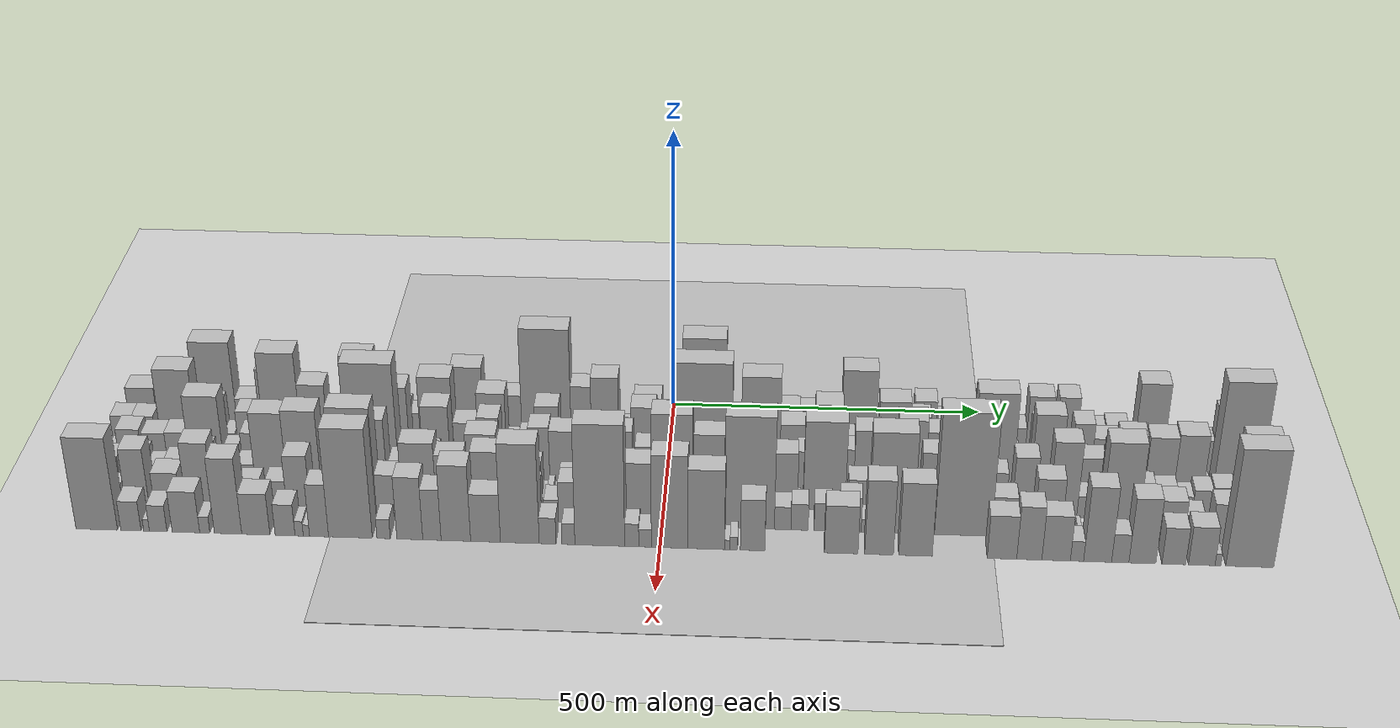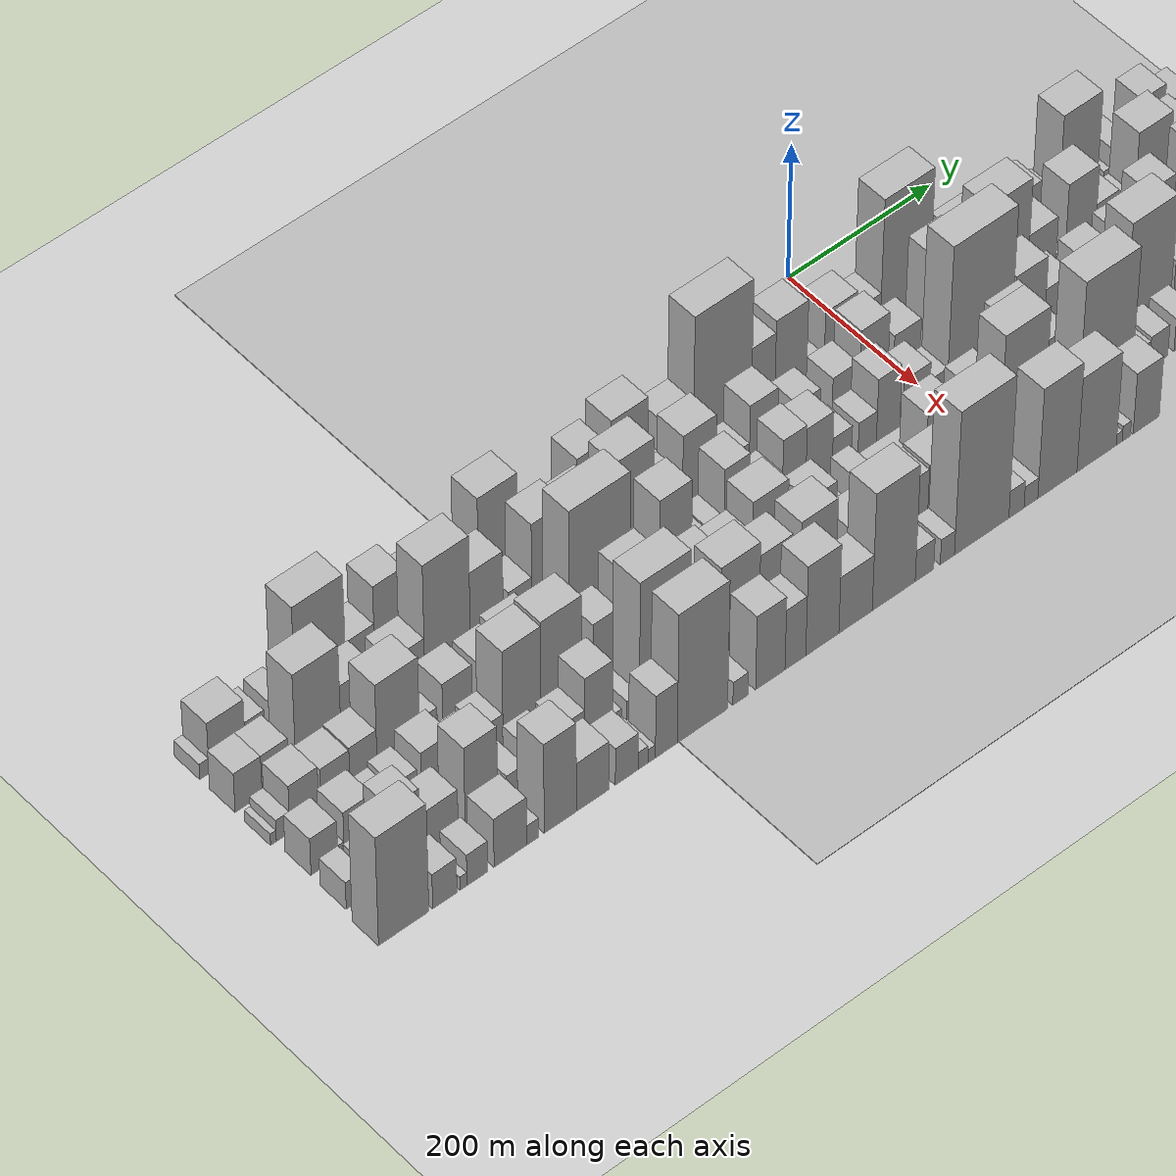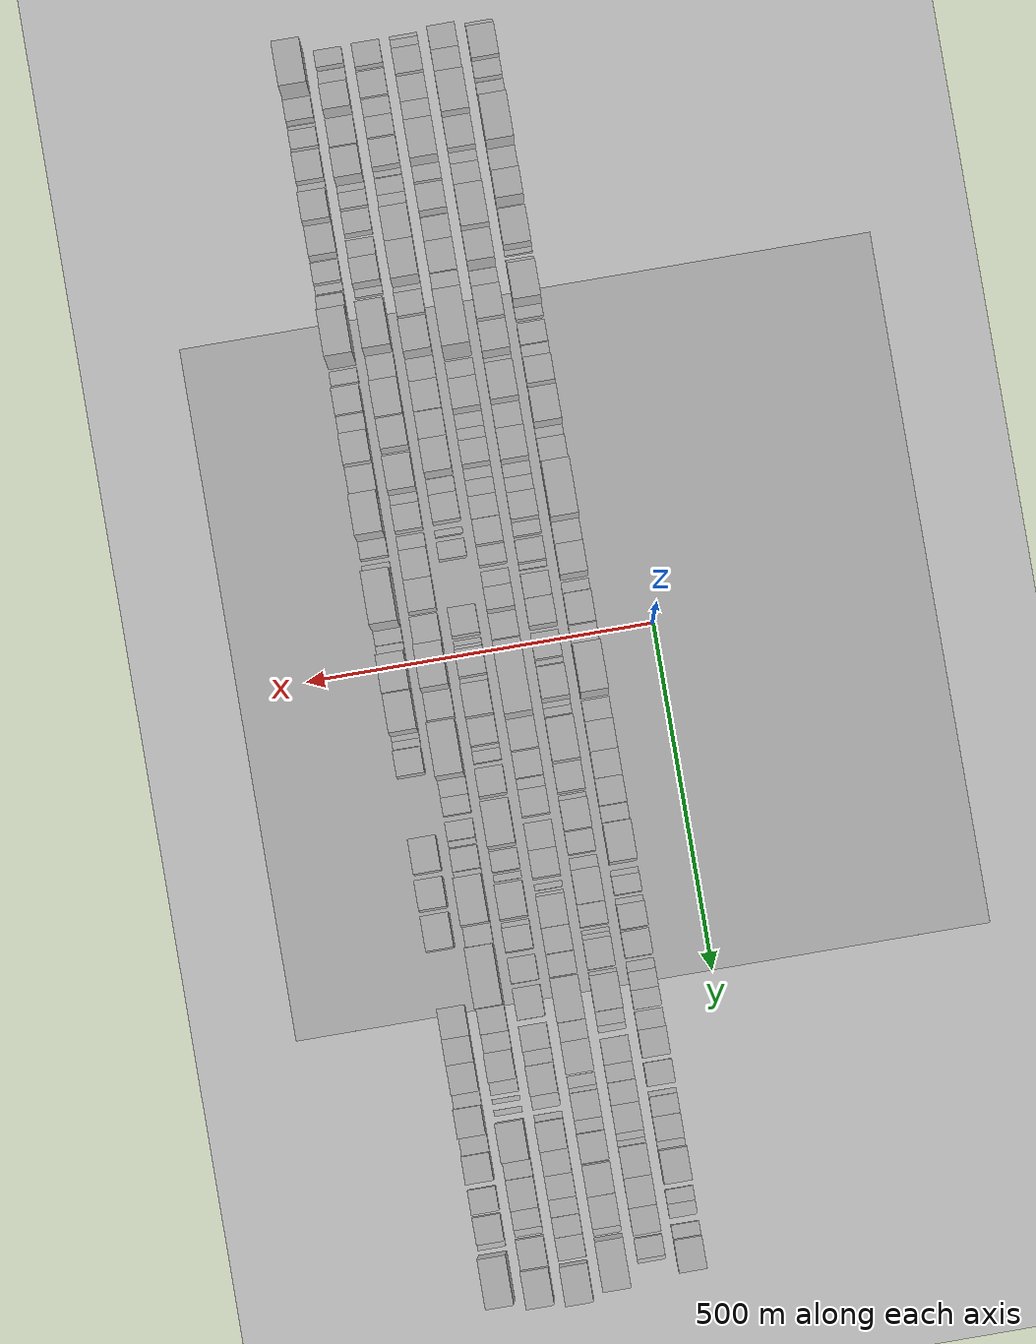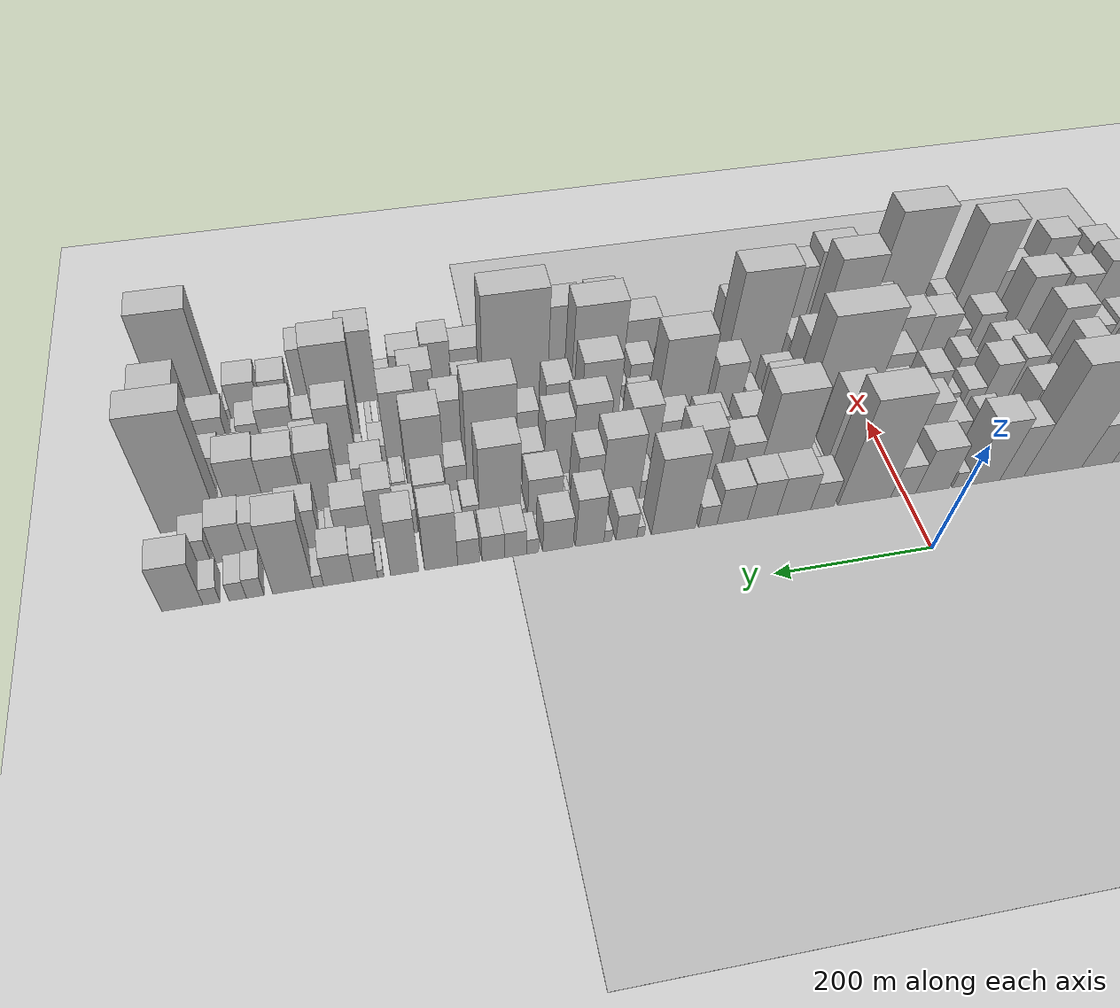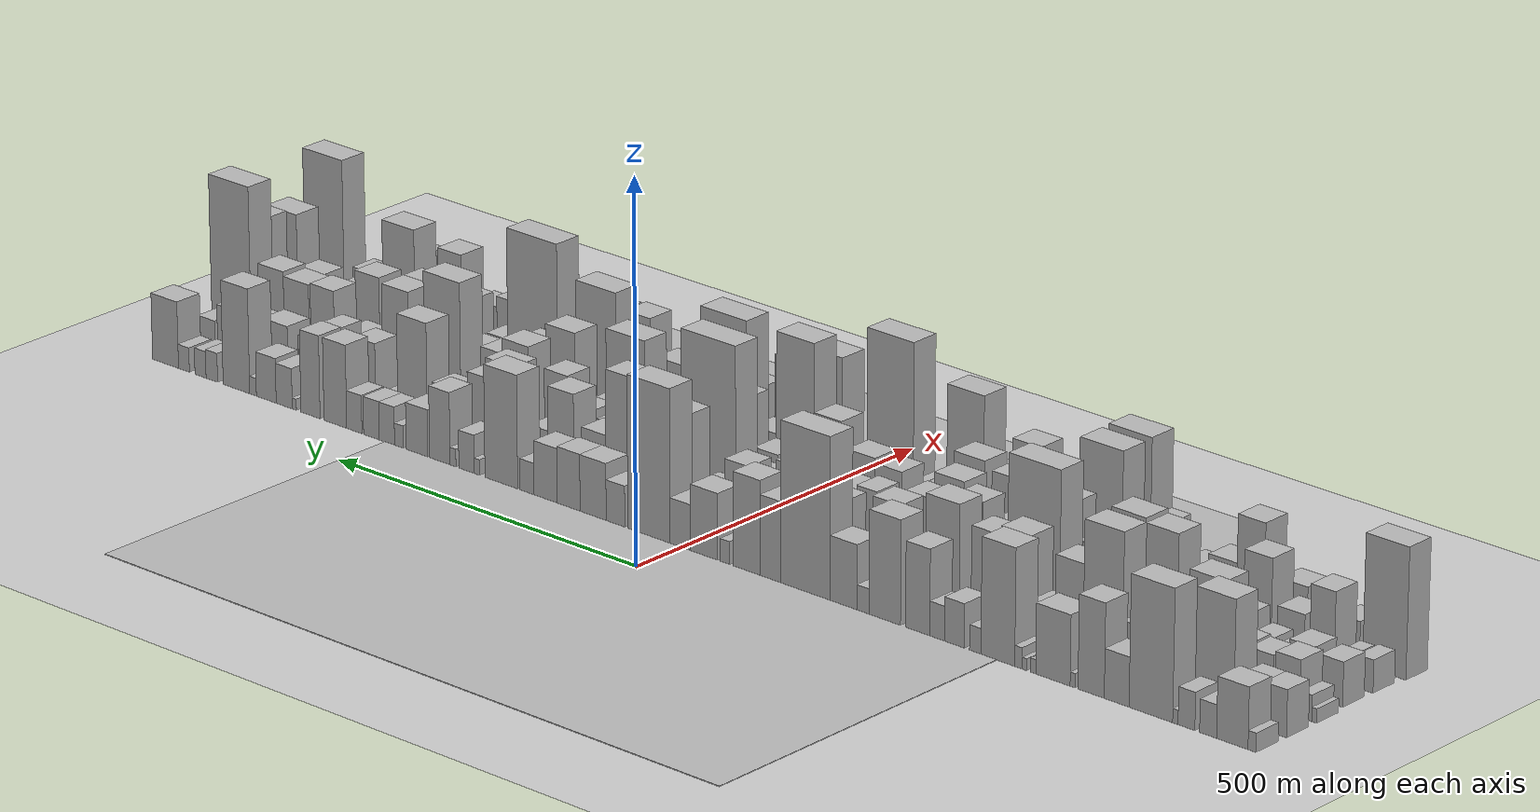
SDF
<?xml version="1.0" encoding="utf-8"?>

<sdf version="1.6">

   <world name="default">

      <gui fullscreen="0">

         <camera name="user_camera">

            <pose>-15 0 4.57585 0 0 0</pose>

            <view_controller>orbit</view_controller>

         </camera>

      </gui>

      <scene>

         <sky>

           <clouds>

             <speed>12</speed>

           </clouds>

         </sky>

         <ambient>0.4 0.4 0.4 1</ambient>

         <background>0.7 0.7 0.7 1</background>

         <shadows>1</shadows>

      </scene>

      <gravity>0 0 -9.8066</gravity>

      <magnetic_field>6e-06 2.3e-05 -4.2e-05</magnetic_field>

      <physics default="0" name="default_physics" type="ode">

         <ode>

            <solver>

               <type>quick</type>

               <iters>10</iters>

               <sor>1.0</sor>

               <use_dynamic_moi_rescaling>0</use_dynamic_moi_rescaling>

            </solver>

            <constraints>

               <cfm>0</cfm>

               <erp>0.2</erp>

               <contact_max_correcting_vel>100</contact_max_correcting_vel>

               <contact_surface_layer>0.001</contact_surface_layer>

            </constraints>

         </ode>

         <max_step_size>0.004</max_step_size>

         <real_time_factor>1</real_time_factor>

         <real_time_update_rate>250</real_time_update_rate>

      </physics>

      <light name="sun" type="directional">

         <cast_shadows>1</cast_shadows>

         <pose>0 0 10 0 0 0</pose>

         <diffuse>0.8 0.8 0.8 1</diffuse>

         <specular>0.2 0.2 0.2 1</specular>

         <attenuation>

            <range>1000</range>

            <constant>0.9</constant>

            <linear>0.01</linear>

            <quadratic>0.001</quadratic>

         </attenuation>

         <direction>-0.5 0.1 -0.9</direction>

      </light>

      <include>

         <name>ground_plane_1</name>

         <uri>model://HANNAS_ground_plane</uri>

         <pose>0 0 0  0 0 0</pose>

      </include>

      <include>

         <name>ground_plane_2</name>

         <uri>model://HANNAS_ground_plane</uri>

         <pose>100 0 0  0 0 0</pose>

      </include>

      <model name="building_1">

         <static>1</static>

         <pose frame="">100.0000 -884.0675 0 0.000000 0.000000 0.000000</pose>

         <link name="link">

            <pose frame="">0 0 12.00 0 0 0</pose>

            <collision name="collision">

               <geometry>

                  <box>

                     <size>40.0000 11.8650 24.0000</size>

                  </box>

               </geometry>

               <max_contacts>10</max_contacts>

               <surface>

                  <contact>

                     <ode/>

                  </contact>

                  <bounce/>

                  <friction>

                     <torsional>

                        <ode/>

                     </torsional>

                     <ode/>

                  </friction>

               </surface>

            </collision>

            <visual name="visual">

               <cast_shadows>0</cast_shadows>

               <geometry>

                  <box>

                     <size>40.0000 11.8650 24.0000</size>

                  </box>

               </geometry>

               <material>

                  <script>

                     <uri>model://HANNAS_wall/materials/scripts</uri>

                     <uri>model://HANNAS_wall/materials/textures</uri>

                     <name>vrc/HANNAS_wall</name>

                  </script>

               </material>

            </visual>

            <self_collide>0</self_collide>

            <enable_wind>0</enable_wind>

            <kinematic>0</kinematic>

         </link>

      </model>

      <model name="building_2">

         <static>1</static>

         <pose frame="">100.0000 -854.9313 0 0.000000 0.000000 0.000000</pose>

         <link name="link">

            <pose frame="">0 0 39.00 0 0 0</pose>

            <collision name="collision">

               <geometry>

                  <box>

                     <size>40.0000 46.4073 78.0000</size>

                  </box>

               </geometry>

               <max_contacts>10</max_contacts>

               <surface>

                  <contact>

                     <ode/>

                  </contact>

                  <bounce/>

                  <friction>

                     <torsional>

                        <ode/>

                     </torsional>

                     <ode/>

                  </friction>

               </surface>

            </collision>

            <visual name="visual">

               <cast_shadows>0</cast_shadows>

               <geometry>

                  <box>

                     <size>40.0000 46.4073 78.0000</size>

                  </box>

               </geometry>

               <material>

                  <script>

                     <uri>model://HANNAS_wall/materials/scripts</uri>

                     <uri>model://HANNAS_wall/materials/textures</uri>

                     <name>vrc/HANNAS_wall</name>

                  </script>

               </material>

            </visual>

            <self_collide>0</self_collide>

            <enable_wind>0</enable_wind>

            <kinematic>0</kinematic>

         </link>

      </model>

      <model name="building_3">

         <static>1</static>

         <pose frame="">100.0000 -819.1503 0 0.000000 0.000000 0.000000</pose>

         <link name="link">

            <pose frame="">0 0 21.00 0 0 0</pose>

            <collision name="collision">

               <geometry>

                  <box>

                     <size>40.0000 25.1547 42.0000</size>

                  </box>

               </geometry>

               <max_contacts>10</max_contacts>

               <surface>

                  <contact>

                     <ode/>

                  </contact>

                  <bounce/>

                  <friction>

                     <torsional>

                        <ode/>

                     </torsional>

                     <ode/>

                  </friction>

               </surface>

            </collision>

            <visual name="visual">

               <cast_shadows>0</cast_shadows>

               <geometry>

                  <box>

                     <size>40.0000 25.1547 42.0000</size>

                  </box>

               </geometry>

               <material>

                  <script>

                     <uri>model://HANNAS_wall/materials/scripts</uri>

                     <uri>model://HANNAS_wall/materials/textures</uri>

                     <name>vrc/HANNAS_wall</name>

                  </script>

               </material>

            </visual>

            <self_collide>0</self_collide>

            <enable_wind>0</enable_wind>

            <kinematic>0</kinematic>

         </link>

      </model>

      <model name="building_4">

         <static>1</static>

         <pose frame="">100.0000 -787.0632 0 0.000000 0.000000 0.000000</pose>

         <link name="link">

            <pose frame="">0 0 24.00 0 0 0</pose>

            <collision name="collision">

               <geometry>

                  <box>

                     <size>40.0000 25.0196 48.0000</size>

                  </box>

               </geometry>

               <max_contacts>10</max_contacts>

               <surface>

                  <contact>

                     <ode/>

                  </contact>

                  <bounce/>

                  <friction>

                     <torsional>

                        <ode/>

                     </torsional>

                     <ode/>

                  </friction>

               </surface>

            </collision>

            <visual name="visual">

               <cast_shadows>0</cast_shadows>

               <geometry>

                  <box>

                     <size>40.0000 25.0196 48.0000</size>

                  </box>

               </geometry>

               <material>

                  <script>

                     <uri>model://HANNAS_wall/materials/scripts</uri>

                     <uri>model://HANNAS_wall/materials/textures</uri>

                     <name>vrc/HANNAS_wall</name>

                  </script>

               </material>

            </visual>

            <self_collide>0</self_collide>

            <enable_wind>0</enable_wind>

            <kinematic>0</kinematic>

         </link>

      </model>

      <model name="building_5">

         <static>1</static>

         <pose frame="">100.0000 -770.5247 0 0.000000 0.000000 0.000000</pose>

         <link name="link">

            <pose frame="">0 0 9.00 0 0 0</pose>

            <collision name="collision">

               <geometry>

                  <box>

                     <size>40.0000 8.0573 18.0000</size>

                  </box>

               </geometry>

               <max_contacts>10</max_contacts>

               <surface>

                  <contact>

                     <ode/>

                  </contact>

                  <bounce/>

                  <friction>

                     <torsional>

                        <ode/>

                     </torsional>

                     <ode/>

                  </friction>

               </surface>

            </collision>

            <visual name="visual">

               <cast_shadows>0</cast_shadows>

               <geometry>

                  <box>

                     <size>40.0000 8.0573 18.0000</size>

                  </box>

               </geometry>

               <material>

                  <script>

                     <uri>model://HANNAS_wall/materials/scripts</uri>

                     <uri>model://HANNAS_wall/materials/textures</uri>

                     <name>vrc/HANNAS_wall</name>

                  </script>

               </material>

            </visual>

            <self_collide>0</self_collide>

            <enable_wind>0</enable_wind>

            <kinematic>0</kinematic>

         </link>

      </model>

      <model name="building_6">

         <static>1</static>

         <pose frame="">100.0000 -733.8526 0 0.000000 0.000000 0.000000</pose>

         <link name="link">

            <pose frame="">0 0 84.00 0 0 0</pose>

            <collision name="collision">

               <geometry>

                  <box>

                     <size>40.0000 65.2870 168.0000</size>

                  </box>

               </geometry>

               <max_contacts>10</max_contacts>

               <surface>

                  <contact>

                     <ode/>

                  </contact>

                  <bounce/>

                  <friction>

                     <torsional>

                        <ode/>

                     </torsional>

                     <ode/>

                  </friction>

               </surface>

            </collision>

            <visual name="visual">

               <cast_shadows>0</cast_shadows>

               <geometry>

                  <box>

                     <size>40.0000 65.2870 168.0000</size>

                  </box>

               </geometry>

               <material>

                  <script>

                     <uri>model://HANNAS_wall/materials/scripts</uri>

                     <uri>model://HANNAS_wall/materials/textures</uri>

                     <name>vrc/HANNAS_wall</name>

                  </script>

               </material>

            </visual>

            <self_collide>0</self_collide>

            <enable_wind>0</enable_wind>

            <kinematic>0</kinematic>

         </link>

      </model>

      <model name="building_7">

         <static>1</static>

         <pose frame="">100.0000 -682.5342 0 0.000000 0.000000 0.000000</pose>

         <link name="link">

            <pose frame="">0 0 31.50 0 0 0</pose>

            <collision name="collision">

               <geometry>

                  <box>

                     <size>40.0000 37.3498 63.0000</size>

                  </box>

               </geometry>

               <max_contacts>10</max_contacts>

               <surface>

                  <contact>

                     <ode/>

                  </contact>

                  <bounce/>

                  <friction>

                     <torsional>

                        <ode/>

                     </torsional>

                     <ode/>

                  </friction>

               </surface>

            </collision>

            <visual name="visual">

               <cast_shadows>0</cast_shadows>

               <geometry>

                  <box>

                     <size>40.0000 37.3498 63.0000</size>

                  </box>

               </geometry>

               <material>

                  <script>

                     <uri>model://HANNAS_wall/materials/scripts</uri>

                     <uri>model://HANNAS_wall/materials/textures</uri>

                     <name>vrc/HANNAS_wall</name>

                  </script>

               </material>

            </visual>

            <self_collide>0</self_collide>

            <enable_wind>0</enable_wind>

            <kinematic>0</kinematic>

         </link>

      </model>

      <model name="building_8">

         <static>1</static>

         <pose frame="">100.0000 -643.9505 0 0.000000 0.000000 0.000000</pose>

         <link name="link">

            <pose frame="">0 0 60.00 0 0 0</pose>

            <collision name="collision">

               <geometry>

                  <box>

                     <size>40.0000 39.8175 120.0000</size>

                  </box>

               </geometry>

               <max_contacts>10</max_contacts>

               <surface>

                  <contact>

                     <ode/>

                  </contact>

                  <bounce/>

                  <friction>

                     <torsional>

                        <ode/>

                     </torsional>

                     <ode/>

                  </friction>

               </surface>

            </collision>

            <visual name="visual">

               <cast_shadows>0</cast_shadows>

               <geometry>

                  <box>

                     <size>40.0000 39.8175 120.0000</size>

                  </box>

               </geometry>

               <material>

                  <script>

                     <uri>model://HANNAS_wall/materials/scripts</uri>

                     <uri>model://HANNAS_wall/materials/textures</uri>

                     <name>vrc/HANNAS_wall</name>

                  </script>

               </material>

            </visual>

            <self_collide>0</self_collide>

            <enable_wind>0</enable_wind>

            <kinematic>0</kinematic>

         </link>

      </model>

      <model name="building_9">

         <static>1</static>

         <pose frame="">100.0000 -616.0592 0 0.000000 0.000000 0.000000</pose>

         <link name="link">

            <pose frame="">0 0 9.00 0 0 0</pose>

            <collision name="collision">

               <geometry>

                  <box>

                     <size>40.0000 7.9652 18.0000</size>

                  </box>

               </geometry>

               <max_contacts>10</max_contacts>

               <surface>

                  <contact>

                     <ode/>

                  </contact>

                  <bounce/>

                  <friction>

                     <torsional>

                        <ode/>

                     </torsional>

                     <ode/>

                  </friction>

               </surface>

            </collision>

            <visual name="visual">

               <cast_shadows>0</cast_shadows>

               <geometry>

                  <box>

                     <size>40.0000 7.9652 18.0000</size>

                  </box>

               </geometry>

               <material>

                  <script>

                     <uri>model://HANNAS_wall/materials/scripts</uri>

                     <uri>model://HANNAS_wall/materials/textures</uri>

                     <name>vrc/HANNAS_wall</name>

                  </script>

               </material>

            </visual>

            <self_collide>0</self_collide>

            <enable_wind>0</enable_wind>

            <kinematic>0</kinematic>

         </link>

      </model>

      <model name="building_10">

         <static>1</static>

         <pose frame="">100.0000 -585.8317 0 0.000000 0.000000 0.000000</pose>

         <link name="link">

            <pose frame="">0 0 45.00 0 0 0</pose>

            <collision name="collision">

               <geometry>

                  <box>

                     <size>40.0000 52.4896 90.0000</size>

                  </box>

               </geometry>

               <max_contacts>10</max_contacts>

               <surface>

                  <contact>

                     <ode/>

                  </contact>

                  <bounce/>

                  <friction>

                     <torsional>

                        <ode/>

                     </torsional>

                     <ode/>

                  </friction>

               </surface>

            </collision>

            <visual name="visual">

               <cast_shadows>0</cast_shadows>

               <geometry>

                  <box>

                     <size>40.0000 52.4896 90.0000</size>

                  </box>

               </geometry>

               <material>

                  <script>

                     <uri>model://HANNAS_wall/materials/scripts</uri>

                     <uri>model://HANNAS_wall/materials/textures</uri>

                     <name>vrc/HANNAS_wall</name>

                  </script>

               </material>

            </visual>

            <self_collide>0</self_collide>

            <enable_wind>0</enable_wind>

            <kinematic>0</kinematic>

         </link>

      </model>

      <model name="building_11">

         <static>1</static>

         <pose frame="">100.0000 -555.8042 0 0.000000 0.000000 0.000000</pose>

         <link name="link">

            <pose frame="">0 0 9.00 0 0 0</pose>

            <collision name="collision">

               <geometry>

                  <box>

                     <size>40.0000 7.5655 18.0000</size>

                  </box>

               </geometry>

               <max_contacts>10</max_contacts>

               <surface>

                  <contact>

                     <ode/>

                  </contact>

                  <bounce/>

                  <friction>

                     <torsional>

                        <ode/>

                     </torsional>

                     <ode/>

                  </friction>

               </surface>

            </collision>

            <visual name="visual">

               <cast_shadows>0</cast_shadows>

               <geometry>

                  <box>

                     <size>40.0000 7.5655 18.0000</size>

                  </box>

               </geometry>

               <material>

                  <script>

                     <uri>model://HANNAS_wall/materials/scripts</uri>

                     <uri>model://HANNAS_wall/materials/textures</uri>

                     <name>vrc/HANNAS_wall</name>

                  </script>

               </material>

            </visual>

            <self_collide>0</self_collide>

            <enable_wind>0</enable_wind>

            <kinematic>0</kinematic>

         </link>

      </model>

      <model name="building_12">

         <static>1</static>

         <pose frame="">100.0000 -542.4113 0 0.000000 0.000000 0.000000</pose>

         <link name="link">

            <pose frame="">0 0 7.50 0 0 0</pose>

            <collision name="collision">

               <geometry>

                  <box>

                     <size>40.0000 7.2202 15.0000</size>

                  </box>

               </geometry>

               <max_contacts>10</max_contacts>

               <surface>

                  <contact>

                     <ode/>

                  </contact>

                  <bounce/>

                  <friction>

                     <torsional>

                        <ode/>

                     </torsional>

                     <ode/>

                  </friction>

               </surface>

            </collision>

            <visual name="visual">

               <cast_shadows>0</cast_shadows>

               <geometry>

                  <box>

                     <size>40.0000 7.2202 15.0000</size>

                  </box>

               </geometry>

               <material>

                  <script>

                     <uri>model://HANNAS_wall/materials/scripts</uri>

                     <uri>model://HANNAS_wall/materials/textures</uri>

                     <name>vrc/HANNAS_wall</name>

                  </script>

               </material>

            </visual>

            <self_collide>0</self_collide>

            <enable_wind>0</enable_wind>

            <kinematic>0</kinematic>

         </link>

      </model>

      <model name="building_13">

         <static>1</static>

         <pose frame="">100.0000 -533.1049 0 0.000000 0.000000 0.000000</pose>

         <link name="link">

            <pose frame="">0 0 13.50 0 0 0</pose>

            <collision name="collision">

               <geometry>

                  <box>

                     <size>40.0000 11.3927 27.0000</size>

                  </box>

               </geometry>

               <max_contacts>10</max_contacts>

               <surface>

                  <contact>

                     <ode/>

                  </contact>

                  <bounce/>

                  <friction>

                     <torsional>

                        <ode/>

                     </torsional>

                     <ode/>

                  </friction>

               </surface>

            </collision>

            <visual name="visual">

               <cast_shadows>0</cast_shadows>

               <geometry>

                  <box>

                     <size>40.0000 11.3927 27.0000</size>

                  </box>

               </geometry>

               <material>

                  <script>

                     <uri>model://HANNAS_wall/materials/scripts</uri>

                     <uri>model://HANNAS_wall/materials/textures</uri>

                     <name>vrc/HANNAS_wall</name>

                  </script>

               </material>

            </visual>

            <self_collide>0</self_collide>

            <enable_wind>0</enable_wind>

            <kinematic>0</kinematic>

         </link>

      </model>

      <model name="building_14">

         <static>1</static>

         <pose frame="">100.0000 -501.3403 0 0.000000 0.000000 0.000000</pose>

         <link name="link">

            <pose frame="">0 0 75.00 0 0 0</pose>

            <collision name="collision">

               <geometry>

                  <box>

                     <size>40.0000 52.1366 150.0000</size>

                  </box>

               </geometry>

               <max_contacts>10</max_contacts>

               <surface>

                  <contact>

                     <ode/>

                  </contact>

                  <bounce/>

                  <friction>

                     <torsional>

                        <ode/>

                     </torsional>

                     <ode/>

                  </friction>

               </surface>

            </collision>

            <visual name="visual">

               <cast_shadows>0</cast_shadows>

               <geometry>

                  <box>

                     <size>40.0000 52.1366 150.0000</size>

                  </box>

               </geometry>

               <material>

                  <script>

                     <uri>model://HANNAS_wall/materials/scripts</uri>

                     <uri>model://HANNAS_wall/materials/textures</uri>

                     <name>vrc/HANNAS_wall</name>

                  </script>

               </material>

            </visual>

            <self_collide>0</self_collide>

            <enable_wind>0</enable_wind>

            <kinematic>0</kinematic>

         </link>

      </model>

      <model name="building_15">

         <static>1</static>

         <pose frame="">100.0000 -466.4568 0 0.000000 0.000000 0.000000</pose>

         <link name="link">

            <pose frame="">0 0 16.50 0 0 0</pose>

            <collision name="collision">

               <geometry>

                  <box>

                     <size>40.0000 17.6303 33.0000</size>

                  </box>

               </geometry>

               <max_contacts>10</max_contacts>

               <surface>

                  <contact>

                     <ode/>

                  </contact>

                  <bounce/>

                  <friction>

                     <torsional>

                        <ode/>

                     </torsional>

                     <ode/>

                  </friction>

               </surface>

            </collision>

            <visual name="visual">

               <cast_shadows>0</cast_shadows>

               <geometry>

                  <box>

                     <size>40.0000 17.6303 33.0000</size>

                  </box>

               </geometry>

               <material>

                  <script>

                     <uri>model://HANNAS_wall/materials/scripts</uri>

                     <uri>model://HANNAS_wall/materials/textures</uri>

                     <name>vrc/HANNAS_wall</name>

                  </script>

               </material>

            </visual>

            <self_collide>0</self_collide>

            <enable_wind>0</enable_wind>

            <kinematic>0</kinematic>

         </link>

      </model>

      <model name="building_16">

         <static>1</static>

         <pose frame="">100.0000 -434.1845 0 0.000000 0.000000 0.000000</pose>

         <link name="link">

            <pose frame="">0 0 28.50 0 0 0</pose>

            <collision name="collision">

               <geometry>

                  <box>

                     <size>40.0000 30.9145 57.0000</size>

                  </box>

               </geometry>

               <max_contacts>10</max_contacts>

               <surface>

                  <contact>

                     <ode/>

                  </contact>

                  <bounce/>

                  <friction>

                     <torsional>

                        <ode/>

                     </torsional>

                     <ode/>

                  </friction>

               </surface>

            </collision>

            <visual name="visual">

               <cast_shadows>0</cast_shadows>

               <geometry>

                  <box>

                     <size>40.0000 30.9145 57.0000</size>

                  </box>

               </geometry>

               <material>

                  <script>

                     <uri>model://HANNAS_wall/materials/scripts</uri>

                     <uri>model://HANNAS_wall/materials/textures</uri>

                     <name>vrc/HANNAS_wall</name>

                  </script>

               </material>

            </visual>

            <self_collide>0</self_collide>

            <enable_wind>0</enable_wind>

            <kinematic>0</kinematic>

         </link>

      </model>

      <model name="building_17">

         <static>1</static>

         <pose frame="">100.0000 -407.2969 0 0.000000 0.000000 0.000000</pose>

         <link name="link">

            <pose frame="">0 0 22.50 0 0 0</pose>

            <collision name="collision">

               <geometry>

                  <box>

                     <size>40.0000 22.8605 45.0000</size>

                  </box>

               </geometry>

               <max_contacts>10</max_contacts>

               <surface>

                  <contact>

                     <ode/>

                  </contact>

                  <bounce/>

                  <friction>

                     <torsional>

                        <ode/>

                     </torsional>

                     <ode/>

                  </friction>

               </surface>

            </collision>

            <visual name="visual">

               <cast_shadows>0</cast_shadows>

               <geometry>

                  <box>

                     <size>40.0000 22.8605 45.0000</size>

                  </box>

               </geometry>

               <material>

                  <script>

                     <uri>model://HANNAS_wall/materials/scripts</uri>

                     <uri>model://HANNAS_wall/materials/textures</uri>

                     <name>vrc/HANNAS_wall</name>

                  </script>

               </material>

            </visual>

            <self_collide>0</self_collide>

            <enable_wind>0</enable_wind>

            <kinematic>0</kinematic>

         </link>

      </model>

      <model name="building_18">

         <static>1</static>

         <pose frame="">100.0000 -376.9645 0 0.000000 0.000000 0.000000</pose>

         <link name="link">

            <pose frame="">0 0 55.50 0 0 0</pose>

            <collision name="collision">

               <geometry>

                  <box>

                     <size>40.0000 37.8044 111.0000</size>

                  </box>

               </geometry>

               <max_contacts>10</max_contacts>

               <surface>

                  <contact>

                     <ode/>

                  </contact>

                  <bounce/>

                  <friction>

                     <torsional>

                        <ode/>

                     </torsional>

                     <ode/>

                  </friction>

               </surface>

            </collision>

            <visual name="visual">

               <cast_shadows>0</cast_shadows>

               <geometry>

                  <box>

                     <size>40.0000 37.8044 111.0000</size>

                  </box>

               </geometry>

               <material>

                  <script>

                     <uri>model://HANNAS_wall/materials/scripts</uri>

                     <uri>model://HANNAS_wall/materials/textures</uri>

                     <name>vrc/HANNAS_wall</name>

                  </script>

               </material>

            </visual>

            <self_collide>0</self_collide>

            <enable_wind>0</enable_wind>

            <kinematic>0</kinematic>

         </link>

      </model>

      <model name="building_19">

         <static>1</static>

         <pose frame="">100.0000 -325.2309 0 0.000000 0.000000 0.000000</pose>

         <link name="link">

            <pose frame="">0 0 67.50 0 0 0</pose>

            <collision name="collision">

               <geometry>

                  <box>

                     <size>40.0000 49.6627 135.0000</size>

                  </box>

               </geometry>

               <max_contacts>10</max_contacts>

               <surface>

                  <contact>

                     <ode/>

                  </contact>

                  <bounce/>

                  <friction>

                     <torsional>

                        <ode/>

                     </torsional>

                     <ode/>

                  </friction>

               </surface>

            </collision>

            <visual name="visual">

               <cast_shadows>0</cast_shadows>

               <geometry>

                  <box>

                     <size>40.0000 49.6627 135.0000</size>

                  </box>

               </geometry>

               <material>

                  <script>

                     <uri>model://HANNAS_wall/materials/scripts</uri>

                     <uri>model://HANNAS_wall/materials/textures</uri>

                     <name>vrc/HANNAS_wall</name>

                  </script>

               </material>

            </visual>

            <self_collide>0</self_collide>

            <enable_wind>0</enable_wind>

            <kinematic>0</kinematic>

         </link>

      </model>

      <model name="building_20">

         <static>1</static>

         <pose frame="">100.0000 -290.9320 0 0.000000 0.000000 0.000000</pose>

         <link name="link">

            <pose frame="">0 0 16.50 0 0 0</pose>

            <collision name="collision">

               <geometry>

                  <box>

                     <size>40.0000 18.9351 33.0000</size>

                  </box>

               </geometry>

               <max_contacts>10</max_contacts>

               <surface>

                  <contact>

                     <ode/>

                  </contact>

                  <bounce/>

                  <friction>

                     <torsional>

                        <ode/>

                     </torsional>

                     <ode/>

                  </friction>

               </surface>

            </collision>

            <visual name="visual">

               <cast_shadows>0</cast_shadows>

               <geometry>

                  <box>

                     <size>40.0000 18.9351 33.0000</size>

                  </box>

               </geometry>

               <material>

                  <script>

                     <uri>model://HANNAS_wall/materials/scripts</uri>

                     <uri>model://HANNAS_wall/materials/textures</uri>

                     <name>vrc/HANNAS_wall</name>

                  </script>

               </material>

            </visual>

            <self_collide>0</self_collide>

            <enable_wind>0</enable_wind>

            <kinematic>0</kinematic>

         </link>

      </model>

      <model name="building_21">

         <static>1</static>

         <pose frame="">100.0000 -260.0530 0 0.000000 0.000000 0.000000</pose>

         <link name="link">

            <pose frame="">0 0 42.00 0 0 0</pose>

            <collision name="collision">

               <geometry>

                  <box>

                     <size>40.0000 42.8229 84.0000</size>

                  </box>

               </geometry>

               <max_contacts>10</max_contacts>

               <surface>

                  <contact>

                     <ode/>

                  </contact>

                  <bounce/>

                  <friction>

                     <torsional>

                        <ode/>

                     </torsional>

                     <ode/>

                  </friction>

               </surface>

            </collision>

            <visual name="visual">

               <cast_shadows>0</cast_shadows>

               <geometry>

                  <box>

                     <size>40.0000 42.8229 84.0000</size>

                  </box>

               </geometry>

               <material>

                  <script>

                     <uri>model://HANNAS_wall/materials/scripts</uri>

                     <uri>model://HANNAS_wall/materials/textures</uri>

                     <name>vrc/HANNAS_wall</name>

                  </script>

               </material>

            </visual>

            <self_collide>0</self_collide>

            <enable_wind>0</enable_wind>

            <kinematic>0</kinematic>

         </link>

      </model>

      <model name="building_22">

         <static>1</static>

         <pose frame="">100.0000 -198.9923 0 0.000000 0.000000 0.000000</pose>

         <link name="link">

            <pose frame="">0 0 105.00 0 0 0</pose>

            <collision name="collision">

               <geometry>

                  <box>

                     <size>40.0000 79.2986 210.0000</size>

                  </box>

               </geometry>

               <max_contacts>10</max_contacts>

               <surface>

                  <contact>

                     <ode/>

                  </contact>

                  <bounce/>

                  <friction>

                     <torsional>

                        <ode/>

                     </torsional>

                     <ode/>

                  </friction>

               </surface>

            </collision>

            <visual name="visual">

               <cast_shadows>0</cast_shadows>

               <geometry>

                  <box>

                     <size>40.0000 79.2986 210.0000</size>

                  </box>

               </geometry>

               <material>

                  <script>

                     <uri>model://HANNAS_wall/materials/scripts</uri>

                     <uri>model://HANNAS_wall/materials/textures</uri>

                     <name>vrc/HANNAS_wall</name>

                  </script>

               </material>

            </visual>

            <self_collide>0</self_collide>

            <enable_wind>0</enable_wind>

            <kinematic>0</kinematic>

         </link>

      </model>

      <model name="building_23">

         <static>1</static>

         <pose frame="">100.0000 -143.0778 0 0.000000 0.000000 0.000000</pose>

         <link name="link">

            <pose frame="">0 0 52.50 0 0 0</pose>

            <collision name="collision">

               <geometry>

                  <box>

                     <size>40.0000 32.5304 105.0000</size>

                  </box>

               </geometry>

               <max_contacts>10</max_contacts>

               <surface>

                  <contact>

                     <ode/>

                  </contact>

                  <bounce/>

                  <friction>

                     <torsional>

                        <ode/>

                     </torsional>

                     <ode/>

                  </friction>

               </surface>

            </collision>

            <visual name="visual">

               <cast_shadows>0</cast_shadows>

               <geometry>

                  <box>

                     <size>40.0000 32.5304 105.0000</size>

                  </box>

               </geometry>

               <material>

                  <script>

                     <uri>model://HANNAS_wall/materials/scripts</uri>

                     <uri>model://HANNAS_wall/materials/textures</uri>

                     <name>vrc/HANNAS_wall</name>

                  </script>

               </material>

            </visual>

            <self_collide>0</self_collide>

            <enable_wind>0</enable_wind>

            <kinematic>0</kinematic>

         </link>

      </model>

      <model name="building_24">

         <static>1</static>

         <pose frame="">100.0000 -104.7868 0 0.000000 0.000000 0.000000</pose>

         <link name="link">

            <pose frame="">0 0 61.50 0 0 0</pose>

            <collision name="collision">

               <geometry>

                  <box>

                     <size>40.0000 44.0515 123.0000</size>

                  </box>

               </geometry>

               <max_contacts>10</max_contacts>

               <surface>

                  <contact>

                     <ode/>

                  </contact>

                  <bounce/>

                  <friction>

                     <torsional>

                        <ode/>

                     </torsional>

                     <ode/>

                  </friction>

               </surface>

            </collision>

            <visual name="visual">

               <cast_shadows>0</cast_shadows>

               <geometry>

                  <box>

                     <size>40.0000 44.0515 123.0000</size>

                  </box>

               </geometry>

               <material>

                  <script>

                     <uri>model://HANNAS_wall/materials/scripts</uri>

                     <uri>model://HANNAS_wall/materials/textures</uri>

                     <name>vrc/HANNAS_wall</name>

                  </script>

               </material>

            </visual>

            <self_collide>0</self_collide>

            <enable_wind>0</enable_wind>

            <kinematic>0</kinematic>

         </link>

      </model>

      <model name="building_25">

         <static>1</static>

         <pose frame="">100.0000 -70.0576 0 0.000000 0.000000 0.000000</pose>

         <link name="link">

            <pose frame="">0 0 15.00 0 0 0</pose>

            <collision name="collision">

               <geometry>

                  <box>

                     <size>40.0000 15.4070 30.0000</size>

                  </box>

               </geometry>

               <max_contacts>10</max_contacts>

               <surface>

                  <contact>

                     <ode/>

                  </contact>

                  <bounce/>

                  <friction>

                     <torsional>

                        <ode/>

                     </torsional>

                     <ode/>

                  </friction>

               </surface>

            </collision>

            <visual name="visual">

               <cast_shadows>0</cast_shadows>

               <geometry>

                  <box>

                     <size>40.0000 15.4070 30.0000</size>

                  </box>

               </geometry>

               <material>

                  <script>

                     <uri>model://HANNAS_wall/materials/scripts</uri>

                     <uri>model://HANNAS_wall/materials/textures</uri>

                     <name>vrc/HANNAS_wall</name>

                  </script>

               </material>

            </visual>

            <self_collide>0</self_collide>

            <enable_wind>0</enable_wind>

            <kinematic>0</kinematic>

         </link>

      </model>

      <model name="building_26">

         <static>1</static>

         <pose frame="">100.0000 -35.9527 0 0.000000 0.000000 0.000000</pose>

         <link name="link">

            <pose frame="">0 0 43.50 0 0 0</pose>

            <collision name="collision">

               <geometry>

                  <box>

                     <size>40.0000 44.8028 87.0000</size>

                  </box>

               </geometry>

               <max_contacts>10</max_contacts>

               <surface>

                  <contact>

                     <ode/>

                  </contact>

                  <bounce/>

                  <friction>

                     <torsional>

                        <ode/>

                     </torsional>

                     <ode/>

                  </friction>

               </surface>

            </collision>

            <visual name="visual">

               <cast_shadows>0</cast_shadows>

               <geometry>

                  <box>

                     <size>40.0000 44.8028 87.0000</size>

                  </box>

               </geometry>

               <material>

                  <script>

                     <uri>model://HANNAS_wall/materials/scripts</uri>

                     <uri>model://HANNAS_wall/materials/textures</uri>

                     <name>vrc/HANNAS_wall</name>

                  </script>

               </material>

            </visual>

            <self_collide>0</self_collide>

            <enable_wind>0</enable_wind>

            <kinematic>0</kinematic>

         </link>

      </model>

      <model name="building_27">

         <static>1</static>

         <pose frame="">100.0000 3.0839 0 0.000000 0.000000 0.000000</pose>

         <link name="link">

            <pose frame="">0 0 30.00 0 0 0</pose>

            <collision name="collision">

               <geometry>

                  <box>

                     <size>40.0000 33.2703 60.0000</size>

                  </box>

               </geometry>

               <max_contacts>10</max_contacts>

               <surface>

                  <contact>

                     <ode/>

                  </contact>

                  <bounce/>

                  <friction>

                     <torsional>

                        <ode/>

                     </torsional>

                     <ode/>

                  </friction>

               </surface>

            </collision>

            <visual name="visual">

               <cast_shadows>0</cast_shadows>

               <geometry>

                  <box>

                     <size>40.0000 33.2703 60.0000</size>

                  </box>

               </geometry>

               <material>

                  <script>

                     <uri>model://HANNAS_wall/materials/scripts</uri>

                     <uri>model://HANNAS_wall/materials/textures</uri>

                     <name>vrc/HANNAS_wall</name>

                  </script>

               </material>

            </visual>

            <self_collide>0</self_collide>

            <enable_wind>0</enable_wind>

            <kinematic>0</kinematic>

         </link>

      </model>

      <model name="building_28">

         <static>1</static>

         <pose frame="">100.0000 54.4225 0 0.000000 0.000000 0.000000</pose>

         <link name="link">

            <pose frame="">0 0 100.50 0 0 0</pose>

            <collision name="collision">

               <geometry>

                  <box>

                     <size>40.0000 69.4068 201.0000</size>

                  </box>

               </geometry>

               <max_contacts>10</max_contacts>

               <surface>

                  <contact>

                     <ode/>

                  </contact>

                  <bounce/>

                  <friction>

                     <torsional>

                        <ode/>

                     </torsional>

                     <ode/>

                  </friction>

               </surface>

            </collision>

            <visual name="visual">

               <cast_shadows>0</cast_shadows>

               <geometry>

                  <box>

                     <size>40.0000 69.4068 201.0000</size>

                  </box>

               </geometry>

               <material>

                  <script>

                     <uri>model://HANNAS_wall/materials/scripts</uri>

                     <uri>model://HANNAS_wall/materials/textures</uri>

                     <name>vrc/HANNAS_wall</name>

                  </script>

               </material>

            </visual>

            <self_collide>0</self_collide>

            <enable_wind>0</enable_wind>

            <kinematic>0</kinematic>

         </link>

      </model>

      <model name="building_29">

         <static>1</static>

         <pose frame="">100.0000 109.5597 0 0.000000 0.000000 0.000000</pose>

         <link name="link">

            <pose frame="">0 0 27.00 0 0 0</pose>

            <collision name="collision">

               <geometry>

                  <box>

                     <size>40.0000 30.8677 54.0000</size>

                  </box>

               </geometry>

               <max_contacts>10</max_contacts>

               <surface>

                  <contact>

                     <ode/>

                  </contact>

                  <bounce/>

                  <friction>

                     <torsional>

                        <ode/>

                     </torsional>

                     <ode/>

                  </friction>

               </surface>

            </collision>

            <visual name="visual">

               <cast_shadows>0</cast_shadows>

               <geometry>

                  <box>

                     <size>40.0000 30.8677 54.0000</size>

                  </box>

               </geometry>

               <material>

                  <script>

                     <uri>model://HANNAS_wall/materials/scripts</uri>

                     <uri>model://HANNAS_wall/materials/textures</uri>

                     <name>vrc/HANNAS_wall</name>

                  </script>

               </material>

            </visual>

            <self_collide>0</self_collide>

            <enable_wind>0</enable_wind>

            <kinematic>0</kinematic>

         </link>

      </model>

      <model name="building_30">

         <static>1</static>

         <pose frame="">100.0000 146.6859 0 0.000000 0.000000 0.000000</pose>

         <link name="link">

            <pose frame="">0 0 37.50 0 0 0</pose>

            <collision name="collision">

               <geometry>

                  <box>

                     <size>40.0000 43.3847 75.0000</size>

                  </box>

               </geometry>

               <max_contacts>10</max_contacts>

               <surface>

                  <contact>

                     <ode/>

                  </contact>

                  <bounce/>

                  <friction>

                     <torsional>

                        <ode/>

                     </torsional>

                     <ode/>

                  </friction>

               </surface>

            </collision>

            <visual name="visual">

               <cast_shadows>0</cast_shadows>

               <geometry>

                  <box>

                     <size>40.0000 43.3847 75.0000</size>

                  </box>

               </geometry>

               <material>

                  <script>

                     <uri>model://HANNAS_wall/materials/scripts</uri>

                     <uri>model://HANNAS_wall/materials/textures</uri>

                     <name>vrc/HANNAS_wall</name>

                  </script>

               </material>

            </visual>

            <self_collide>0</self_collide>

            <enable_wind>0</enable_wind>

            <kinematic>0</kinematic>

         </link>

      </model>

      <model name="building_31">

         <static>1</static>

         <pose frame="">100.0000 187.5784 0 0.000000 0.000000 0.000000</pose>

         <link name="link">

            <pose frame="">0 0 37.50 0 0 0</pose>

            <collision name="collision">

               <geometry>

                  <box>

                     <size>40.0000 38.4004 75.0000</size>

                  </box>

               </geometry>

               <max_contacts>10</max_contacts>

               <surface>

                  <contact>

                     <ode/>

                  </contact>

                  <bounce/>

                  <friction>

                     <torsional>

                        <ode/>

                     </torsional>

                     <ode/>

                  </friction>

               </surface>

            </collision>

            <visual name="visual">

               <cast_shadows>0</cast_shadows>

               <geometry>

                  <box>

                     <size>40.0000 38.4004 75.0000</size>

                  </box>

               </geometry>

               <material>

                  <script>

                     <uri>model://HANNAS_wall/materials/scripts</uri>

                     <uri>model://HANNAS_wall/materials/textures</uri>

                     <name>vrc/HANNAS_wall</name>

                  </script>

               </material>

            </visual>

            <self_collide>0</self_collide>

            <enable_wind>0</enable_wind>

            <kinematic>0</kinematic>

         </link>

      </model>

      <model name="building_32">

         <static>1</static>

         <pose frame="">100.0000 226.2033 0 0.000000 0.000000 0.000000</pose>

         <link name="link">

            <pose frame="">0 0 36.00 0 0 0</pose>

            <collision name="collision">

               <geometry>

                  <box>

                     <size>40.0000 38.8495 72.0000</size>

                  </box>

               </geometry>

               <max_contacts>10</max_contacts>

               <surface>

                  <contact>

                     <ode/>

                  </contact>

                  <bounce/>

                  <friction>

                     <torsional>

                        <ode/>

                     </torsional>

                     <ode/>

                  </friction>

               </surface>

            </collision>

            <visual name="visual">

               <cast_shadows>0</cast_shadows>

               <geometry>

                  <box>

                     <size>40.0000 38.8495 72.0000</size>

                  </box>

               </geometry>

               <material>

                  <script>

                     <uri>model://HANNAS_wall/materials/scripts</uri>

                     <uri>model://HANNAS_wall/materials/textures</uri>

                     <name>vrc/HANNAS_wall</name>

                  </script>

               </material>

            </visual>

            <self_collide>0</self_collide>

            <enable_wind>0</enable_wind>

            <kinematic>0</kinematic>

         </link>

      </model>

      <model name="building_33">

         <static>1</static>

         <pose frame="">100.0000 257.3364 0 0.000000 0.000000 0.000000</pose>

         <link name="link">

            <pose frame="">0 0 21.00 0 0 0</pose>

            <collision name="collision">

               <geometry>

                  <box>

                     <size>40.0000 23.4166 42.0000</size>

                  </box>

               </geometry>

               <max_contacts>10</max_contacts>

               <surface>

                  <contact>

                     <ode/>

                  </contact>

                  <bounce/>

                  <friction>

                     <torsional>

                        <ode/>

                     </torsional>

                     <ode/>

                  </friction>

               </surface>

            </collision>

            <visual name="visual">

               <cast_shadows>0</cast_shadows>

               <geometry>

                  <box>

                     <size>40.0000 23.4166 42.0000</size>

                  </box>

               </geometry>

               <material>

                  <script>

                     <uri>model://HANNAS_wall/materials/scripts</uri>

                     <uri>model://HANNAS_wall/materials/textures</uri>

                     <name>vrc/HANNAS_wall</name>

                  </script>

               </material>

            </visual>

            <self_collide>0</self_collide>

            <enable_wind>0</enable_wind>

            <kinematic>0</kinematic>

         </link>

      </model>

      <model name="building_34">

         <static>1</static>

         <pose frame="">100.0000 300.7653 0 0.000000 0.000000 0.000000</pose>

         <link name="link">

            <pose frame="">0 0 75.00 0 0 0</pose>

            <collision name="collision">

               <geometry>

                  <box>

                     <size>40.0000 55.4412 150.0000</size>

                  </box>

               </geometry>

               <max_contacts>10</max_contacts>

               <surface>

                  <contact>

                     <ode/>

                  </contact>

                  <bounce/>

                  <friction>

                     <torsional>

                        <ode/>

                     </torsional>

                     <ode/>

                  </friction>

               </surface>

            </collision>

            <visual name="visual">

               <cast_shadows>0</cast_shadows>

               <geometry>

                  <box>

                     <size>40.0000 55.4412 150.0000</size>

                  </box>

               </geometry>

               <material>

                  <script>

                     <uri>model://HANNAS_wall/materials/scripts</uri>

                     <uri>model://HANNAS_wall/materials/textures</uri>

                     <name>vrc/HANNAS_wall</name>

                  </script>

               </material>

            </visual>

            <self_collide>0</self_collide>

            <enable_wind>0</enable_wind>

            <kinematic>0</kinematic>

         </link>

      </model>

      <model name="building_35">

         <static>1</static>

         <pose frame="">100.0000 342.0598 0 0.000000 0.000000 0.000000</pose>

         <link name="link">

            <pose frame="">0 0 10.50 0 0 0</pose>

            <collision name="collision">

               <geometry>

                  <box>

                     <size>40.0000 9.1478 21.0000</size>

                  </box>

               </geometry>

               <max_contacts>10</max_contacts>

               <surface>

                  <contact>

                     <ode/>

                  </contact>

                  <bounce/>

                  <friction>

                     <torsional>

                        <ode/>

                     </torsional>

                     <ode/>

                  </friction>

               </surface>

            </collision>

            <visual name="visual">

               <cast_shadows>0</cast_shadows>

               <geometry>

                  <box>

                     <size>40.0000 9.1478 21.0000</size>

                  </box>

               </geometry>

               <material>

                  <script>

                     <uri>model://HANNAS_wall/materials/scripts</uri>

                     <uri>model://HANNAS_wall/materials/textures</uri>

                     <name>vrc/HANNAS_wall</name>

                  </script>

               </material>

            </visual>

            <self_collide>0</self_collide>

            <enable_wind>0</enable_wind>

            <kinematic>0</kinematic>

         </link>

      </model>

      <model name="building_36">

         <static>1</static>

         <pose frame="">100.0000 359.8255 0 0.000000 0.000000 0.000000</pose>

         <link name="link">

            <pose frame="">0 0 25.50 0 0 0</pose>

            <collision name="collision">

               <geometry>

                  <box>

                     <size>40.0000 26.3837 51.0000</size>

                  </box>

               </geometry>

               <max_contacts>10</max_contacts>

               <surface>

                  <contact>

                     <ode/>

                  </contact>

                  <bounce/>

                  <friction>

                     <torsional>

                        <ode/>

                     </torsional>

                     <ode/>

                  </friction>

               </surface>

            </collision>

            <visual name="visual">

               <cast_shadows>0</cast_shadows>

               <geometry>

                  <box>

                     <size>40.0000 26.3837 51.0000</size>

                  </box>

               </geometry>

               <material>

                  <script>

                     <uri>model://HANNAS_wall/materials/scripts</uri>

                     <uri>model://HANNAS_wall/materials/textures</uri>

                     <name>vrc/HANNAS_wall</name>

                  </script>

               </material>

            </visual>

            <self_collide>0</self_collide>

            <enable_wind>0</enable_wind>

            <kinematic>0</kinematic>

         </link>

      </model>

      <model name="building_37">

         <static>1</static>

         <pose frame="">100.0000 383.0218 0 0.000000 0.000000 0.000000</pose>

         <link name="link">

            <pose frame="">0 0 12.00 0 0 0</pose>

            <collision name="collision">

               <geometry>

                  <box>

                     <size>40.0000 10.0089 24.0000</size>

                  </box>

               </geometry>

               <max_contacts>10</max_contacts>

               <surface>

                  <contact>

                     <ode/>

                  </contact>

                  <bounce/>

                  <friction>

                     <torsional>

                        <ode/>

                     </torsional>

                     <ode/>

                  </friction>

               </surface>

            </collision>

            <visual name="visual">

               <cast_shadows>0</cast_shadows>

               <geometry>

                  <box>

                     <size>40.0000 10.0089 24.0000</size>

                  </box>

               </geometry>

               <material>

                  <script>

                     <uri>model://HANNAS_wall/materials/scripts</uri>

                     <uri>model://HANNAS_wall/materials/textures</uri>

                     <name>vrc/HANNAS_wall</name>

                  </script>

               </material>

            </visual>

            <self_collide>0</self_collide>

            <enable_wind>0</enable_wind>

            <kinematic>0</kinematic>

         </link>

      </model>

      <model name="building_38">

         <static>1</static>

         <pose frame="">100.0000 405.5838 0 0.000000 0.000000 0.000000</pose>

         <link name="link">

            <pose frame="">0 0 48.00 0 0 0</pose>

            <collision name="collision">

               <geometry>

                  <box>

                     <size>40.0000 35.1152 96.0000</size>

                  </box>

               </geometry>

               <max_contacts>10</max_contacts>

               <surface>

                  <contact>

                     <ode/>

                  </contact>

                  <bounce/>

                  <friction>

                     <torsional>

                        <ode/>

                     </torsional>

                     <ode/>

                  </friction>

               </surface>

            </collision>

            <visual name="visual">

               <cast_shadows>0</cast_shadows>

               <geometry>

                  <box>

                     <size>40.0000 35.1152 96.0000</size>

                  </box>

               </geometry>

               <material>

                  <script>

                     <uri>model://HANNAS_wall/materials/scripts</uri>

                     <uri>model://HANNAS_wall/materials/textures</uri>

                     <name>vrc/HANNAS_wall</name>

                  </script>

               </material>

            </visual>

            <self_collide>0</self_collide>

            <enable_wind>0</enable_wind>

            <kinematic>0</kinematic>

         </link>

      </model>

      <model name="building_39">

         <static>1</static>

         <pose frame="">100.0000 444.8007 0 0.000000 0.000000 0.000000</pose>

         <link name="link">

            <pose frame="">0 0 31.50 0 0 0</pose>

            <collision name="collision">

               <geometry>

                  <box>

                     <size>40.0000 37.3184 63.0000</size>

                  </box>

               </geometry>

               <max_contacts>10</max_contacts>

               <surface>

                  <contact>

                     <ode/>

                  </contact>

                  <bounce/>

                  <friction>

                     <torsional>

                        <ode/>

                     </torsional>

                     <ode/>

                  </friction>

               </surface>

            </collision>

            <visual name="visual">

               <cast_shadows>0</cast_shadows>

               <geometry>

                  <box>

                     <size>40.0000 37.3184 63.0000</size>

                  </box>

               </geometry>

               <material>

                  <script>

                     <uri>model://HANNAS_wall/materials/scripts</uri>

                     <uri>model://HANNAS_wall/materials/textures</uri>

                     <name>vrc/HANNAS_wall</name>

                  </script>

               </material>

            </visual>

            <self_collide>0</self_collide>

            <enable_wind>0</enable_wind>

            <kinematic>0</kinematic>

         </link>

      </model>

      <model name="building_40">

         <static>1</static>

         <pose frame="">100.0000 475.9964 0 0.000000 0.000000 0.000000</pose>

         <link name="link">

            <pose frame="">0 0 15.00 0 0 0</pose>

            <collision name="collision">

               <geometry>

                  <box>

                     <size>40.0000 15.0731 30.0000</size>

                  </box>

               </geometry>

               <max_contacts>10</max_contacts>

               <surface>

                  <contact>

                     <ode/>

                  </contact>

                  <bounce/>

                  <friction>

                     <torsional>

                        <ode/>

                     </torsional>

                     <ode/>

                  </friction>

               </surface>

            </collision>

            <visual name="visual">

               <cast_shadows>0</cast_shadows>

               <geometry>

                  <box>

                     <size>40.0000 15.0731 30.0000</size>

                  </box>

               </geometry>

               <material>

                  <script>

                     <uri>model://HANNAS_wall/materials/scripts</uri>

                     <uri>model://HANNAS_wall/materials/textures</uri>

                     <name>vrc/HANNAS_wall</name>

                  </script>

               </material>

            </visual>

            <self_collide>0</self_collide>

            <enable_wind>0</enable_wind>

            <kinematic>0</kinematic>

         </link>

      </model>

      <model name="building_41">

         <static>1</static>

         <pose frame="">100.0000 496.7662 0 0.000000 0.000000 0.000000</pose>

         <link name="link">

            <pose frame="">0 0 25.50 0 0 0</pose>

            <collision name="collision">

               <geometry>

                  <box>

                     <size>40.0000 26.4666 51.0000</size>

                  </box>

               </geometry>

               <max_contacts>10</max_contacts>

               <surface>

                  <contact>

                     <ode/>

                  </contact>

                  <bounce/>

                  <friction>

                     <torsional>

                        <ode/>

                     </torsional>

                     <ode/>

                  </friction>

               </surface>

            </collision>

            <visual name="visual">

               <cast_shadows>0</cast_shadows>

               <geometry>

                  <box>

                     <size>40.0000 26.4666 51.0000</size>

                  </box>

               </geometry>

               <material>

                  <script>

                     <uri>model://HANNAS_wall/materials/scripts</uri>

                     <uri>model://HANNAS_wall/materials/textures</uri>

                     <name>vrc/HANNAS_wall</name>

                  </script>

               </material>

            </visual>

            <self_collide>0</self_collide>

            <enable_wind>0</enable_wind>

            <kinematic>0</kinematic>

         </link>

      </model>

      <model name="building_42">

         <static>1</static>

         <pose frame="">100.0000 523.6251 0 0.000000 0.000000 0.000000</pose>

         <link name="link">

            <pose frame="">0 0 25.50 0 0 0</pose>

            <collision name="collision">

               <geometry>

                  <box>

                     <size>40.0000 27.2512 51.0000</size>

                  </box>

               </geometry>

               <max_contacts>10</max_contacts>

               <surface>

                  <contact>

                     <ode/>

                  </contact>

                  <bounce/>

                  <friction>

                     <torsional>

                        <ode/>

                     </torsional>

                     <ode/>

                  </friction>

               </surface>

            </collision>

            <visual name="visual">

               <cast_shadows>0</cast_shadows>

               <geometry>

                  <box>

                     <size>40.0000 27.2512 51.0000</size>

                  </box>

               </geometry>

               <material>

                  <script>

                     <uri>model://HANNAS_wall/materials/scripts</uri>

                     <uri>model://HANNAS_wall/materials/textures</uri>

                     <name>vrc/HANNAS_wall</name>

                  </script>

               </material>

            </visual>

            <self_collide>0</self_collide>

            <enable_wind>0</enable_wind>

            <kinematic>0</kinematic>

         </link>

      </model>

      <model name="building_43">

         <static>1</static>

         <pose frame="">100.0000 553.4690 0 0.000000 0.000000 0.000000</pose>

         <link name="link">

            <pose frame="">0 0 25.50 0 0 0</pose>

            <collision name="collision">

               <geometry>

                  <box>

                     <size>40.0000 26.4367 51.0000</size>

                  </box>

               </geometry>

               <max_contacts>10</max_contacts>

               <surface>

                  <contact>

                     <ode/>

                  </contact>

                  <bounce/>

                  <friction>

                     <torsional>

                        <ode/>

                     </torsional>

                     <ode/>

                  </friction>

               </surface>

            </collision>

            <visual name="visual">

               <cast_shadows>0</cast_shadows>

               <geometry>

                  <box>

                     <size>40.0000 26.4367 51.0000</size>

                  </box>

               </geometry>

               <material>

                  <script>

                     <uri>model://HANNAS_wall/materials/scripts</uri>

                     <uri>model://HANNAS_wall/materials/textures</uri>

                     <name>vrc/HANNAS_wall</name>

                  </script>

               </material>

            </visual>

            <self_collide>0</self_collide>

            <enable_wind>0</enable_wind>

            <kinematic>0</kinematic>

         </link>

      </model>

      <model name="building_44">

         <static>1</static>

         <pose frame="">100.0000 586.5596 0 0.000000 0.000000 0.000000</pose>

         <link name="link">

            <pose frame="">0 0 55.50 0 0 0</pose>

            <collision name="collision">

               <geometry>

                  <box>

                     <size>40.0000 39.7444 111.0000</size>

                  </box>

               </geometry>

               <max_contacts>10</max_contacts>

               <surface>

                  <contact>

                     <ode/>

                  </contact>

                  <bounce/>

                  <friction>

                     <torsional>

                        <ode/>

                     </torsional>

                     <ode/>

                  </friction>

               </surface>

            </collision>

            <visual name="visual">

               <cast_shadows>0</cast_shadows>

               <geometry>

                  <box>

                     <size>40.0000 39.7444 111.0000</size>

                  </box>

               </geometry>

               <material>

                  <script>

                     <uri>model://HANNAS_wall/materials/scripts</uri>

                     <uri>model://HANNAS_wall/materials/textures</uri>

                     <name>vrc/HANNAS_wall</name>

                  </script>

               </material>

            </visual>

            <self_collide>0</self_collide>

            <enable_wind>0</enable_wind>

            <kinematic>0</kinematic>

         </link>

      </model>

      <model name="building_45">

         <static>1</static>

         <pose frame="">100.0000 630.1969 0 0.000000 0.000000 0.000000</pose>

         <link name="link">

            <pose frame="">0 0 55.50 0 0 0</pose>

            <collision name="collision">

               <geometry>

                  <box>

                     <size>40.0000 33.5303 111.0000</size>

                  </box>

               </geometry>

               <max_contacts>10</max_contacts>

               <surface>

                  <contact>

                     <ode/>

                  </contact>

                  <bounce/>

                  <friction>

                     <torsional>

                        <ode/>

                     </torsional>

                     <ode/>

                  </friction>

               </surface>

            </collision>

            <visual name="visual">

               <cast_shadows>0</cast_shadows>

               <geometry>

                  <box>

                     <size>40.0000 33.5303 111.0000</size>

                  </box>

               </geometry>

               <material>

                  <script>

                     <uri>model://HANNAS_wall/materials/scripts</uri>

                     <uri>model://HANNAS_wall/materials/textures</uri>

                     <name>vrc/HANNAS_wall</name>

                  </script>

               </material>

            </visual>

            <self_collide>0</self_collide>

            <enable_wind>0</enable_wind>

            <kinematic>0</kinematic>

         </link>

      </model>

      <model name="building_46">

         <static>1</static>

         <pose frame="">100.0000 658.6842 0 0.000000 0.000000 0.000000</pose>

         <link name="link">

            <pose frame="">0 0 7.50 0 0 0</pose>

            <collision name="collision">

               <geometry>

                  <box>

                     <size>40.0000 7.4443 15.0000</size>

                  </box>

               </geometry>

               <max_contacts>10</max_contacts>

               <surface>

                  <contact>

                     <ode/>

                  </contact>

                  <bounce/>

                  <friction>

                     <torsional>

                        <ode/>

                     </torsional>

                     <ode/>

                  </friction>

               </surface>

            </collision>

            <visual name="visual">

               <cast_shadows>0</cast_shadows>

               <geometry>

                  <box>

                     <size>40.0000 7.4443 15.0000</size>

                  </box>

               </geometry>

               <material>

                  <script>

                     <uri>model://HANNAS_wall/materials/scripts</uri>

                     <uri>model://HANNAS_wall/materials/textures</uri>

                     <name>vrc/HANNAS_wall</name>

                  </script>

               </material>

            </visual>

            <self_collide>0</self_collide>

            <enable_wind>0</enable_wind>

            <kinematic>0</kinematic>

         </link>

      </model>

      <model name="building_47">

         <static>1</static>

         <pose frame="">100.0000 676.6349 0 0.000000 0.000000 0.000000</pose>

         <link name="link">

            <pose frame="">0 0 27.00 0 0 0</pose>

            <collision name="collision">

               <geometry>

                  <box>

                     <size>40.0000 28.4571 54.0000</size>

                  </box>

               </geometry>

               <max_contacts>10</max_contacts>

               <surface>

                  <contact>

                     <ode/>

                  </contact>

                  <bounce/>

                  <friction>

                     <torsional>

                        <ode/>

                     </torsional>

                     <ode/>

                  </friction>

               </surface>

            </collision>

            <visual name="visual">

               <cast_shadows>0</cast_shadows>

               <geometry>

                  <box>

                     <size>40.0000 28.4571 54.0000</size>

                  </box>

               </geometry>

               <material>

                  <script>

                     <uri>model://HANNAS_wall/materials/scripts</uri>

                     <uri>model://HANNAS_wall/materials/textures</uri>

                     <name>vrc/HANNAS_wall</name>

                  </script>

               </material>

            </visual>

            <self_collide>0</self_collide>

            <enable_wind>0</enable_wind>

            <kinematic>0</kinematic>

         </link>

      </model>

      <model name="building_48">

         <static>1</static>

         <pose frame="">100.0000 708.3799 0 0.000000 0.000000 0.000000</pose>

         <link name="link">

            <pose frame="">0 0 30.00 0 0 0</pose>

            <collision name="collision">

               <geometry>

                  <box>

                     <size>40.0000 35.0328 60.0000</size>

                  </box>

               </geometry>

               <max_contacts>10</max_contacts>

               <surface>

                  <contact>

                     <ode/>

                  </contact>

                  <bounce/>

                  <friction>

                     <torsional>

                        <ode/>

                     </torsional>

                     <ode/>

                  </friction>

               </surface>

            </collision>

            <visual name="visual">

               <cast_shadows>0</cast_shadows>

               <geometry>

                  <box>

                     <size>40.0000 35.0328 60.0000</size>

                  </box>

               </geometry>

               <material>

                  <script>

                     <uri>model://HANNAS_wall/materials/scripts</uri>

                     <uri>model://HANNAS_wall/materials/textures</uri>

                     <name>vrc/HANNAS_wall</name>

                  </script>

               </material>

            </visual>

            <self_collide>0</self_collide>

            <enable_wind>0</enable_wind>

            <kinematic>0</kinematic>

         </link>

      </model>

      <model name="building_49">

         <static>1</static>

         <pose frame="">100.0000 731.8077 0 0.000000 0.000000 0.000000</pose>

         <link name="link">

            <pose frame="">0 0 12.00 0 0 0</pose>

            <collision name="collision">

               <geometry>

                  <box>

                     <size>40.0000 11.8228 24.0000</size>

                  </box>

               </geometry>

               <max_contacts>10</max_contacts>

               <surface>

                  <contact>

                     <ode/>

                  </contact>

                  <bounce/>

                  <friction>

                     <torsional>

                        <ode/>

                     </torsional>

                     <ode/>

                  </friction>

               </surface>

            </collision>

            <visual name="visual">

               <cast_shadows>0</cast_shadows>

               <geometry>

                  <box>

                     <size>40.0000 11.8228 24.0000</size>

                  </box>

               </geometry>

               <material>

                  <script>

                     <uri>model://HANNAS_wall/materials/scripts</uri>

                     <uri>model://HANNAS_wall/materials/textures</uri>

                     <name>vrc/HANNAS_wall</name>

                  </script>

               </material>

            </visual>

            <self_collide>0</self_collide>

            <enable_wind>0</enable_wind>

            <kinematic>0</kinematic>

         </link>

      </model>

      <model name="building_50">

         <static>1</static>

         <pose frame="">100.0000 761.4835 0 0.000000 0.000000 0.000000</pose>

         <link name="link">

            <pose frame="">0 0 70.50 0 0 0</pose>

            <collision name="collision">

               <geometry>

                  <box>

                     <size>40.0000 47.5287 141.0000</size>

                  </box>

               </geometry>

               <max_contacts>10</max_contacts>

               <surface>

                  <contact>

                     <ode/>

                  </contact>

                  <bounce/>

                  <friction>

                     <torsional>

                        <ode/>

                     </torsional>

                     <ode/>

                  </friction>

               </surface>

            </collision>

            <visual name="visual">

               <cast_shadows>0</cast_shadows>

               <geometry>

                  <box>

                     <size>40.0000 47.5287 141.0000</size>

                  </box>

               </geometry>

               <material>

                  <script>

                     <uri>model://HANNAS_wall/materials/scripts</uri>

                     <uri>model://HANNAS_wall/materials/textures</uri>

                     <name>vrc/HANNAS_wall</name>

                  </script>

               </material>

            </visual>

            <self_collide>0</self_collide>

            <enable_wind>0</enable_wind>

            <kinematic>0</kinematic>

         </link>

      </model>

      <model name="building_51">

         <static>1</static>

         <pose frame="">100.0000 805.5571 0 0.000000 0.000000 0.000000</pose>

         <link name="link">

            <pose frame="">0 0 19.50 0 0 0</pose>

            <collision name="collision">

               <geometry>

                  <box>

                     <size>40.0000 20.6185 39.0000</size>

                  </box>

               </geometry>

               <max_contacts>10</max_contacts>

               <surface>

                  <contact>

                     <ode/>

                  </contact>

                  <bounce/>

                  <friction>

                     <torsional>

                        <ode/>

                     </torsional>

                     <ode/>

                  </friction>

               </surface>

            </collision>

            <visual name="visual">

               <cast_shadows>0</cast_shadows>

               <geometry>

                  <box>

                     <size>40.0000 20.6185 39.0000</size>

                  </box>

               </geometry>

               <material>

                  <script>

                     <uri>model://HANNAS_wall/materials/scripts</uri>

                     <uri>model://HANNAS_wall/materials/textures</uri>

                     <name>vrc/HANNAS_wall</name>

                  </script>

               </material>

            </visual>

            <self_collide>0</self_collide>

            <enable_wind>0</enable_wind>

            <kinematic>0</kinematic>

         </link>

      </model>

      <model name="building_52">

         <static>1</static>

         <pose frame="">100.0000 825.8743 0 0.000000 0.000000 0.000000</pose>

         <link name="link">

            <pose frame="">0 0 18.00 0 0 0</pose>

            <collision name="collision">

               <geometry>

                  <box>

                     <size>40.0000 20.0160 36.0000</size>

                  </box>

               </geometry>

               <max_contacts>10</max_contacts>

               <surface>

                  <contact>

                     <ode/>

                  </contact>

                  <bounce/>

                  <friction>

                     <torsional>

                        <ode/>

                     </torsional>

                     <ode/>

                  </friction>

               </surface>

            </collision>

            <visual name="visual">

               <cast_shadows>0</cast_shadows>

               <geometry>

                  <box>

                     <size>40.0000 20.0160 36.0000</size>

                  </box>

               </geometry>

               <material>

                  <script>

                     <uri>model://HANNAS_wall/materials/scripts</uri>

                     <uri>model://HANNAS_wall/materials/textures</uri>

                     <name>vrc/HANNAS_wall</name>

                  </script>

               </material>

            </visual>

            <self_collide>0</self_collide>

            <enable_wind>0</enable_wind>

            <kinematic>0</kinematic>

         </link>

      </model>

      <model name="building_53">

         <static>1</static>

         <pose frame="">100.0000 855.7499 0 0.000000 0.000000 0.000000</pose>

         <link name="link">

            <pose frame="">0 0 16.50 0 0 0</pose>

            <collision name="collision">

               <geometry>

                  <box>

                     <size>40.0000 19.7351 33.0000</size>

                  </box>

               </geometry>

               <max_contacts>10</max_contacts>

               <surface>

                  <contact>

                     <ode/>

                  </contact>

                  <bounce/>

                  <friction>

                     <torsional>

                        <ode/>

                     </torsional>

                     <ode/>

                  </friction>

               </surface>

            </collision>

            <visual name="visual">

               <cast_shadows>0</cast_shadows>

               <geometry>

                  <box>

                     <size>40.0000 19.7351 33.0000</size>

                  </box>

               </geometry>

               <material>

                  <script>

                     <uri>model://HANNAS_wall/materials/scripts</uri>

                     <uri>model://HANNAS_wall/materials/textures</uri>

                     <name>vrc/HANNAS_wall</name>

                  </script>

               </material>

            </visual>

            <self_collide>0</self_collide>

            <enable_wind>0</enable_wind>

            <kinematic>0</kinematic>

         </link>

      </model>

      <model name="building_54">

         <static>1</static>

         <pose frame="">100.0000 888.9737 0 0.000000 0.000000 0.000000</pose>

         <link name="link">

            <pose frame="">0 0 45.00 0 0 0</pose>

            <collision name="collision">

               <geometry>

                  <box>

                     <size>40.0000 46.7126 90.0000</size>

                  </box>

               </geometry>

               <max_contacts>10</max_contacts>

               <surface>

                  <contact>

                     <ode/>

                  </contact>

                  <bounce/>

                  <friction>

                     <torsional>

                        <ode/>

                     </torsional>

                     <ode/>

                  </friction>

               </surface>

            </collision>

            <visual name="visual">

               <cast_shadows>0</cast_shadows>

               <geometry>

                  <box>

                     <size>40.0000 46.7126 90.0000</size>

                  </box>

               </geometry>

               <material>

                  <script>

                     <uri>model://HANNAS_wall/materials/scripts</uri>

                     <uri>model://HANNAS_wall/materials/textures</uri>

                     <name>vrc/HANNAS_wall</name>

                  </script>

               </material>

            </visual>

            <self_collide>0</self_collide>

            <enable_wind>0</enable_wind>

            <kinematic>0</kinematic>

         </link>

      </model>

      <model name="building_55">

         <static>1</static>

         <pose frame="">155.0000 -872.7135 0 0.000000 0.000000 0.000000</pose>

         <link name="link">

            <pose frame="">0 0 30.00 0 0 0</pose>

            <collision name="collision">

               <geometry>

                  <box>

                     <size>40.0000 34.5731 60.0000</size>

                  </box>

               </geometry>

               <max_contacts>10</max_contacts>

               <surface>

                  <contact>

                     <ode/>

                  </contact>

                  <bounce/>

                  <friction>

                     <torsional>

                        <ode/>

                     </torsional>

                     <ode/>

                  </friction>

               </surface>

            </collision>

            <visual name="visual">

               <cast_shadows>0</cast_shadows>

               <geometry>

                  <box>

                     <size>40.0000 34.5731 60.0000</size>

                  </box>

               </geometry>

               <material>

                  <script>

                     <uri>model://HANNAS_wall/materials/scripts</uri>

                     <uri>model://HANNAS_wall/materials/textures</uri>

                     <name>vrc/HANNAS_wall</name>

                  </script>

               </material>

            </visual>

            <self_collide>0</self_collide>

            <enable_wind>0</enable_wind>

            <kinematic>0</kinematic>

         </link>

      </model>

      <model name="building_56">

         <static>1</static>

         <pose frame="">155.0000 -838.1714 0 0.000000 0.000000 0.000000</pose>

         <link name="link">

            <pose frame="">0 0 30.00 0 0 0</pose>

            <collision name="collision">

               <geometry>

                  <box>

                     <size>40.0000 34.5110 60.0000</size>

                  </box>

               </geometry>

               <max_contacts>10</max_contacts>

               <surface>

                  <contact>

                     <ode/>

                  </contact>

                  <bounce/>

                  <friction>

                     <torsional>

                        <ode/>

                     </torsional>

                     <ode/>

                  </friction>

               </surface>

            </collision>

            <visual name="visual">

               <cast_shadows>0</cast_shadows>

               <geometry>

                  <box>

                     <size>40.0000 34.5110 60.0000</size>

                  </box>

               </geometry>

               <material>

                  <script>

                     <uri>model://HANNAS_wall/materials/scripts</uri>

                     <uri>model://HANNAS_wall/materials/textures</uri>

                     <name>vrc/HANNAS_wall</name>

                  </script>

               </material>

            </visual>

            <self_collide>0</self_collide>

            <enable_wind>0</enable_wind>

            <kinematic>0</kinematic>

         </link>

      </model>

      <model name="building_57">

         <static>1</static>

         <pose frame="">155.0000 -782.7955 0 0.000000 0.000000 0.000000</pose>

         <link name="link">

            <pose frame="">0 0 75.00 0 0 0</pose>

            <collision name="collision">

               <geometry>

                  <box>

                     <size>40.0000 58.2408 150.0000</size>

                  </box>

               </geometry>

               <max_contacts>10</max_contacts>

               <surface>

                  <contact>

                     <ode/>

                  </contact>

                  <bounce/>

                  <friction>

                     <torsional>

                        <ode/>

                     </torsional>

                     <ode/>

                  </friction>

               </surface>

            </collision>

            <visual name="visual">

               <cast_shadows>0</cast_shadows>

               <geometry>

                  <box>

                     <size>40.0000 58.2408 150.0000</size>

                  </box>

               </geometry>

               <material>

                  <script>

                     <uri>model://HANNAS_wall/materials/scripts</uri>

                     <uri>model://HANNAS_wall/materials/textures</uri>

                     <name>vrc/HANNAS_wall</name>

                  </script>

               </material>

            </visual>

            <self_collide>0</self_collide>

            <enable_wind>0</enable_wind>

            <kinematic>0</kinematic>

         </link>

      </model>

      <model name="building_58">

         <static>1</static>

         <pose frame="">155.0000 -731.3348 0 0.000000 0.000000 0.000000</pose>

         <link name="link">

            <pose frame="">0 0 43.50 0 0 0</pose>

            <collision name="collision">

               <geometry>

                  <box>

                     <size>40.0000 44.6805 87.0000</size>

                  </box>

               </geometry>

               <max_contacts>10</max_contacts>

               <surface>

                  <contact>

                     <ode/>

                  </contact>

                  <bounce/>

                  <friction>

                     <torsional>

                        <ode/>

                     </torsional>

                     <ode/>

                  </friction>

               </surface>

            </collision>

            <visual name="visual">

               <cast_shadows>0</cast_shadows>

               <geometry>

                  <box>

                     <size>40.0000 44.6805 87.0000</size>

                  </box>

               </geometry>

               <material>

                  <script>

                     <uri>model://HANNAS_wall/materials/scripts</uri>

                     <uri>model://HANNAS_wall/materials/textures</uri>

                     <name>vrc/HANNAS_wall</name>

                  </script>

               </material>

            </visual>

            <self_collide>0</self_collide>

            <enable_wind>0</enable_wind>

            <kinematic>0</kinematic>

         </link>

      </model>

      <model name="building_59">

         <static>1</static>

         <pose frame="">155.0000 -700.2722 0 0.000000 0.000000 0.000000</pose>

         <link name="link">

            <pose frame="">0 0 16.50 0 0 0</pose>

            <collision name="collision">

               <geometry>

                  <box>

                     <size>40.0000 17.4448 33.0000</size>

                  </box>

               </geometry>

               <max_contacts>10</max_contacts>

               <surface>

                  <contact>

                     <ode/>

                  </contact>

                  <bounce/>

                  <friction>

                     <torsional>

                        <ode/>

                     </torsional>

                     <ode/>

                  </friction>

               </surface>

            </collision>

            <visual name="visual">

               <cast_shadows>0</cast_shadows>

               <geometry>

                  <box>

                     <size>40.0000 17.4448 33.0000</size>

                  </box>

               </geometry>

               <material>

                  <script>

                     <uri>model://HANNAS_wall/materials/scripts</uri>

                     <uri>model://HANNAS_wall/materials/textures</uri>

                     <name>vrc/HANNAS_wall</name>

                  </script>

               </material>

            </visual>

            <self_collide>0</self_collide>

            <enable_wind>0</enable_wind>

            <kinematic>0</kinematic>

         </link>

      </model>

      <model name="building_60">

         <static>1</static>

         <pose frame="">155.0000 -666.0928 0 0.000000 0.000000 0.000000</pose>

         <link name="link">

            <pose frame="">0 0 37.50 0 0 0</pose>

            <collision name="collision">

               <geometry>

                  <box>

                     <size>40.0000 42.9139 75.0000</size>

                  </box>

               </geometry>

               <max_contacts>10</max_contacts>

               <surface>

                  <contact>

                     <ode/>

                  </contact>

                  <bounce/>

                  <friction>

                     <torsional>

                        <ode/>

                     </torsional>

                     <ode/>

                  </friction>

               </surface>

            </collision>

            <visual name="visual">

               <cast_shadows>0</cast_shadows>

               <geometry>

                  <box>

                     <size>40.0000 42.9139 75.0000</size>

                  </box>

               </geometry>

               <material>

                  <script>

                     <uri>model://HANNAS_wall/materials/scripts</uri>

                     <uri>model://HANNAS_wall/materials/textures</uri>

                     <name>vrc/HANNAS_wall</name>

                  </script>

               </material>

            </visual>

            <self_collide>0</self_collide>

            <enable_wind>0</enable_wind>

            <kinematic>0</kinematic>

         </link>

      </model>

      <model name="building_61">

         <static>1</static>

         <pose frame="">155.0000 -614.7617 0 0.000000 0.000000 0.000000</pose>

         <link name="link">

            <pose frame="">0 0 93.00 0 0 0</pose>

            <collision name="collision">

               <geometry>

                  <box>

                     <size>40.0000 59.7484 186.0000</size>

                  </box>

               </geometry>

               <max_contacts>10</max_contacts>

               <surface>

                  <contact>

                     <ode/>

                  </contact>

                  <bounce/>

                  <friction>

                     <torsional>

                        <ode/>

                     </torsional>

                     <ode/>

                  </friction>

               </surface>

            </collision>

            <visual name="visual">

               <cast_shadows>0</cast_shadows>

               <geometry>

                  <box>

                     <size>40.0000 59.7484 186.0000</size>

                  </box>

               </geometry>

               <material>

                  <script>

                     <uri>model://HANNAS_wall/materials/scripts</uri>

                     <uri>model://HANNAS_wall/materials/textures</uri>

                     <name>vrc/HANNAS_wall</name>

                  </script>

               </material>

            </visual>

            <self_collide>0</self_collide>

            <enable_wind>0</enable_wind>

            <kinematic>0</kinematic>

         </link>

      </model>

      <model name="building_62">

         <static>1</static>

         <pose frame="">155.0000 -563.2195 0 0.000000 0.000000 0.000000</pose>

         <link name="link">

            <pose frame="">0 0 64.50 0 0 0</pose>

            <collision name="collision">

               <geometry>

                  <box>

                     <size>40.0000 43.3360 129.0000</size>

                  </box>

               </geometry>

               <max_contacts>10</max_contacts>

               <surface>

                  <contact>

                     <ode/>

                  </contact>

                  <bounce/>

                  <friction>

                     <torsional>

                        <ode/>

                     </torsional>

                     <ode/>

                  </friction>

               </surface>

            </collision>

            <visual name="visual">

               <cast_shadows>0</cast_shadows>

               <geometry>

                  <box>

                     <size>40.0000 43.3360 129.0000</size>

                  </box>

               </geometry>

               <material>

                  <script>

                     <uri>model://HANNAS_wall/materials/scripts</uri>

                     <uri>model://HANNAS_wall/materials/textures</uri>

                     <name>vrc/HANNAS_wall</name>

                  </script>

               </material>

            </visual>

            <self_collide>0</self_collide>

            <enable_wind>0</enable_wind>

            <kinematic>0</kinematic>

         </link>

      </model>

      <model name="building_63">

         <static>1</static>

         <pose frame="">155.0000 -519.2142 0 0.000000 0.000000 0.000000</pose>

         <link name="link">

            <pose frame="">0 0 30.00 0 0 0</pose>

            <collision name="collision">

               <geometry>

                  <box>

                     <size>40.0000 30.6745 60.0000</size>

                  </box>

               </geometry>

               <max_contacts>10</max_contacts>

               <surface>

                  <contact>

                     <ode/>

                  </contact>

                  <bounce/>

                  <friction>

                     <torsional>

                        <ode/>

                     </torsional>

                     <ode/>

                  </friction>

               </surface>

            </collision>

            <visual name="visual">

               <cast_shadows>0</cast_shadows>

               <geometry>

                  <box>

                     <size>40.0000 30.6745 60.0000</size>

                  </box>

               </geometry>

               <material>

                  <script>

                     <uri>model://HANNAS_wall/materials/scripts</uri>

                     <uri>model://HANNAS_wall/materials/textures</uri>

                     <name>vrc/HANNAS_wall</name>

                  </script>

               </material>

            </visual>

            <self_collide>0</self_collide>

            <enable_wind>0</enable_wind>

            <kinematic>0</kinematic>

         </link>

      </model>

      <model name="building_64">

         <static>1</static>

         <pose frame="">155.0000 -480.6251 0 0.000000 0.000000 0.000000</pose>

         <link name="link">

            <pose frame="">0 0 70.50 0 0 0</pose>

            <collision name="collision">

               <geometry>

                  <box>

                     <size>40.0000 46.5038 141.0000</size>

                  </box>

               </geometry>

               <max_contacts>10</max_contacts>

               <surface>

                  <contact>

                     <ode/>

                  </contact>

                  <bounce/>

                  <friction>

                     <torsional>

                        <ode/>

                     </torsional>

                     <ode/>

                  </friction>

               </surface>

            </collision>

            <visual name="visual">

               <cast_shadows>0</cast_shadows>

               <geometry>

                  <box>

                     <size>40.0000 46.5038 141.0000</size>

                  </box>

               </geometry>

               <material>

                  <script>

                     <uri>model://HANNAS_wall/materials/scripts</uri>

                     <uri>model://HANNAS_wall/materials/textures</uri>

                     <name>vrc/HANNAS_wall</name>

                  </script>

               </material>

            </visual>

            <self_collide>0</self_collide>

            <enable_wind>0</enable_wind>

            <kinematic>0</kinematic>

         </link>

      </model>

      <model name="building_65">

         <static>1</static>

         <pose frame="">155.0000 -433.2379 0 0.000000 0.000000 0.000000</pose>

         <link name="link">

            <pose frame="">0 0 64.50 0 0 0</pose>

            <collision name="collision">

               <geometry>

                  <box>

                     <size>40.0000 42.2705 129.0000</size>

                  </box>

               </geometry>

               <max_contacts>10</max_contacts>

               <surface>

                  <contact>

                     <ode/>

                  </contact>

                  <bounce/>

                  <friction>

                     <torsional>

                        <ode/>

                     </torsional>

                     <ode/>

                  </friction>

               </surface>

            </collision>

            <visual name="visual">

               <cast_shadows>0</cast_shadows>

               <geometry>

                  <box>

                     <size>40.0000 42.2705 129.0000</size>

                  </box>

               </geometry>

               <material>

                  <script>

                     <uri>model://HANNAS_wall/materials/scripts</uri>

                     <uri>model://HANNAS_wall/materials/textures</uri>

                     <name>vrc/HANNAS_wall</name>

                  </script>

               </material>

            </visual>

            <self_collide>0</self_collide>

            <enable_wind>0</enable_wind>

            <kinematic>0</kinematic>

         </link>

      </model>

      <model name="building_66">

         <static>1</static>

         <pose frame="">155.0000 -407.3782 0 0.000000 0.000000 0.000000</pose>

         <link name="link">

            <pose frame="">0 0 10.50 0 0 0</pose>

            <collision name="collision">

               <geometry>

                  <box>

                     <size>40.0000 9.4488 21.0000</size>

                  </box>

               </geometry>

               <max_contacts>10</max_contacts>

               <surface>

                  <contact>

                     <ode/>

                  </contact>

                  <bounce/>

                  <friction>

                     <torsional>

                        <ode/>

                     </torsional>

                     <ode/>

                  </friction>

               </surface>

            </collision>

            <visual name="visual">

               <cast_shadows>0</cast_shadows>

               <geometry>

                  <box>

                     <size>40.0000 9.4488 21.0000</size>

                  </box>

               </geometry>

               <material>

                  <script>

                     <uri>model://HANNAS_wall/materials/scripts</uri>

                     <uri>model://HANNAS_wall/materials/textures</uri>

                     <name>vrc/HANNAS_wall</name>

                  </script>

               </material>

            </visual>

            <self_collide>0</self_collide>

            <enable_wind>0</enable_wind>

            <kinematic>0</kinematic>

         </link>

      </model>

      <model name="building_67">

         <static>1</static>

         <pose frame="">155.0000 -367.2960 0 0.000000 0.000000 0.000000</pose>

         <link name="link">

            <pose frame="">0 0 75.00 0 0 0</pose>

            <collision name="collision">

               <geometry>

                  <box>

                     <size>40.0000 52.7156 150.0000</size>

                  </box>

               </geometry>

               <max_contacts>10</max_contacts>

               <surface>

                  <contact>

                     <ode/>

                  </contact>

                  <bounce/>

                  <friction>

                     <torsional>

                        <ode/>

                     </torsional>

                     <ode/>

                  </friction>

               </surface>

            </collision>

            <visual name="visual">

               <cast_shadows>0</cast_shadows>

               <geometry>

                  <box>

                     <size>40.0000 52.7156 150.0000</size>

                  </box>

               </geometry>

               <material>

                  <script>

                     <uri>model://HANNAS_wall/materials/scripts</uri>

                     <uri>model://HANNAS_wall/materials/textures</uri>

                     <name>vrc/HANNAS_wall</name>

                  </script>

               </material>

            </visual>

            <self_collide>0</self_collide>

            <enable_wind>0</enable_wind>

            <kinematic>0</kinematic>

         </link>

      </model>

      <model name="building_68">

         <static>1</static>

         <pose frame="">155.0000 -321.4835 0 0.000000 0.000000 0.000000</pose>

         <link name="link">

            <pose frame="">0 0 33.00 0 0 0</pose>

            <collision name="collision">

               <geometry>

                  <box>

                     <size>40.0000 38.9095 66.0000</size>

                  </box>

               </geometry>

               <max_contacts>10</max_contacts>

               <surface>

                  <contact>

                     <ode/>

                  </contact>

                  <bounce/>

                  <friction>

                     <torsional>

                        <ode/>

                     </torsional>

                     <ode/>

                  </friction>

               </surface>

            </collision>

            <visual name="visual">

               <cast_shadows>0</cast_shadows>

               <geometry>

                  <box>

                     <size>40.0000 38.9095 66.0000</size>

                  </box>

               </geometry>

               <material>

                  <script>

                     <uri>model://HANNAS_wall/materials/scripts</uri>

                     <uri>model://HANNAS_wall/materials/textures</uri>

                     <name>vrc/HANNAS_wall</name>

                  </script>

               </material>

            </visual>

            <self_collide>0</self_collide>

            <enable_wind>0</enable_wind>

            <kinematic>0</kinematic>

         </link>

      </model>

      <model name="building_69">

         <static>1</static>

         <pose frame="">155.0000 -279.5214 0 0.000000 0.000000 0.000000</pose>

         <link name="link">

            <pose frame="">0 0 61.50 0 0 0</pose>

            <collision name="collision">

               <geometry>

                  <box>

                     <size>40.0000 45.0147 123.0000</size>

                  </box>

               </geometry>

               <max_contacts>10</max_contacts>

               <surface>

                  <contact>

                     <ode/>

                  </contact>

                  <bounce/>

                  <friction>

                     <torsional>

                        <ode/>

                     </torsional>

                     <ode/>

                  </friction>

               </surface>

            </collision>

            <visual name="visual">

               <cast_shadows>0</cast_shadows>

               <geometry>

                  <box>

                     <size>40.0000 45.0147 123.0000</size>

                  </box>

               </geometry>

               <material>

                  <script>

                     <uri>model://HANNAS_wall/materials/scripts</uri>

                     <uri>model://HANNAS_wall/materials/textures</uri>

                     <name>vrc/HANNAS_wall</name>

                  </script>

               </material>

            </visual>

            <self_collide>0</self_collide>

            <enable_wind>0</enable_wind>

            <kinematic>0</kinematic>

         </link>

      </model>

      <model name="building_70">

         <static>1</static>

         <pose frame="">155.0000 -247.0301 0 0.000000 0.000000 0.000000</pose>

         <link name="link">

            <pose frame="">0 0 18.00 0 0 0</pose>

            <collision name="collision">

               <geometry>

                  <box>

                     <size>40.0000 19.9680 36.0000</size>

                  </box>

               </geometry>

               <max_contacts>10</max_contacts>

               <surface>

                  <contact>

                     <ode/>

                  </contact>

                  <bounce/>

                  <friction>

                     <torsional>

                        <ode/>

                     </torsional>

                     <ode/>

                  </friction>

               </surface>

            </collision>

            <visual name="visual">

               <cast_shadows>0</cast_shadows>

               <geometry>

                  <box>

                     <size>40.0000 19.9680 36.0000</size>

                  </box>

               </geometry>

               <material>

                  <script>

                     <uri>model://HANNAS_wall/materials/scripts</uri>

                     <uri>model://HANNAS_wall/materials/textures</uri>

                     <name>vrc/HANNAS_wall</name>

                  </script>

               </material>

            </visual>

            <self_collide>0</self_collide>

            <enable_wind>0</enable_wind>

            <kinematic>0</kinematic>

         </link>

      </model>

      <model name="building_71">

         <static>1</static>

         <pose frame="">155.0000 -224.0909 0 0.000000 0.000000 0.000000</pose>

         <link name="link">

            <pose frame="">0 0 22.50 0 0 0</pose>

            <collision name="collision">

               <geometry>

                  <box>

                     <size>40.0000 25.9104 45.0000</size>

                  </box>

               </geometry>

               <max_contacts>10</max_contacts>

               <surface>

                  <contact>

                     <ode/>

                  </contact>

                  <bounce/>

                  <friction>

                     <torsional>

                        <ode/>

                     </torsional>

                     <ode/>

                  </friction>

               </surface>

            </collision>

            <visual name="visual">

               <cast_shadows>0</cast_shadows>

               <geometry>

                  <box>

                     <size>40.0000 25.9104 45.0000</size>

                  </box>

               </geometry>

               <material>

                  <script>

                     <uri>model://HANNAS_wall/materials/scripts</uri>

                     <uri>model://HANNAS_wall/materials/textures</uri>

                     <name>vrc/HANNAS_wall</name>

                  </script>

               </material>

            </visual>

            <self_collide>0</self_collide>

            <enable_wind>0</enable_wind>

            <kinematic>0</kinematic>

         </link>

      </model>

      <model name="building_72">

         <static>1</static>

         <pose frame="">155.0000 -192.0724 0 0.000000 0.000000 0.000000</pose>

         <link name="link">

            <pose frame="">0 0 51.00 0 0 0</pose>

            <collision name="collision">

               <geometry>

                  <box>

                     <size>40.0000 38.1265 102.0000</size>

                  </box>

               </geometry>

               <max_contacts>10</max_contacts>

               <surface>

                  <contact>

                     <ode/>

                  </contact>

                  <bounce/>

                  <friction>

                     <torsional>

                        <ode/>

                     </torsional>

                     <ode/>

                  </friction>

               </surface>

            </collision>

            <visual name="visual">

               <cast_shadows>0</cast_shadows>

               <geometry>

                  <box>

                     <size>40.0000 38.1265 102.0000</size>

                  </box>

               </geometry>

               <material>

                  <script>

                     <uri>model://HANNAS_wall/materials/scripts</uri>

                     <uri>model://HANNAS_wall/materials/textures</uri>

                     <name>vrc/HANNAS_wall</name>

                  </script>

               </material>

            </visual>

            <self_collide>0</self_collide>

            <enable_wind>0</enable_wind>

            <kinematic>0</kinematic>

         </link>

      </model>

      <model name="building_73">

         <static>1</static>

         <pose frame="">155.0000 -163.1323 0 0.000000 0.000000 0.000000</pose>

         <link name="link">

            <pose frame="">0 0 18.00 0 0 0</pose>

            <collision name="collision">

               <geometry>

                  <box>

                     <size>40.0000 19.7537 36.0000</size>

                  </box>

               </geometry>

               <max_contacts>10</max_contacts>

               <surface>

                  <contact>

                     <ode/>

                  </contact>

                  <bounce/>

                  <friction>

                     <torsional>

                        <ode/>

                     </torsional>

                     <ode/>

                  </friction>

               </surface>

            </collision>

            <visual name="visual">

               <cast_shadows>0</cast_shadows>

               <geometry>

                  <box>

                     <size>40.0000 19.7537 36.0000</size>

                  </box>

               </geometry>

               <material>

                  <script>

                     <uri>model://HANNAS_wall/materials/scripts</uri>

                     <uri>model://HANNAS_wall/materials/textures</uri>

                     <name>vrc/HANNAS_wall</name>

                  </script>

               </material>

            </visual>

            <self_collide>0</self_collide>

            <enable_wind>0</enable_wind>

            <kinematic>0</kinematic>

         </link>

      </model>

      <model name="building_74">

         <static>1</static>

         <pose frame="">155.0000 -130.1298 0 0.000000 0.000000 0.000000</pose>

         <link name="link">

            <pose frame="">0 0 28.50 0 0 0</pose>

            <collision name="collision">

               <geometry>

                  <box>

                     <size>40.0000 32.2513 57.0000</size>

                  </box>

               </geometry>

               <max_contacts>10</max_contacts>

               <surface>

                  <contact>

                     <ode/>

                  </contact>

                  <bounce/>

                  <friction>

                     <torsional>

                        <ode/>

                     </torsional>

                     <ode/>

                  </friction>

               </surface>

            </collision>

            <visual name="visual">

               <cast_shadows>0</cast_shadows>

               <geometry>

                  <box>

                     <size>40.0000 32.2513 57.0000</size>

                  </box>

               </geometry>

               <material>

                  <script>

                     <uri>model://HANNAS_wall/materials/scripts</uri>

                     <uri>model://HANNAS_wall/materials/textures</uri>

                     <name>vrc/HANNAS_wall</name>

                  </script>

               </material>

            </visual>

            <self_collide>0</self_collide>

            <enable_wind>0</enable_wind>

            <kinematic>0</kinematic>

         </link>

      </model>

      <model name="building_75">

         <static>1</static>

         <pose frame="">155.0000 -110.0264 0 0.000000 0.000000 0.000000</pose>

         <link name="link">

            <pose frame="">0 0 9.00 0 0 0</pose>

            <collision name="collision">

               <geometry>

                  <box>

                     <size>40.0000 7.9556 18.0000</size>

                  </box>

               </geometry>

               <max_contacts>10</max_contacts>

               <surface>

                  <contact>

                     <ode/>

                  </contact>

                  <bounce/>

                  <friction>

                     <torsional>

                        <ode/>

                     </torsional>

                     <ode/>

                  </friction>

               </surface>

            </collision>

            <visual name="visual">

               <cast_shadows>0</cast_shadows>

               <geometry>

                  <box>

                     <size>40.0000 7.9556 18.0000</size>

                  </box>

               </geometry>

               <material>

                  <script>

                     <uri>model://HANNAS_wall/materials/scripts</uri>

                     <uri>model://HANNAS_wall/materials/textures</uri>

                     <name>vrc/HANNAS_wall</name>

                  </script>

               </material>

            </visual>

            <self_collide>0</self_collide>

            <enable_wind>0</enable_wind>

            <kinematic>0</kinematic>

         </link>

      </model>

      <model name="building_76">

         <static>1</static>

         <pose frame="">155.0000 -79.6390 0 0.000000 0.000000 0.000000</pose>

         <link name="link">

            <pose frame="">0 0 30.00 0 0 0</pose>

            <collision name="collision">

               <geometry>

                  <box>

                     <size>40.0000 34.8190 60.0000</size>

                  </box>

               </geometry>

               <max_contacts>10</max_contacts>

               <surface>

                  <contact>

                     <ode/>

                  </contact>

                  <bounce/>

                  <friction>

                     <torsional>

                        <ode/>

                     </torsional>

                     <ode/>

                  </friction>

               </surface>

            </collision>

            <visual name="visual">

               <cast_shadows>0</cast_shadows>

               <geometry>

                  <box>

                     <size>40.0000 34.8190 60.0000</size>

                  </box>

               </geometry>

               <material>

                  <script>

                     <uri>model://HANNAS_wall/materials/scripts</uri>

                     <uri>model://HANNAS_wall/materials/textures</uri>

                     <name>vrc/HANNAS_wall</name>

                  </script>

               </material>

            </visual>

            <self_collide>0</self_collide>

            <enable_wind>0</enable_wind>

            <kinematic>0</kinematic>

         </link>

      </model>

      <model name="building_77">

         <static>1</static>

         <pose frame="">155.0000 -39.4959 0 0.000000 0.000000 0.000000</pose>

         <link name="link">

            <pose frame="">0 0 52.50 0 0 0</pose>

            <collision name="collision">

               <geometry>

                  <box>

                     <size>40.0000 39.4673 105.0000</size>

                  </box>

               </geometry>

               <max_contacts>10</max_contacts>

               <surface>

                  <contact>

                     <ode/>

                  </contact>

                  <bounce/>

                  <friction>

                     <torsional>

                        <ode/>

                     </torsional>

                     <ode/>

                  </friction>

               </surface>

            </collision>

            <visual name="visual">

               <cast_shadows>0</cast_shadows>

               <geometry>

                  <box>

                     <size>40.0000 39.4673 105.0000</size>

                  </box>

               </geometry>

               <material>

                  <script>

                     <uri>model://HANNAS_wall/materials/scripts</uri>

                     <uri>model://HANNAS_wall/materials/textures</uri>

                     <name>vrc/HANNAS_wall</name>

                  </script>

               </material>

            </visual>

            <self_collide>0</self_collide>

            <enable_wind>0</enable_wind>

            <kinematic>0</kinematic>

         </link>

      </model>

      <model name="building_78">

         <static>1</static>

         <pose frame="">155.0000 6.9348 0 0.000000 0.000000 0.000000</pose>

         <link name="link">

            <pose frame="">0 0 31.50 0 0 0</pose>

            <collision name="collision">

               <geometry>

                  <box>

                     <size>40.0000 37.3941 63.0000</size>

                  </box>

               </geometry>

               <max_contacts>10</max_contacts>

               <surface>

                  <contact>

                     <ode/>

                  </contact>

                  <bounce/>

                  <friction>

                     <torsional>

                        <ode/>

                     </torsional>

                     <ode/>

                  </friction>

               </surface>

            </collision>

            <visual name="visual">

               <cast_shadows>0</cast_shadows>

               <geometry>

                  <box>

                     <size>40.0000 37.3941 63.0000</size>

                  </box>

               </geometry>

               <material>

                  <script>

                     <uri>model://HANNAS_wall/materials/scripts</uri>

                     <uri>model://HANNAS_wall/materials/textures</uri>

                     <name>vrc/HANNAS_wall</name>

                  </script>

               </material>

            </visual>

            <self_collide>0</self_collide>

            <enable_wind>0</enable_wind>

            <kinematic>0</kinematic>

         </link>

      </model>

      <model name="building_79">

         <static>1</static>

         <pose frame="">155.0000 29.3008 0 0.000000 0.000000 0.000000</pose>

         <link name="link">

            <pose frame="">0 0 9.00 0 0 0</pose>

            <collision name="collision">

               <geometry>

                  <box>

                     <size>40.0000 7.3378 18.0000</size>

                  </box>

               </geometry>

               <max_contacts>10</max_contacts>

               <surface>

                  <contact>

                     <ode/>

                  </contact>

                  <bounce/>

                  <friction>

                     <torsional>

                        <ode/>

                     </torsional>

                     <ode/>

                  </friction>

               </surface>

            </collision>

            <visual name="visual">

               <cast_shadows>0</cast_shadows>

               <geometry>

                  <box>

                     <size>40.0000 7.3378 18.0000</size>

                  </box>

               </geometry>

               <material>

                  <script>

                     <uri>model://HANNAS_wall/materials/scripts</uri>

                     <uri>model://HANNAS_wall/materials/textures</uri>

                     <name>vrc/HANNAS_wall</name>

                  </script>

               </material>

            </visual>

            <self_collide>0</self_collide>

            <enable_wind>0</enable_wind>

            <kinematic>0</kinematic>

         </link>

      </model>

      <model name="building_80">

         <static>1</static>

         <pose frame="">155.0000 63.5815 0 0.000000 0.000000 0.000000</pose>

         <link name="link">

            <pose frame="">0 0 72.00 0 0 0</pose>

            <collision name="collision">

               <geometry>

                  <box>

                     <size>40.0000 45.2237 144.0000</size>

                  </box>

               </geometry>

               <max_contacts>10</max_contacts>

               <surface>

                  <contact>

                     <ode/>

                  </contact>

                  <bounce/>

                  <friction>

                     <torsional>

                        <ode/>

                     </torsional>

                     <ode/>

                  </friction>

               </surface>

            </collision>

            <visual name="visual">

               <cast_shadows>0</cast_shadows>

               <geometry>

                  <box>

                     <size>40.0000 45.2237 144.0000</size>

                  </box>

               </geometry>

               <material>

                  <script>

                     <uri>model://HANNAS_wall/materials/scripts</uri>

                     <uri>model://HANNAS_wall/materials/textures</uri>

                     <name>vrc/HANNAS_wall</name>

                  </script>

               </material>

            </visual>

            <self_collide>0</self_collide>

            <enable_wind>0</enable_wind>

            <kinematic>0</kinematic>

         </link>

      </model>

      <model name="building_81">

         <static>1</static>

         <pose frame="">155.0000 90.4466 0 0.000000 0.000000 0.000000</pose>

         <link name="link">

            <pose frame="">0 0 9.00 0 0 0</pose>

            <collision name="collision">

               <geometry>

                  <box>

                     <size>40.0000 8.5064 18.0000</size>

                  </box>

               </geometry>

               <max_contacts>10</max_contacts>

               <surface>

                  <contact>

                     <ode/>

                  </contact>

                  <bounce/>

                  <friction>

                     <torsional>

                        <ode/>

                     </torsional>

                     <ode/>

                  </friction>

               </surface>

            </collision>

            <visual name="visual">

               <cast_shadows>0</cast_shadows>

               <geometry>

                  <box>

                     <size>40.0000 8.5064 18.0000</size>

                  </box>

               </geometry>

               <material>

                  <script>

                     <uri>model://HANNAS_wall/materials/scripts</uri>

                     <uri>model://HANNAS_wall/materials/textures</uri>

                     <name>vrc/HANNAS_wall</name>

                  </script>

               </material>

            </visual>

            <self_collide>0</self_collide>

            <enable_wind>0</enable_wind>

            <kinematic>0</kinematic>

         </link>

      </model>

      <model name="building_82">

         <static>1</static>

         <pose frame="">155.0000 100.8867 0 0.000000 0.000000 0.000000</pose>

         <link name="link">

            <pose frame="">0 0 13.50 0 0 0</pose>

            <collision name="collision">

               <geometry>

                  <box>

                     <size>40.0000 12.3739 27.0000</size>

                  </box>

               </geometry>

               <max_contacts>10</max_contacts>

               <surface>

                  <contact>

                     <ode/>

                  </contact>

                  <bounce/>

                  <friction>

                     <torsional>

                        <ode/>

                     </torsional>

                     <ode/>

                  </friction>

               </surface>

            </collision>

            <visual name="visual">

               <cast_shadows>0</cast_shadows>

               <geometry>

                  <box>

                     <size>40.0000 12.3739 27.0000</size>

                  </box>

               </geometry>

               <material>

                  <script>

                     <uri>model://HANNAS_wall/materials/scripts</uri>

                     <uri>model://HANNAS_wall/materials/textures</uri>

                     <name>vrc/HANNAS_wall</name>

                  </script>

               </material>

            </visual>

            <self_collide>0</self_collide>

            <enable_wind>0</enable_wind>

            <kinematic>0</kinematic>

         </link>

      </model>

      <model name="building_83">

         <static>1</static>

         <pose frame="">155.0000 145.8352 0 0.000000 0.000000 0.000000</pose>

         <link name="link">

            <pose frame="">0 0 84.00 0 0 0</pose>

            <collision name="collision">

               <geometry>

                  <box>

                     <size>40.0000 61.5231 168.0000</size>

                  </box>

               </geometry>

               <max_contacts>10</max_contacts>

               <surface>

                  <contact>

                     <ode/>

                  </contact>

                  <bounce/>

                  <friction>

                     <torsional>

                        <ode/>

                     </torsional>

                     <ode/>

                  </friction>

               </surface>

            </collision>

            <visual name="visual">

               <cast_shadows>0</cast_shadows>

               <geometry>

                  <box>

                     <size>40.0000 61.5231 168.0000</size>

                  </box>

               </geometry>

               <material>

                  <script>

                     <uri>model://HANNAS_wall/materials/scripts</uri>

                     <uri>model://HANNAS_wall/materials/textures</uri>

                     <name>vrc/HANNAS_wall</name>

                  </script>

               </material>

            </visual>

            <self_collide>0</self_collide>

            <enable_wind>0</enable_wind>

            <kinematic>0</kinematic>

         </link>

      </model>

      <model name="building_84">

         <static>1</static>

         <pose frame="">155.0000 196.9703 0 0.000000 0.000000 0.000000</pose>

         <link name="link">

            <pose frame="">0 0 40.50 0 0 0</pose>

            <collision name="collision">

               <geometry>

                  <box>

                     <size>40.0000 40.7471 81.0000</size>

                  </box>

               </geometry>

               <max_contacts>10</max_contacts>

               <surface>

                  <contact>

                     <ode/>

                  </contact>

                  <bounce/>

                  <friction>

                     <torsional>

                        <ode/>

                     </torsional>

                     <ode/>

                  </friction>

               </surface>

            </collision>

            <visual name="visual">

               <cast_shadows>0</cast_shadows>

               <geometry>

                  <box>

                     <size>40.0000 40.7471 81.0000</size>

                  </box>

               </geometry>

               <material>

                  <script>

                     <uri>model://HANNAS_wall/materials/scripts</uri>

                     <uri>model://HANNAS_wall/materials/textures</uri>

                     <name>vrc/HANNAS_wall</name>

                  </script>

               </material>

            </visual>

            <self_collide>0</self_collide>

            <enable_wind>0</enable_wind>

            <kinematic>0</kinematic>

         </link>

      </model>

      <model name="building_85">

         <static>1</static>

         <pose frame="">155.0000 225.3614 0 0.000000 0.000000 0.000000</pose>

         <link name="link">

            <pose frame="">0 0 10.50 0 0 0</pose>

            <collision name="collision">

               <geometry>

                  <box>

                     <size>40.0000 10.0350 21.0000</size>

                  </box>

               </geometry>

               <max_contacts>10</max_contacts>

               <surface>

                  <contact>

                     <ode/>

                  </contact>

                  <bounce/>

                  <friction>

                     <torsional>

                        <ode/>

                     </torsional>

                     <ode/>

                  </friction>

               </surface>

            </collision>

            <visual name="visual">

               <cast_shadows>0</cast_shadows>

               <geometry>

                  <box>

                     <size>40.0000 10.0350 21.0000</size>

                  </box>

               </geometry>

               <material>

                  <script>

                     <uri>model://HANNAS_wall/materials/scripts</uri>

                     <uri>model://HANNAS_wall/materials/textures</uri>

                     <name>vrc/HANNAS_wall</name>

                  </script>

               </material>

            </visual>

            <self_collide>0</self_collide>

            <enable_wind>0</enable_wind>

            <kinematic>0</kinematic>

         </link>

      </model>

      <model name="building_86">

         <static>1</static>

         <pose frame="">155.0000 251.9988 0 0.000000 0.000000 0.000000</pose>

         <link name="link">

            <pose frame="">0 0 60.00 0 0 0</pose>

            <collision name="collision">

               <geometry>

                  <box>

                     <size>40.0000 43.2398 120.0000</size>

                  </box>

               </geometry>

               <max_contacts>10</max_contacts>

               <surface>

                  <contact>

                     <ode/>

                  </contact>

                  <bounce/>

                  <friction>

                     <torsional>

                        <ode/>

                     </torsional>

                     <ode/>

                  </friction>

               </surface>

            </collision>

            <visual name="visual">

               <cast_shadows>0</cast_shadows>

               <geometry>

                  <box>

                     <size>40.0000 43.2398 120.0000</size>

                  </box>

               </geometry>

               <material>

                  <script>

                     <uri>model://HANNAS_wall/materials/scripts</uri>

                     <uri>model://HANNAS_wall/materials/textures</uri>

                     <name>vrc/HANNAS_wall</name>

                  </script>

               </material>

            </visual>

            <self_collide>0</self_collide>

            <enable_wind>0</enable_wind>

            <kinematic>0</kinematic>

         </link>

      </model>

      <model name="building_87">

         <static>1</static>

         <pose frame="">155.0000 289.6561 0 0.000000 0.000000 0.000000</pose>

         <link name="link">

            <pose frame="">0 0 30.00 0 0 0</pose>

            <collision name="collision">

               <geometry>

                  <box>

                     <size>40.0000 32.0747 60.0000</size>

                  </box>

               </geometry>

               <max_contacts>10</max_contacts>

               <surface>

                  <contact>

                     <ode/>

                  </contact>

                  <bounce/>

                  <friction>

                     <torsional>

                        <ode/>

                     </torsional>

                     <ode/>

                  </friction>

               </surface>

            </collision>

            <visual name="visual">

               <cast_shadows>0</cast_shadows>

               <geometry>

                  <box>

                     <size>40.0000 32.0747 60.0000</size>

                  </box>

               </geometry>

               <material>

                  <script>

                     <uri>model://HANNAS_wall/materials/scripts</uri>

                     <uri>model://HANNAS_wall/materials/textures</uri>

                     <name>vrc/HANNAS_wall</name>

                  </script>

               </material>

            </visual>

            <self_collide>0</self_collide>

            <enable_wind>0</enable_wind>

            <kinematic>0</kinematic>

         </link>

      </model>

      <model name="building_88">

         <static>1</static>

         <pose frame="">155.0000 320.2543 0 0.000000 0.000000 0.000000</pose>

         <link name="link">

            <pose frame="">0 0 18.00 0 0 0</pose>

            <collision name="collision">

               <geometry>

                  <box>

                     <size>40.0000 19.1218 36.0000</size>

                  </box>

               </geometry>

               <max_contacts>10</max_contacts>

               <surface>

                  <contact>

                     <ode/>

                  </contact>

                  <bounce/>

                  <friction>

                     <torsional>

                        <ode/>

                     </torsional>

                     <ode/>

                  </friction>

               </surface>

            </collision>

            <visual name="visual">

               <cast_shadows>0</cast_shadows>

               <geometry>

                  <box>

                     <size>40.0000 19.1218 36.0000</size>

                  </box>

               </geometry>

               <material>

                  <script>

                     <uri>model://HANNAS_wall/materials/scripts</uri>

                     <uri>model://HANNAS_wall/materials/textures</uri>

                     <name>vrc/HANNAS_wall</name>

                  </script>

               </material>

            </visual>

            <self_collide>0</self_collide>

            <enable_wind>0</enable_wind>

            <kinematic>0</kinematic>

         </link>

      </model>

      <model name="building_89">

         <static>1</static>

         <pose frame="">155.0000 354.3332 0 0.000000 0.000000 0.000000</pose>

         <link name="link">

            <pose frame="">0 0 64.50 0 0 0</pose>

            <collision name="collision">

               <geometry>

                  <box>

                     <size>40.0000 49.0359 129.0000</size>

                  </box>

               </geometry>

               <max_contacts>10</max_contacts>

               <surface>

                  <contact>

                     <ode/>

                  </contact>

                  <bounce/>

                  <friction>

                     <torsional>

                        <ode/>

                     </torsional>

                     <ode/>

                  </friction>

               </surface>

            </collision>

            <visual name="visual">

               <cast_shadows>0</cast_shadows>

               <geometry>

                  <box>

                     <size>40.0000 49.0359 129.0000</size>

                  </box>

               </geometry>

               <material>

                  <script>

                     <uri>model://HANNAS_wall/materials/scripts</uri>

                     <uri>model://HANNAS_wall/materials/textures</uri>

                     <name>vrc/HANNAS_wall</name>

                  </script>

               </material>

            </visual>

            <self_collide>0</self_collide>

            <enable_wind>0</enable_wind>

            <kinematic>0</kinematic>

         </link>

      </model>

      <model name="building_90">

         <static>1</static>

         <pose frame="">155.0000 394.6237 0 0.000000 0.000000 0.000000</pose>

         <link name="link">

            <pose frame="">0 0 51.00 0 0 0</pose>

            <collision name="collision">

               <geometry>

                  <box>

                     <size>40.0000 31.5451 102.0000</size>

                  </box>

               </geometry>

               <max_contacts>10</max_contacts>

               <surface>

                  <contact>

                     <ode/>

                  </contact>

                  <bounce/>

                  <friction>

                     <torsional>

                        <ode/>

                     </torsional>

                     <ode/>

                  </friction>

               </surface>

            </collision>

            <visual name="visual">

               <cast_shadows>0</cast_shadows>

               <geometry>

                  <box>

                     <size>40.0000 31.5451 102.0000</size>

                  </box>

               </geometry>

               <material>

                  <script>

                     <uri>model://HANNAS_wall/materials/scripts</uri>

                     <uri>model://HANNAS_wall/materials/textures</uri>

                     <name>vrc/HANNAS_wall</name>

                  </script>

               </material>

            </visual>

            <self_collide>0</self_collide>

            <enable_wind>0</enable_wind>

            <kinematic>0</kinematic>

         </link>

      </model>

      <model name="building_91">

         <static>1</static>

         <pose frame="">155.0000 417.5722 0 0.000000 0.000000 0.000000</pose>

         <link name="link">

            <pose frame="">0 0 7.50 0 0 0</pose>

            <collision name="collision">

               <geometry>

                  <box>

                     <size>40.0000 6.3520 15.0000</size>

                  </box>

               </geometry>

               <max_contacts>10</max_contacts>

               <surface>

                  <contact>

                     <ode/>

                  </contact>

                  <bounce/>

                  <friction>

                     <torsional>

                        <ode/>

                     </torsional>

                     <ode/>

                  </friction>

               </surface>

            </collision>

            <visual name="visual">

               <cast_shadows>0</cast_shadows>

               <geometry>

                  <box>

                     <size>40.0000 6.3520 15.0000</size>

                  </box>

               </geometry>

               <material>

                  <script>

                     <uri>model://HANNAS_wall/materials/scripts</uri>

                     <uri>model://HANNAS_wall/materials/textures</uri>

                     <name>vrc/HANNAS_wall</name>

                  </script>

               </material>

            </visual>

            <self_collide>0</self_collide>

            <enable_wind>0</enable_wind>

            <kinematic>0</kinematic>

         </link>

      </model>

      <model name="building_92">

         <static>1</static>

         <pose frame="">155.0000 424.6113 0 0.000000 0.000000 0.000000</pose>

         <link name="link">

            <pose frame="">0 0 9.00 0 0 0</pose>

            <collision name="collision">

               <geometry>

                  <box>

                     <size>40.0000 7.7261 18.0000</size>

                  </box>

               </geometry>

               <max_contacts>10</max_contacts>

               <surface>

                  <contact>

                     <ode/>

                  </contact>

                  <bounce/>

                  <friction>

                     <torsional>

                        <ode/>

                     </torsional>

                     <ode/>

                  </friction>

               </surface>

            </collision>

            <visual name="visual">

               <cast_shadows>0</cast_shadows>

               <geometry>

                  <box>

                     <size>40.0000 7.7261 18.0000</size>

                  </box>

               </geometry>

               <material>

                  <script>

                     <uri>model://HANNAS_wall/materials/scripts</uri>

                     <uri>model://HANNAS_wall/materials/textures</uri>

                     <name>vrc/HANNAS_wall</name>

                  </script>

               </material>

            </visual>

            <self_collide>0</self_collide>

            <enable_wind>0</enable_wind>

            <kinematic>0</kinematic>

         </link>

      </model>

      <model name="building_93">

         <static>1</static>

         <pose frame="">155.0000 449.6733 0 0.000000 0.000000 0.000000</pose>

         <link name="link">

            <pose frame="">0 0 36.00 0 0 0</pose>

            <collision name="collision">

               <geometry>

                  <box>

                     <size>40.0000 42.3980 72.0000</size>

                  </box>

               </geometry>

               <max_contacts>10</max_contacts>

               <surface>

                  <contact>

                     <ode/>

                  </contact>

                  <bounce/>

                  <friction>

                     <torsional>

                        <ode/>

                     </torsional>

                     <ode/>

                  </friction>

               </surface>

            </collision>

            <visual name="visual">

               <cast_shadows>0</cast_shadows>

               <geometry>

                  <box>

                     <size>40.0000 42.3980 72.0000</size>

                  </box>

               </geometry>

               <material>

                  <script>

                     <uri>model://HANNAS_wall/materials/scripts</uri>

                     <uri>model://HANNAS_wall/materials/textures</uri>

                     <name>vrc/HANNAS_wall</name>

                  </script>

               </material>

            </visual>

            <self_collide>0</self_collide>

            <enable_wind>0</enable_wind>

            <kinematic>0</kinematic>

         </link>

      </model>

      <model name="building_94">

         <static>1</static>

         <pose frame="">155.0000 477.0227 0 0.000000 0.000000 0.000000</pose>

         <link name="link">

            <pose frame="">0 0 7.50 0 0 0</pose>

            <collision name="collision">

               <geometry>

                  <box>

                     <size>40.0000 6.3008 15.0000</size>

                  </box>

               </geometry>

               <max_contacts>10</max_contacts>

               <surface>

                  <contact>

                     <ode/>

                  </contact>

                  <bounce/>

                  <friction>

                     <torsional>

                        <ode/>

                     </torsional>

                     <ode/>

                  </friction>

               </surface>

            </collision>

            <visual name="visual">

               <cast_shadows>0</cast_shadows>

               <geometry>

                  <box>

                     <size>40.0000 6.3008 15.0000</size>

                  </box>

               </geometry>

               <material>

                  <script>

                     <uri>model://HANNAS_wall/materials/scripts</uri>

                     <uri>model://HANNAS_wall/materials/textures</uri>

                     <name>vrc/HANNAS_wall</name>

                  </script>

               </material>

            </visual>

            <self_collide>0</self_collide>

            <enable_wind>0</enable_wind>

            <kinematic>0</kinematic>

         </link>

      </model>

      <model name="building_95">

         <static>1</static>

         <pose frame="">155.0000 505.6704 0 0.000000 0.000000 0.000000</pose>

         <link name="link">

            <pose frame="">0 0 73.50 0 0 0</pose>

            <collision name="collision">

               <geometry>

                  <box>

                     <size>40.0000 50.9947 147.0000</size>

                  </box>

               </geometry>

               <max_contacts>10</max_contacts>

               <surface>

                  <contact>

                     <ode/>

                  </contact>

                  <bounce/>

                  <friction>

                     <torsional>

                        <ode/>

                     </torsional>

                     <ode/>

                  </friction>

               </surface>

            </collision>

            <visual name="visual">

               <cast_shadows>0</cast_shadows>

               <geometry>

                  <box>

                     <size>40.0000 50.9947 147.0000</size>

                  </box>

               </geometry>

               <material>

                  <script>

                     <uri>model://HANNAS_wall/materials/scripts</uri>

                     <uri>model://HANNAS_wall/materials/textures</uri>

                     <name>vrc/HANNAS_wall</name>

                  </script>

               </material>

            </visual>

            <self_collide>0</self_collide>

            <enable_wind>0</enable_wind>

            <kinematic>0</kinematic>

         </link>

      </model>

      <model name="building_96">

         <static>1</static>

         <pose frame="">155.0000 541.3744 0 0.000000 0.000000 0.000000</pose>

         <link name="link">

            <pose frame="">0 0 19.50 0 0 0</pose>

            <collision name="collision">

               <geometry>

                  <box>

                     <size>40.0000 20.4133 39.0000</size>

                  </box>

               </geometry>

               <max_contacts>10</max_contacts>

               <surface>

                  <contact>

                     <ode/>

                  </contact>

                  <bounce/>

                  <friction>

                     <torsional>

                        <ode/>

                     </torsional>

                     <ode/>

                  </friction>

               </surface>

            </collision>

            <visual name="visual">

               <cast_shadows>0</cast_shadows>

               <geometry>

                  <box>

                     <size>40.0000 20.4133 39.0000</size>

                  </box>

               </geometry>

               <material>

                  <script>

                     <uri>model://HANNAS_wall/materials/scripts</uri>

                     <uri>model://HANNAS_wall/materials/textures</uri>

                     <name>vrc/HANNAS_wall</name>

                  </script>

               </material>

            </visual>

            <self_collide>0</self_collide>

            <enable_wind>0</enable_wind>

            <kinematic>0</kinematic>

         </link>

      </model>

      <model name="building_97">

         <static>1</static>

         <pose frame="">155.0000 556.3083 0 0.000000 0.000000 0.000000</pose>

         <link name="link">

            <pose frame="">0 0 10.50 0 0 0</pose>

            <collision name="collision">

               <geometry>

                  <box>

                     <size>40.0000 9.4545 21.0000</size>

                  </box>

               </geometry>

               <max_contacts>10</max_contacts>

               <surface>

                  <contact>

                     <ode/>

                  </contact>

                  <bounce/>

                  <friction>

                     <torsional>

                        <ode/>

                     </torsional>

                     <ode/>

                  </friction>

               </surface>

            </collision>

            <visual name="visual">

               <cast_shadows>0</cast_shadows>

               <geometry>

                  <box>

                     <size>40.0000 9.4545 21.0000</size>

                  </box>

               </geometry>

               <material>

                  <script>

                     <uri>model://HANNAS_wall/materials/scripts</uri>

                     <uri>model://HANNAS_wall/materials/textures</uri>

                     <name>vrc/HANNAS_wall</name>

                  </script>

               </material>

            </visual>

            <self_collide>0</self_collide>

            <enable_wind>0</enable_wind>

            <kinematic>0</kinematic>

         </link>

      </model>

      <model name="building_98">

         <static>1</static>

         <pose frame="">155.0000 588.6050 0 0.000000 0.000000 0.000000</pose>

         <link name="link">

            <pose frame="">0 0 48.00 0 0 0</pose>

            <collision name="collision">

               <geometry>

                  <box>

                     <size>40.0000 37.1389 96.0000</size>

                  </box>

               </geometry>

               <max_contacts>10</max_contacts>

               <surface>

                  <contact>

                     <ode/>

                  </contact>

                  <bounce/>

                  <friction>

                     <torsional>

                        <ode/>

                     </torsional>

                     <ode/>

                  </friction>

               </surface>

            </collision>

            <visual name="visual">

               <cast_shadows>0</cast_shadows>

               <geometry>

                  <box>

                     <size>40.0000 37.1389 96.0000</size>

                  </box>

               </geometry>

               <material>

                  <script>

                     <uri>model://HANNAS_wall/materials/scripts</uri>

                     <uri>model://HANNAS_wall/materials/textures</uri>

                     <name>vrc/HANNAS_wall</name>

                  </script>

               </material>

            </visual>

            <self_collide>0</self_collide>

            <enable_wind>0</enable_wind>

            <kinematic>0</kinematic>

         </link>

      </model>

      <model name="building_99">

         <static>1</static>

         <pose frame="">155.0000 620.0133 0 0.000000 0.000000 0.000000</pose>

         <link name="link">

            <pose frame="">0 0 24.00 0 0 0</pose>

            <collision name="collision">

               <geometry>

                  <box>

                     <size>40.0000 25.6776 48.0000</size>

                  </box>

               </geometry>

               <max_contacts>10</max_contacts>

               <surface>

                  <contact>

                     <ode/>

                  </contact>

                  <bounce/>

                  <friction>

                     <torsional>

                        <ode/>

                     </torsional>

                     <ode/>

                  </friction>

               </surface>

            </collision>

            <visual name="visual">

               <cast_shadows>0</cast_shadows>

               <geometry>

                  <box>

                     <size>40.0000 25.6776 48.0000</size>

                  </box>

               </geometry>

               <material>

                  <script>

                     <uri>model://HANNAS_wall/materials/scripts</uri>

                     <uri>model://HANNAS_wall/materials/textures</uri>

                     <name>vrc/HANNAS_wall</name>

                  </script>

               </material>

            </visual>

            <self_collide>0</self_collide>

            <enable_wind>0</enable_wind>

            <kinematic>0</kinematic>

         </link>

      </model>

      <model name="building_100">

         <static>1</static>

         <pose frame="">155.0000 648.8126 0 0.000000 0.000000 0.000000</pose>

         <link name="link">

            <pose frame="">0 0 49.50 0 0 0</pose>

            <collision name="collision">

               <geometry>

                  <box>

                     <size>40.0000 31.9209 99.0000</size>

                  </box>

               </geometry>

               <max_contacts>10</max_contacts>

               <surface>

                  <contact>

                     <ode/>

                  </contact>

                  <bounce/>

                  <friction>

                     <torsional>

                        <ode/>

                     </torsional>

                     <ode/>

                  </friction>

               </surface>

            </collision>

            <visual name="visual">

               <cast_shadows>0</cast_shadows>

               <geometry>

                  <box>

                     <size>40.0000 31.9209 99.0000</size>

                  </box>

               </geometry>

               <material>

                  <script>

                     <uri>model://HANNAS_wall/materials/scripts</uri>

                     <uri>model://HANNAS_wall/materials/textures</uri>

                     <name>vrc/HANNAS_wall</name>

                  </script>

               </material>

            </visual>

            <self_collide>0</self_collide>

            <enable_wind>0</enable_wind>

            <kinematic>0</kinematic>

         </link>

      </model>

      <model name="building_101">

         <static>1</static>

         <pose frame="">155.0000 685.0090 0 0.000000 0.000000 0.000000</pose>

         <link name="link">

            <pose frame="">0 0 36.00 0 0 0</pose>

            <collision name="collision">

               <geometry>

                  <box>

                     <size>40.0000 40.4718 72.0000</size>

                  </box>

               </geometry>

               <max_contacts>10</max_contacts>

               <surface>

                  <contact>

                     <ode/>

                  </contact>

                  <bounce/>

                  <friction>

                     <torsional>

                        <ode/>

                     </torsional>

                     <ode/>

                  </friction>

               </surface>

            </collision>

            <visual name="visual">

               <cast_shadows>0</cast_shadows>

               <geometry>

                  <box>

                     <size>40.0000 40.4718 72.0000</size>

                  </box>

               </geometry>

               <material>

                  <script>

                     <uri>model://HANNAS_wall/materials/scripts</uri>

                     <uri>model://HANNAS_wall/materials/textures</uri>

                     <name>vrc/HANNAS_wall</name>

                  </script>

               </material>

            </visual>

            <self_collide>0</self_collide>

            <enable_wind>0</enable_wind>

            <kinematic>0</kinematic>

         </link>

      </model>

      <model name="building_102">

         <static>1</static>

         <pose frame="">155.0000 710.7977 0 0.000000 0.000000 0.000000</pose>

         <link name="link">

            <pose frame="">0 0 12.00 0 0 0</pose>

            <collision name="collision">

               <geometry>

                  <box>

                     <size>40.0000 11.1055 24.0000</size>

                  </box>

               </geometry>

               <max_contacts>10</max_contacts>

               <surface>

                  <contact>

                     <ode/>

                  </contact>

                  <bounce/>

                  <friction>

                     <torsional>

                        <ode/>

                     </torsional>

                     <ode/>

                  </friction>

               </surface>

            </collision>

            <visual name="visual">

               <cast_shadows>0</cast_shadows>

               <geometry>

                  <box>

                     <size>40.0000 11.1055 24.0000</size>

                  </box>

               </geometry>

               <material>

                  <script>

                     <uri>model://HANNAS_wall/materials/scripts</uri>

                     <uri>model://HANNAS_wall/materials/textures</uri>

                     <name>vrc/HANNAS_wall</name>

                  </script>

               </material>

            </visual>

            <self_collide>0</self_collide>

            <enable_wind>0</enable_wind>

            <kinematic>0</kinematic>

         </link>

      </model>

      <model name="building_103">

         <static>1</static>

         <pose frame="">155.0000 720.4035 0 0.000000 0.000000 0.000000</pose>

         <link name="link">

            <pose frame="">0 0 9.00 0 0 0</pose>

            <collision name="collision">

               <geometry>

                  <box>

                     <size>40.0000 8.1062 18.0000</size>

                  </box>

               </geometry>

               <max_contacts>10</max_contacts>

               <surface>

                  <contact>

                     <ode/>

                  </contact>

                  <bounce/>

                  <friction>

                     <torsional>

                        <ode/>

                     </torsional>

                     <ode/>

                  </friction>

               </surface>

            </collision>

            <visual name="visual">

               <cast_shadows>0</cast_shadows>

               <geometry>

                  <box>

                     <size>40.0000 8.1062 18.0000</size>

                  </box>

               </geometry>

               <material>

                  <script>

                     <uri>model://HANNAS_wall/materials/scripts</uri>

                     <uri>model://HANNAS_wall/materials/textures</uri>

                     <name>vrc/HANNAS_wall</name>

                  </script>

               </material>

            </visual>

            <self_collide>0</self_collide>

            <enable_wind>0</enable_wind>

            <kinematic>0</kinematic>

         </link>

      </model>

      <model name="building_104">

         <static>1</static>

         <pose frame="">155.0000 746.8345 0 0.000000 0.000000 0.000000</pose>

         <link name="link">

            <pose frame="">0 0 39.00 0 0 0</pose>

            <collision name="collision">

               <geometry>

                  <box>

                     <size>40.0000 44.7556 78.0000</size>

                  </box>

               </geometry>

               <max_contacts>10</max_contacts>

               <surface>

                  <contact>

                     <ode/>

                  </contact>

                  <bounce/>

                  <friction>

                     <torsional>

                        <ode/>

                     </torsional>

                     <ode/>

                  </friction>

               </surface>

            </collision>

            <visual name="visual">

               <cast_shadows>0</cast_shadows>

               <geometry>

                  <box>

                     <size>40.0000 44.7556 78.0000</size>

                  </box>

               </geometry>

               <material>

                  <script>

                     <uri>model://HANNAS_wall/materials/scripts</uri>

                     <uri>model://HANNAS_wall/materials/textures</uri>

                     <name>vrc/HANNAS_wall</name>

                  </script>

               </material>

            </visual>

            <self_collide>0</self_collide>

            <enable_wind>0</enable_wind>

            <kinematic>0</kinematic>

         </link>

      </model>

      <model name="building_105">

         <static>1</static>

         <pose frame="">155.0000 790.4888 0 0.000000 0.000000 0.000000</pose>

         <link name="link">

            <pose frame="">0 0 36.00 0 0 0</pose>

            <collision name="collision">

               <geometry>

                  <box>

                     <size>40.0000 42.5531 72.0000</size>

                  </box>

               </geometry>

               <max_contacts>10</max_contacts>

               <surface>

                  <contact>

                     <ode/>

                  </contact>

                  <bounce/>

                  <friction>

                     <torsional>

                        <ode/>

                     </torsional>

                     <ode/>

                  </friction>

               </surface>

            </collision>

            <visual name="visual">

               <cast_shadows>0</cast_shadows>

               <geometry>

                  <box>

                     <size>40.0000 42.5531 72.0000</size>

                  </box>

               </geometry>

               <material>

                  <script>

                     <uri>model://HANNAS_wall/materials/scripts</uri>

                     <uri>model://HANNAS_wall/materials/textures</uri>

                     <name>vrc/HANNAS_wall</name>

                  </script>

               </material>

            </visual>

            <self_collide>0</self_collide>

            <enable_wind>0</enable_wind>

            <kinematic>0</kinematic>

         </link>

      </model>

      <model name="building_106">

         <static>1</static>

         <pose frame="">155.0000 830.9979 0 0.000000 0.000000 0.000000</pose>

         <link name="link">

            <pose frame="">0 0 37.50 0 0 0</pose>

            <collision name="collision">

               <geometry>

                  <box>

                     <size>40.0000 38.4652 75.0000</size>

                  </box>

               </geometry>

               <max_contacts>10</max_contacts>

               <surface>

                  <contact>

                     <ode/>

                  </contact>

                  <bounce/>

                  <friction>

                     <torsional>

                        <ode/>

                     </torsional>

                     <ode/>

                  </friction>

               </surface>

            </collision>

            <visual name="visual">

               <cast_shadows>0</cast_shadows>

               <geometry>

                  <box>

                     <size>40.0000 38.4652 75.0000</size>

                  </box>

               </geometry>

               <material>

                  <script>

                     <uri>model://HANNAS_wall/materials/scripts</uri>

                     <uri>model://HANNAS_wall/materials/textures</uri>

                     <name>vrc/HANNAS_wall</name>

                  </script>

               </material>

            </visual>

            <self_collide>0</self_collide>

            <enable_wind>0</enable_wind>

            <kinematic>0</kinematic>

         </link>

      </model>

      <model name="building_107">

         <static>1</static>

         <pose frame="">155.0000 870.0633 0 0.000000 0.000000 0.000000</pose>

         <link name="link">

            <pose frame="">0 0 25.50 0 0 0</pose>

            <collision name="collision">

               <geometry>

                  <box>

                     <size>40.0000 29.6656 51.0000</size>

                  </box>

               </geometry>

               <max_contacts>10</max_contacts>

               <surface>

                  <contact>

                     <ode/>

                  </contact>

                  <bounce/>

                  <friction>

                     <torsional>

                        <ode/>

                     </torsional>

                     <ode/>

                  </friction>

               </surface>

            </collision>

            <visual name="visual">

               <cast_shadows>0</cast_shadows>

               <geometry>

                  <box>

                     <size>40.0000 29.6656 51.0000</size>

                  </box>

               </geometry>

               <material>

                  <script>

                     <uri>model://HANNAS_wall/materials/scripts</uri>

                     <uri>model://HANNAS_wall/materials/textures</uri>

                     <name>vrc/HANNAS_wall</name>

                  </script>

               </material>

            </visual>

            <self_collide>0</self_collide>

            <enable_wind>0</enable_wind>

            <kinematic>0</kinematic>

         </link>

      </model>

      <model name="building_108">

         <static>1</static>

         <pose frame="">155.0000 888.1436 0 0.000000 0.000000 0.000000</pose>

         <link name="link">

            <pose frame="">0 0 7.50 0 0 0</pose>

            <collision name="collision">

               <geometry>

                  <box>

                     <size>40.0000 6.4952 15.0000</size>

                  </box>

               </geometry>

               <max_contacts>10</max_contacts>

               <surface>

                  <contact>

                     <ode/>

                  </contact>

                  <bounce/>

                  <friction>

                     <torsional>

                        <ode/>

                     </torsional>

                     <ode/>

                  </friction>

               </surface>

            </collision>

            <visual name="visual">

               <cast_shadows>0</cast_shadows>

               <geometry>

                  <box>

                     <size>40.0000 6.4952 15.0000</size>

                  </box>

               </geometry>

               <material>

                  <script>

                     <uri>model://HANNAS_wall/materials/scripts</uri>

                     <uri>model://HANNAS_wall/materials/textures</uri>

                     <name>vrc/HANNAS_wall</name>

                  </script>

               </material>

            </visual>

            <self_collide>0</self_collide>

            <enable_wind>0</enable_wind>

            <kinematic>0</kinematic>

         </link>

      </model>

      <model name="building_109">

         <static>1</static>

         <pose frame="">210.0000 -886.3223 0 0.000000 0.000000 0.000000</pose>

         <link name="link">

            <pose frame="">0 0 9.00 0 0 0</pose>

            <collision name="collision">

               <geometry>

                  <box>

                     <size>40.0000 7.3554 18.0000</size>

                  </box>

               </geometry>

               <max_contacts>10</max_contacts>

               <surface>

                  <contact>

                     <ode/>

                  </contact>

                  <bounce/>

                  <friction>

                     <torsional>

                        <ode/>

                     </torsional>

                     <ode/>

                  </friction>

               </surface>

            </collision>

            <visual name="visual">

               <cast_shadows>0</cast_shadows>

               <geometry>

                  <box>

                     <size>40.0000 7.3554 18.0000</size>

                  </box>

               </geometry>

               <material>

                  <script>

                     <uri>model://HANNAS_wall/materials/scripts</uri>

                     <uri>model://HANNAS_wall/materials/textures</uri>

                     <name>vrc/HANNAS_wall</name>

                  </script>

               </material>

            </visual>

            <self_collide>0</self_collide>

            <enable_wind>0</enable_wind>

            <kinematic>0</kinematic>

         </link>

      </model>

      <model name="building_110">

         <static>1</static>

         <pose frame="">210.0000 -873.9522 0 0.000000 0.000000 0.000000</pose>

         <link name="link">

            <pose frame="">0 0 16.50 0 0 0</pose>

            <collision name="collision">

               <geometry>

                  <box>

                     <size>40.0000 17.3848 33.0000</size>

                  </box>

               </geometry>

               <max_contacts>10</max_contacts>

               <surface>

                  <contact>

                     <ode/>

                  </contact>

                  <bounce/>

                  <friction>

                     <torsional>

                        <ode/>

                     </torsional>

                     <ode/>

                  </friction>

               </surface>

            </collision>

            <visual name="visual">

               <cast_shadows>0</cast_shadows>

               <geometry>

                  <box>

                     <size>40.0000 17.3848 33.0000</size>

                  </box>

               </geometry>

               <material>

                  <script>

                     <uri>model://HANNAS_wall/materials/scripts</uri>

                     <uri>model://HANNAS_wall/materials/textures</uri>

                     <name>vrc/HANNAS_wall</name>

                  </script>

               </material>

            </visual>

            <self_collide>0</self_collide>

            <enable_wind>0</enable_wind>

            <kinematic>0</kinematic>

         </link>

      </model>

      <model name="building_111">

         <static>1</static>

         <pose frame="">210.0000 -846.6720 0 0.000000 0.000000 0.000000</pose>

         <link name="link">

            <pose frame="">0 0 36.00 0 0 0</pose>

            <collision name="collision">

               <geometry>

                  <box>

                     <size>40.0000 37.1756 72.0000</size>

                  </box>

               </geometry>

               <max_contacts>10</max_contacts>

               <surface>

                  <contact>

                     <ode/>

                  </contact>

                  <bounce/>

                  <friction>

                     <torsional>

                        <ode/>

                     </torsional>

                     <ode/>

                  </friction>

               </surface>

            </collision>

            <visual name="visual">

               <cast_shadows>0</cast_shadows>

               <geometry>

                  <box>

                     <size>40.0000 37.1756 72.0000</size>

                  </box>

               </geometry>

               <material>

                  <script>

                     <uri>model://HANNAS_wall/materials/scripts</uri>

                     <uri>model://HANNAS_wall/materials/textures</uri>

                     <name>vrc/HANNAS_wall</name>

                  </script>

               </material>

            </visual>

            <self_collide>0</self_collide>

            <enable_wind>0</enable_wind>

            <kinematic>0</kinematic>

         </link>

      </model>

      <model name="building_112">

         <static>1</static>

         <pose frame="">210.0000 -806.5384 0 0.000000 0.000000 0.000000</pose>

         <link name="link">

            <pose frame="">0 0 33.00 0 0 0</pose>

            <collision name="collision">

               <geometry>

                  <box>

                     <size>40.0000 37.0917 66.0000</size>

                  </box>

               </geometry>

               <max_contacts>10</max_contacts>

               <surface>

                  <contact>

                     <ode/>

                  </contact>

                  <bounce/>

                  <friction>

                     <torsional>

                        <ode/>

                     </torsional>

                     <ode/>

                  </friction>

               </surface>

            </collision>

            <visual name="visual">

               <cast_shadows>0</cast_shadows>

               <geometry>

                  <box>

                     <size>40.0000 37.0917 66.0000</size>

                  </box>

               </geometry>

               <material>

                  <script>

                     <uri>model://HANNAS_wall/materials/scripts</uri>

                     <uri>model://HANNAS_wall/materials/textures</uri>

                     <name>vrc/HANNAS_wall</name>

                  </script>

               </material>

            </visual>

            <self_collide>0</self_collide>

            <enable_wind>0</enable_wind>

            <kinematic>0</kinematic>

         </link>

      </model>

      <model name="building_113">

         <static>1</static>

         <pose frame="">210.0000 -770.4524 0 0.000000 0.000000 0.000000</pose>

         <link name="link">

            <pose frame="">0 0 34.50 0 0 0</pose>

            <collision name="collision">

               <geometry>

                  <box>

                     <size>40.0000 35.0803 69.0000</size>

                  </box>

               </geometry>

               <max_contacts>10</max_contacts>

               <surface>

                  <contact>

                     <ode/>

                  </contact>

                  <bounce/>

                  <friction>

                     <torsional>

                        <ode/>

                     </torsional>

                     <ode/>

                  </friction>

               </surface>

            </collision>

            <visual name="visual">

               <cast_shadows>0</cast_shadows>

               <geometry>

                  <box>

                     <size>40.0000 35.0803 69.0000</size>

                  </box>

               </geometry>

               <material>

                  <script>

                     <uri>model://HANNAS_wall/materials/scripts</uri>

                     <uri>model://HANNAS_wall/materials/textures</uri>

                     <name>vrc/HANNAS_wall</name>

                  </script>

               </material>

            </visual>

            <self_collide>0</self_collide>

            <enable_wind>0</enable_wind>

            <kinematic>0</kinematic>

         </link>

      </model>

      <model name="building_114">

         <static>1</static>

         <pose frame="">210.0000 -725.4736 0 0.000000 0.000000 0.000000</pose>

         <link name="link">

            <pose frame="">0 0 69.00 0 0 0</pose>

            <collision name="collision">

               <geometry>

                  <box>

                     <size>40.0000 54.8773 138.0000</size>

                  </box>

               </geometry>

               <max_contacts>10</max_contacts>

               <surface>

                  <contact>

                     <ode/>

                  </contact>

                  <bounce/>

                  <friction>

                     <torsional>

                        <ode/>

                     </torsional>

                     <ode/>

                  </friction>

               </surface>

            </collision>

            <visual name="visual">

               <cast_shadows>0</cast_shadows>

               <geometry>

                  <box>

                     <size>40.0000 54.8773 138.0000</size>

                  </box>

               </geometry>

               <material>

                  <script>

                     <uri>model://HANNAS_wall/materials/scripts</uri>

                     <uri>model://HANNAS_wall/materials/textures</uri>

                     <name>vrc/HANNAS_wall</name>

                  </script>

               </material>

            </visual>

            <self_collide>0</self_collide>

            <enable_wind>0</enable_wind>

            <kinematic>0</kinematic>

         </link>

      </model>

      <model name="building_115">

         <static>1</static>

         <pose frame="">210.0000 -686.5133 0 0.000000 0.000000 0.000000</pose>

         <link name="link">

            <pose frame="">0 0 21.00 0 0 0</pose>

            <collision name="collision">

               <geometry>

                  <box>

                     <size>40.0000 23.0432 42.0000</size>

                  </box>

               </geometry>

               <max_contacts>10</max_contacts>

               <surface>

                  <contact>

                     <ode/>

                  </contact>

                  <bounce/>

                  <friction>

                     <torsional>

                        <ode/>

                     </torsional>

                     <ode/>

                  </friction>

               </surface>

            </collision>

            <visual name="visual">

               <cast_shadows>0</cast_shadows>

               <geometry>

                  <box>

                     <size>40.0000 23.0432 42.0000</size>

                  </box>

               </geometry>

               <material>

                  <script>

                     <uri>model://HANNAS_wall/materials/scripts</uri>

                     <uri>model://HANNAS_wall/materials/textures</uri>

                     <name>vrc/HANNAS_wall</name>

                  </script>

               </material>

            </visual>

            <self_collide>0</self_collide>

            <enable_wind>0</enable_wind>

            <kinematic>0</kinematic>

         </link>

      </model>

      <model name="building_116">

         <static>1</static>

         <pose frame="">210.0000 -648.8046 0 0.000000 0.000000 0.000000</pose>

         <link name="link">

            <pose frame="">0 0 36.00 0 0 0</pose>

            <collision name="collision">

               <geometry>

                  <box>

                     <size>40.0000 38.3742 72.0000</size>

                  </box>

               </geometry>

               <max_contacts>10</max_contacts>

               <surface>

                  <contact>

                     <ode/>

                  </contact>

                  <bounce/>

                  <friction>

                     <torsional>

                        <ode/>

                     </torsional>

                     <ode/>

                  </friction>

               </surface>

            </collision>

            <visual name="visual">

               <cast_shadows>0</cast_shadows>

               <geometry>

                  <box>

                     <size>40.0000 38.3742 72.0000</size>

                  </box>

               </geometry>

               <material>

                  <script>

                     <uri>model://HANNAS_wall/materials/scripts</uri>

                     <uri>model://HANNAS_wall/materials/textures</uri>

                     <name>vrc/HANNAS_wall</name>

                  </script>

               </material>

            </visual>

            <self_collide>0</self_collide>

            <enable_wind>0</enable_wind>

            <kinematic>0</kinematic>

         </link>

      </model>

      <model name="building_117">

         <static>1</static>

         <pose frame="">210.0000 -602.9637 0 0.000000 0.000000 0.000000</pose>

         <link name="link">

            <pose frame="">0 0 33.00 0 0 0</pose>

            <collision name="collision">

               <geometry>

                  <box>

                     <size>40.0000 35.3075 66.0000</size>

                  </box>

               </geometry>

               <max_contacts>10</max_contacts>

               <surface>

                  <contact>

                     <ode/>

                  </contact>

                  <bounce/>

                  <friction>

                     <torsional>

                        <ode/>

                     </torsional>

                     <ode/>

                  </friction>

               </surface>

            </collision>

            <visual name="visual">

               <cast_shadows>0</cast_shadows>

               <geometry>

                  <box>

                     <size>40.0000 35.3075 66.0000</size>

                  </box>

               </geometry>

               <material>

                  <script>

                     <uri>model://HANNAS_wall/materials/scripts</uri>

                     <uri>model://HANNAS_wall/materials/textures</uri>

                     <name>vrc/HANNAS_wall</name>

                  </script>

               </material>

            </visual>

            <self_collide>0</self_collide>

            <enable_wind>0</enable_wind>

            <kinematic>0</kinematic>

         </link>

      </model>

      <model name="building_118">

         <static>1</static>

         <pose frame="">210.0000 -562.2938 0 0.000000 0.000000 0.000000</pose>

         <link name="link">

            <pose frame="">0 0 39.00 0 0 0</pose>

            <collision name="collision">

               <geometry>

                  <box>

                     <size>40.0000 46.0322 78.0000</size>

                  </box>

               </geometry>

               <max_contacts>10</max_contacts>

               <surface>

                  <contact>

                     <ode/>

                  </contact>

                  <bounce/>

                  <friction>

                     <torsional>

                        <ode/>

                     </torsional>

                     <ode/>

                  </friction>

               </surface>

            </collision>

            <visual name="visual">

               <cast_shadows>0</cast_shadows>

               <geometry>

                  <box>

                     <size>40.0000 46.0322 78.0000</size>

                  </box>

               </geometry>

               <material>

                  <script>

                     <uri>model://HANNAS_wall/materials/scripts</uri>

                     <uri>model://HANNAS_wall/materials/textures</uri>

                     <name>vrc/HANNAS_wall</name>

                  </script>

               </material>

            </visual>

            <self_collide>0</self_collide>

            <enable_wind>0</enable_wind>

            <kinematic>0</kinematic>

         </link>

      </model>

      <model name="building_119">

         <static>1</static>

         <pose frame="">210.0000 -520.5972 0 0.000000 0.000000 0.000000</pose>

         <link name="link">

            <pose frame="">0 0 33.00 0 0 0</pose>

            <collision name="collision">

               <geometry>

                  <box>

                     <size>40.0000 37.3611 66.0000</size>

                  </box>

               </geometry>

               <max_contacts>10</max_contacts>

               <surface>

                  <contact>

                     <ode/>

                  </contact>

                  <bounce/>

                  <friction>

                     <torsional>

                        <ode/>

                     </torsional>

                     <ode/>

                  </friction>

               </surface>

            </collision>

            <visual name="visual">

               <cast_shadows>0</cast_shadows>

               <geometry>

                  <box>

                     <size>40.0000 37.3611 66.0000</size>

                  </box>

               </geometry>

               <material>

                  <script>

                     <uri>model://HANNAS_wall/materials/scripts</uri>

                     <uri>model://HANNAS_wall/materials/textures</uri>

                     <name>vrc/HANNAS_wall</name>

                  </script>

               </material>

            </visual>

            <self_collide>0</self_collide>

            <enable_wind>0</enable_wind>

            <kinematic>0</kinematic>

         </link>

      </model>

      <model name="building_120">

         <static>1</static>

         <pose frame="">210.0000 -461.5204 0 0.000000 0.000000 0.000000</pose>

         <link name="link">

            <pose frame="">0 0 103.50 0 0 0</pose>

            <collision name="collision">

               <geometry>

                  <box>

                     <size>40.0000 80.7926 207.0000</size>

                  </box>

               </geometry>

               <max_contacts>10</max_contacts>

               <surface>

                  <contact>

                     <ode/>

                  </contact>

                  <bounce/>

                  <friction>

                     <torsional>

                        <ode/>

                     </torsional>

                     <ode/>

                  </friction>

               </surface>

            </collision>

            <visual name="visual">

               <cast_shadows>0</cast_shadows>

               <geometry>

                  <box>

                     <size>40.0000 80.7926 207.0000</size>

                  </box>

               </geometry>

               <material>

                  <script>

                     <uri>model://HANNAS_wall/materials/scripts</uri>

                     <uri>model://HANNAS_wall/materials/textures</uri>

                     <name>vrc/HANNAS_wall</name>

                  </script>

               </material>

            </visual>

            <self_collide>0</self_collide>

            <enable_wind>0</enable_wind>

            <kinematic>0</kinematic>

         </link>

      </model>

      <model name="building_121">

         <static>1</static>

         <pose frame="">210.0000 -397.3310 0 0.000000 0.000000 0.000000</pose>

         <link name="link">

            <pose frame="">0 0 28.50 0 0 0</pose>

            <collision name="collision">

               <geometry>

                  <box>

                     <size>40.0000 31.5861 57.0000</size>

                  </box>

               </geometry>

               <max_contacts>10</max_contacts>

               <surface>

                  <contact>

                     <ode/>

                  </contact>

                  <bounce/>

                  <friction>

                     <torsional>

                        <ode/>

                     </torsional>

                     <ode/>

                  </friction>

               </surface>

            </collision>

            <visual name="visual">

               <cast_shadows>0</cast_shadows>

               <geometry>

                  <box>

                     <size>40.0000 31.5861 57.0000</size>

                  </box>

               </geometry>

               <material>

                  <script>

                     <uri>model://HANNAS_wall/materials/scripts</uri>

                     <uri>model://HANNAS_wall/materials/textures</uri>

                     <name>vrc/HANNAS_wall</name>

                  </script>

               </material>

            </visual>

            <self_collide>0</self_collide>

            <enable_wind>0</enable_wind>

            <kinematic>0</kinematic>

         </link>

      </model>

      <model name="building_122">

         <static>1</static>

         <pose frame="">210.0000 -359.9849 0 0.000000 0.000000 0.000000</pose>

         <link name="link">

            <pose frame="">0 0 66.00 0 0 0</pose>

            <collision name="collision">

               <geometry>

                  <box>

                     <size>40.0000 43.1061 132.0000</size>

                  </box>

               </geometry>

               <max_contacts>10</max_contacts>

               <surface>

                  <contact>

                     <ode/>

                  </contact>

                  <bounce/>

                  <friction>

                     <torsional>

                        <ode/>

                     </torsional>

                     <ode/>

                  </friction>

               </surface>

            </collision>

            <visual name="visual">

               <cast_shadows>0</cast_shadows>

               <geometry>

                  <box>

                     <size>40.0000 43.1061 132.0000</size>

                  </box>

               </geometry>

               <material>

                  <script>

                     <uri>model://HANNAS_wall/materials/scripts</uri>

                     <uri>model://HANNAS_wall/materials/textures</uri>

                     <name>vrc/HANNAS_wall</name>

                  </script>

               </material>

            </visual>

            <self_collide>0</self_collide>

            <enable_wind>0</enable_wind>

            <kinematic>0</kinematic>

         </link>

      </model>

      <model name="building_123">

         <static>1</static>

         <pose frame="">210.0000 -327.7152 0 0.000000 0.000000 0.000000</pose>

         <link name="link">

            <pose frame="">0 0 19.50 0 0 0</pose>

            <collision name="collision">

               <geometry>

                  <box>

                     <size>40.0000 21.4334 39.0000</size>

                  </box>

               </geometry>

               <max_contacts>10</max_contacts>

               <surface>

                  <contact>

                     <ode/>

                  </contact>

                  <bounce/>

                  <friction>

                     <torsional>

                        <ode/>

                     </torsional>

                     <ode/>

                  </friction>

               </surface>

            </collision>

            <visual name="visual">

               <cast_shadows>0</cast_shadows>

               <geometry>

                  <box>

                     <size>40.0000 21.4334 39.0000</size>

                  </box>

               </geometry>

               <material>

                  <script>

                     <uri>model://HANNAS_wall/materials/scripts</uri>

                     <uri>model://HANNAS_wall/materials/textures</uri>

                     <name>vrc/HANNAS_wall</name>

                  </script>

               </material>

            </visual>

            <self_collide>0</self_collide>

            <enable_wind>0</enable_wind>

            <kinematic>0</kinematic>

         </link>

      </model>

      <model name="building_124">

         <static>1</static>

         <pose frame="">210.0000 -305.6995 0 0.000000 0.000000 0.000000</pose>

         <link name="link">

            <pose frame="">0 0 21.00 0 0 0</pose>

            <collision name="collision">

               <geometry>

                  <box>

                     <size>40.0000 22.5980 42.0000</size>

                  </box>

               </geometry>

               <max_contacts>10</max_contacts>

               <surface>

                  <contact>

                     <ode/>

                  </contact>

                  <bounce/>

                  <friction>

                     <torsional>

                        <ode/>

                     </torsional>

                     <ode/>

                  </friction>

               </surface>

            </collision>

            <visual name="visual">

               <cast_shadows>0</cast_shadows>

               <geometry>

                  <box>

                     <size>40.0000 22.5980 42.0000</size>

                  </box>

               </geometry>

               <material>

                  <script>

                     <uri>model://HANNAS_wall/materials/scripts</uri>

                     <uri>model://HANNAS_wall/materials/textures</uri>

                     <name>vrc/HANNAS_wall</name>

                  </script>

               </material>

            </visual>

            <self_collide>0</self_collide>

            <enable_wind>0</enable_wind>

            <kinematic>0</kinematic>

         </link>

      </model>

      <model name="building_125">

         <static>1</static>

         <pose frame="">210.0000 -277.2473 0 0.000000 0.000000 0.000000</pose>

         <link name="link">

            <pose frame="">0 0 57.00 0 0 0</pose>

            <collision name="collision">

               <geometry>

                  <box>

                     <size>40.0000 34.3065 114.0000</size>

                  </box>

               </geometry>

               <max_contacts>10</max_contacts>

               <surface>

                  <contact>

                     <ode/>

                  </contact>

                  <bounce/>

                  <friction>

                     <torsional>

                        <ode/>

                     </torsional>

                     <ode/>

                  </friction>

               </surface>

            </collision>

            <visual name="visual">

               <cast_shadows>0</cast_shadows>

               <geometry>

                  <box>

                     <size>40.0000 34.3065 114.0000</size>

                  </box>

               </geometry>

               <material>

                  <script>

                     <uri>model://HANNAS_wall/materials/scripts</uri>

                     <uri>model://HANNAS_wall/materials/textures</uri>

                     <name>vrc/HANNAS_wall</name>

                  </script>

               </material>

            </visual>

            <self_collide>0</self_collide>

            <enable_wind>0</enable_wind>

            <kinematic>0</kinematic>

         </link>

      </model>

      <model name="building_126">

         <static>1</static>

         <pose frame="">210.0000 -251.1494 0 0.000000 0.000000 0.000000</pose>

         <link name="link">

            <pose frame="">0 0 15.00 0 0 0</pose>

            <collision name="collision">

               <geometry>

                  <box>

                     <size>40.0000 17.8892 30.0000</size>

                  </box>

               </geometry>

               <max_contacts>10</max_contacts>

               <surface>

                  <contact>

                     <ode/>

                  </contact>

                  <bounce/>

                  <friction>

                     <torsional>

                        <ode/>

                     </torsional>

                     <ode/>

                  </friction>

               </surface>

            </collision>

            <visual name="visual">

               <cast_shadows>0</cast_shadows>

               <geometry>

                  <box>

                     <size>40.0000 17.8892 30.0000</size>

                  </box>

               </geometry>

               <material>

                  <script>

                     <uri>model://HANNAS_wall/materials/scripts</uri>

                     <uri>model://HANNAS_wall/materials/textures</uri>

                     <name>vrc/HANNAS_wall</name>

                  </script>

               </material>

            </visual>

            <self_collide>0</self_collide>

            <enable_wind>0</enable_wind>

            <kinematic>0</kinematic>

         </link>

      </model>

      <model name="building_127">

         <static>1</static>

         <pose frame="">210.0000 -228.7052 0 0.000000 0.000000 0.000000</pose>

         <link name="link">

            <pose frame="">0 0 25.50 0 0 0</pose>

            <collision name="collision">

               <geometry>

                  <box>

                     <size>40.0000 26.9991 51.0000</size>

                  </box>

               </geometry>

               <max_contacts>10</max_contacts>

               <surface>

                  <contact>

                     <ode/>

                  </contact>

                  <bounce/>

                  <friction>

                     <torsional>

                        <ode/>

                     </torsional>

                     <ode/>

                  </friction>

               </surface>

            </collision>

            <visual name="visual">

               <cast_shadows>0</cast_shadows>

               <geometry>

                  <box>

                     <size>40.0000 26.9991 51.0000</size>

                  </box>

               </geometry>

               <material>

                  <script>

                     <uri>model://HANNAS_wall/materials/scripts</uri>

                     <uri>model://HANNAS_wall/materials/textures</uri>

                     <name>vrc/HANNAS_wall</name>

                  </script>

               </material>

            </visual>

            <self_collide>0</self_collide>

            <enable_wind>0</enable_wind>

            <kinematic>0</kinematic>

         </link>

      </model>

      <model name="building_128">

         <static>1</static>

         <pose frame="">210.0000 -199.0584 0 0.000000 0.000000 0.000000</pose>

         <link name="link">

            <pose frame="">0 0 49.50 0 0 0</pose>

            <collision name="collision">

               <geometry>

                  <box>

                     <size>40.0000 32.2944 99.0000</size>

                  </box>

               </geometry>

               <max_contacts>10</max_contacts>

               <surface>

                  <contact>

                     <ode/>

                  </contact>

                  <bounce/>

                  <friction>

                     <torsional>

                        <ode/>

                     </torsional>

                     <ode/>

                  </friction>

               </surface>

            </collision>

            <visual name="visual">

               <cast_shadows>0</cast_shadows>

               <geometry>

                  <box>

                     <size>40.0000 32.2944 99.0000</size>

                  </box>

               </geometry>

               <material>

                  <script>

                     <uri>model://HANNAS_wall/materials/scripts</uri>

                     <uri>model://HANNAS_wall/materials/textures</uri>

                     <name>vrc/HANNAS_wall</name>

                  </script>

               </material>

            </visual>

            <self_collide>0</self_collide>

            <enable_wind>0</enable_wind>

            <kinematic>0</kinematic>

         </link>

      </model>

      <model name="building_129">

         <static>1</static>

         <pose frame="">210.0000 -164.7149 0 0.000000 0.000000 0.000000</pose>

         <link name="link">

            <pose frame="">0 0 46.50 0 0 0</pose>

            <collision name="collision">

               <geometry>

                  <box>

                     <size>40.0000 36.3927 93.0000</size>

                  </box>

               </geometry>

               <max_contacts>10</max_contacts>

               <surface>

                  <contact>

                     <ode/>

                  </contact>

                  <bounce/>

                  <friction>

                     <torsional>

                        <ode/>

                     </torsional>

                     <ode/>

                  </friction>

               </surface>

            </collision>

            <visual name="visual">

               <cast_shadows>0</cast_shadows>

               <geometry>

                  <box>

                     <size>40.0000 36.3927 93.0000</size>

                  </box>

               </geometry>

               <material>

                  <script>

                     <uri>model://HANNAS_wall/materials/scripts</uri>

                     <uri>model://HANNAS_wall/materials/textures</uri>

                     <name>vrc/HANNAS_wall</name>

                  </script>

               </material>

            </visual>

            <self_collide>0</self_collide>

            <enable_wind>0</enable_wind>

            <kinematic>0</kinematic>

         </link>

      </model>

      <model name="building_130">

         <static>1</static>

         <pose frame="">210.0000 -133.1307 0 0.000000 0.000000 0.000000</pose>

         <link name="link">

            <pose frame="">0 0 25.50 0 0 0</pose>

            <collision name="collision">

               <geometry>

                  <box>

                     <size>40.0000 26.7757 51.0000</size>

                  </box>

               </geometry>

               <max_contacts>10</max_contacts>

               <surface>

                  <contact>

                     <ode/>

                  </contact>

                  <bounce/>

                  <friction>

                     <torsional>

                        <ode/>

                     </torsional>

                     <ode/>

                  </friction>

               </surface>

            </collision>

            <visual name="visual">

               <cast_shadows>0</cast_shadows>

               <geometry>

                  <box>

                     <size>40.0000 26.7757 51.0000</size>

                  </box>

               </geometry>

               <material>

                  <script>

                     <uri>model://HANNAS_wall/materials/scripts</uri>

                     <uri>model://HANNAS_wall/materials/textures</uri>

                     <name>vrc/HANNAS_wall</name>

                  </script>

               </material>

            </visual>

            <self_collide>0</self_collide>

            <enable_wind>0</enable_wind>

            <kinematic>0</kinematic>

         </link>

      </model>

      <model name="building_131">

         <static>1</static>

         <pose frame="">210.0000 -98.0355 0 0.000000 0.000000 0.000000</pose>

         <link name="link">

            <pose frame="">0 0 24.00 0 0 0</pose>

            <collision name="collision">

               <geometry>

                  <box>

                     <size>40.0000 25.4148 48.0000</size>

                  </box>

               </geometry>

               <max_contacts>10</max_contacts>

               <surface>

                  <contact>

                     <ode/>

                  </contact>

                  <bounce/>

                  <friction>

                     <torsional>

                        <ode/>

                     </torsional>

                     <ode/>

                  </friction>

               </surface>

            </collision>

            <visual name="visual">

               <cast_shadows>0</cast_shadows>

               <geometry>

                  <box>

                     <size>40.0000 25.4148 48.0000</size>

                  </box>

               </geometry>

               <material>

                  <script>

                     <uri>model://HANNAS_wall/materials/scripts</uri>

                     <uri>model://HANNAS_wall/materials/textures</uri>

                     <name>vrc/HANNAS_wall</name>

                  </script>

               </material>

            </visual>

            <self_collide>0</self_collide>

            <enable_wind>0</enable_wind>

            <kinematic>0</kinematic>

         </link>

      </model>

      <model name="building_132">

         <static>1</static>

         <pose frame="">210.0000 -69.2001 0 0.000000 0.000000 0.000000</pose>

         <link name="link">

            <pose frame="">0 0 48.00 0 0 0</pose>

            <collision name="collision">

               <geometry>

                  <box>

                     <size>40.0000 32.2560 96.0000</size>

                  </box>

               </geometry>

               <max_contacts>10</max_contacts>

               <surface>

                  <contact>

                     <ode/>

                  </contact>

                  <bounce/>

                  <friction>

                     <torsional>

                        <ode/>

                     </torsional>

                     <ode/>

                  </friction>

               </surface>

            </collision>

            <visual name="visual">

               <cast_shadows>0</cast_shadows>

               <geometry>

                  <box>

                     <size>40.0000 32.2560 96.0000</size>

                  </box>

               </geometry>

               <material>

                  <script>

                     <uri>model://HANNAS_wall/materials/scripts</uri>

                     <uri>model://HANNAS_wall/materials/textures</uri>

                     <name>vrc/HANNAS_wall</name>

                  </script>

               </material>

            </visual>

            <self_collide>0</self_collide>

            <enable_wind>0</enable_wind>

            <kinematic>0</kinematic>

         </link>

      </model>

      <model name="building_133">

         <static>1</static>

         <pose frame="">210.0000 -30.4461 0 0.000000 0.000000 0.000000</pose>

         <link name="link">

            <pose frame="">0 0 34.50 0 0 0</pose>

            <collision name="collision">

               <geometry>

                  <box>

                     <size>40.0000 37.2520 69.0000</size>

                  </box>

               </geometry>

               <max_contacts>10</max_contacts>

               <surface>

                  <contact>

                     <ode/>

                  </contact>

                  <bounce/>

                  <friction>

                     <torsional>

                        <ode/>

                     </torsional>

                     <ode/>

                  </friction>

               </surface>

            </collision>

            <visual name="visual">

               <cast_shadows>0</cast_shadows>

               <geometry>

                  <box>

                     <size>40.0000 37.2520 69.0000</size>

                  </box>

               </geometry>

               <material>

                  <script>

                     <uri>model://HANNAS_wall/materials/scripts</uri>

                     <uri>model://HANNAS_wall/materials/textures</uri>

                     <name>vrc/HANNAS_wall</name>

                  </script>

               </material>

            </visual>

            <self_collide>0</self_collide>

            <enable_wind>0</enable_wind>

            <kinematic>0</kinematic>

         </link>

      </model>

      <model name="building_134">

         <static>1</static>

         <pose frame="">210.0000 0.5493 0 0.000000 0.000000 0.000000</pose>

         <link name="link">

            <pose frame="">0 0 21.00 0 0 0</pose>

            <collision name="collision">

               <geometry>

                  <box>

                     <size>40.0000 24.7389 42.0000</size>

                  </box>

               </geometry>

               <max_contacts>10</max_contacts>

               <surface>

                  <contact>

                     <ode/>

                  </contact>

                  <bounce/>

                  <friction>

                     <torsional>

                        <ode/>

                     </torsional>

                     <ode/>

                  </friction>

               </surface>

            </collision>

            <visual name="visual">

               <cast_shadows>0</cast_shadows>

               <geometry>

                  <box>

                     <size>40.0000 24.7389 42.0000</size>

                  </box>

               </geometry>

               <material>

                  <script>

                     <uri>model://HANNAS_wall/materials/scripts</uri>

                     <uri>model://HANNAS_wall/materials/textures</uri>

                     <name>vrc/HANNAS_wall</name>

                  </script>

               </material>

            </visual>

            <self_collide>0</self_collide>

            <enable_wind>0</enable_wind>

            <kinematic>0</kinematic>

         </link>

      </model>

      <model name="building_135">

         <static>1</static>

         <pose frame="">210.0000 57.5312 0 0.000000 0.000000 0.000000</pose>

         <link name="link">

            <pose frame="">0 0 112.50 0 0 0</pose>

            <collision name="collision">

               <geometry>

                  <box>

                     <size>40.0000 89.2248 225.0000</size>

                  </box>

               </geometry>

               <max_contacts>10</max_contacts>

               <surface>

                  <contact>

                     <ode/>

                  </contact>

                  <bounce/>

                  <friction>

                     <torsional>

                        <ode/>

                     </torsional>

                     <ode/>

                  </friction>

               </surface>

            </collision>

            <visual name="visual">

               <cast_shadows>0</cast_shadows>

               <geometry>

                  <box>

                     <size>40.0000 89.2248 225.0000</size>

                  </box>

               </geometry>

               <material>

                  <script>

                     <uri>model://HANNAS_wall/materials/scripts</uri>

                     <uri>model://HANNAS_wall/materials/textures</uri>

                     <name>vrc/HANNAS_wall</name>

                  </script>

               </material>

            </visual>

            <self_collide>0</self_collide>

            <enable_wind>0</enable_wind>

            <kinematic>0</kinematic>

         </link>

      </model>

      <model name="building_136">

         <static>1</static>

         <pose frame="">210.0000 127.4767 0 0.000000 0.000000 0.000000</pose>

         <link name="link">

            <pose frame="">0 0 57.00 0 0 0</pose>

            <collision name="collision">

               <geometry>

                  <box>

                     <size>40.0000 44.6662 114.0000</size>

                  </box>

               </geometry>

               <max_contacts>10</max_contacts>

               <surface>

                  <contact>

                     <ode/>

                  </contact>

                  <bounce/>

                  <friction>

                     <torsional>

                        <ode/>

                     </torsional>

                     <ode/>

                  </friction>

               </surface>

            </collision>

            <visual name="visual">

               <cast_shadows>0</cast_shadows>

               <geometry>

                  <box>

                     <size>40.0000 44.6662 114.0000</size>

                  </box>

               </geometry>

               <material>

                  <script>

                     <uri>model://HANNAS_wall/materials/scripts</uri>

                     <uri>model://HANNAS_wall/materials/textures</uri>

                     <name>vrc/HANNAS_wall</name>

                  </script>

               </material>

            </visual>

            <self_collide>0</self_collide>

            <enable_wind>0</enable_wind>

            <kinematic>0</kinematic>

         </link>

      </model>

      <model name="building_137">

         <static>1</static>

         <pose frame="">210.0000 168.5885 0 0.000000 0.000000 0.000000</pose>

         <link name="link">

            <pose frame="">0 0 31.50 0 0 0</pose>

            <collision name="collision">

               <geometry>

                  <box>

                     <size>40.0000 37.5574 63.0000</size>

                  </box>

               </geometry>

               <max_contacts>10</max_contacts>

               <surface>

                  <contact>

                     <ode/>

                  </contact>

                  <bounce/>

                  <friction>

                     <torsional>

                        <ode/>

                     </torsional>

                     <ode/>

                  </friction>

               </surface>

            </collision>

            <visual name="visual">

               <cast_shadows>0</cast_shadows>

               <geometry>

                  <box>

                     <size>40.0000 37.5574 63.0000</size>

                  </box>

               </geometry>

               <material>

                  <script>

                     <uri>model://HANNAS_wall/materials/scripts</uri>

                     <uri>model://HANNAS_wall/materials/textures</uri>

                     <name>vrc/HANNAS_wall</name>

                  </script>

               </material>

            </visual>

            <self_collide>0</self_collide>

            <enable_wind>0</enable_wind>

            <kinematic>0</kinematic>

         </link>

      </model>

      <model name="building_138">

         <static>1</static>

         <pose frame="">210.0000 195.6005 0 0.000000 0.000000 0.000000</pose>

         <link name="link">

            <pose frame="">0 0 15.00 0 0 0</pose>

            <collision name="collision">

               <geometry>

                  <box>

                     <size>40.0000 16.4666 30.0000</size>

                  </box>

               </geometry>

               <max_contacts>10</max_contacts>

               <surface>

                  <contact>

                     <ode/>

                  </contact>

                  <bounce/>

                  <friction>

                     <torsional>

                        <ode/>

                     </torsional>

                     <ode/>

                  </friction>

               </surface>

            </collision>

            <visual name="visual">

               <cast_shadows>0</cast_shadows>

               <geometry>

                  <box>

                     <size>40.0000 16.4666 30.0000</size>

                  </box>

               </geometry>

               <material>

                  <script>

                     <uri>model://HANNAS_wall/materials/scripts</uri>

                     <uri>model://HANNAS_wall/materials/textures</uri>

                     <name>vrc/HANNAS_wall</name>

                  </script>

               </material>

            </visual>

            <self_collide>0</self_collide>

            <enable_wind>0</enable_wind>

            <kinematic>0</kinematic>

         </link>

      </model>

      <model name="building_139">

         <static>1</static>

         <pose frame="">210.0000 223.0183 0 0.000000 0.000000 0.000000</pose>

         <link name="link">

            <pose frame="">0 0 34.50 0 0 0</pose>

            <collision name="collision">

               <geometry>

                  <box>

                     <size>40.0000 38.3689 69.0000</size>

                  </box>

               </geometry>

               <max_contacts>10</max_contacts>

               <surface>

                  <contact>

                     <ode/>

                  </contact>

                  <bounce/>

                  <friction>

                     <torsional>

                        <ode/>

                     </torsional>

                     <ode/>

                  </friction>

               </surface>

            </collision>

            <visual name="visual">

               <cast_shadows>0</cast_shadows>

               <geometry>

                  <box>

                     <size>40.0000 38.3689 69.0000</size>

                  </box>

               </geometry>

               <material>

                  <script>

                     <uri>model://HANNAS_wall/materials/scripts</uri>

                     <uri>model://HANNAS_wall/materials/textures</uri>

                     <name>vrc/HANNAS_wall</name>

                  </script>

               </material>

            </visual>

            <self_collide>0</self_collide>

            <enable_wind>0</enable_wind>

            <kinematic>0</kinematic>

         </link>

      </model>

      <model name="building_140">

         <static>1</static>

         <pose frame="">210.0000 272.2352 0 0.000000 0.000000 0.000000</pose>

         <link name="link">

            <pose frame="">0 0 37.50 0 0 0</pose>

            <collision name="collision">

               <geometry>

                  <box>

                     <size>40.0000 40.0648 75.0000</size>

                  </box>

               </geometry>

               <max_contacts>10</max_contacts>

               <surface>

                  <contact>

                     <ode/>

                  </contact>

                  <bounce/>

                  <friction>

                     <torsional>

                        <ode/>

                     </torsional>

                     <ode/>

                  </friction>

               </surface>

            </collision>

            <visual name="visual">

               <cast_shadows>0</cast_shadows>

               <geometry>

                  <box>

                     <size>40.0000 40.0648 75.0000</size>

                  </box>

               </geometry>

               <material>

                  <script>

                     <uri>model://HANNAS_wall/materials/scripts</uri>

                     <uri>model://HANNAS_wall/materials/textures</uri>

                     <name>vrc/HANNAS_wall</name>

                  </script>

               </material>

            </visual>

            <self_collide>0</self_collide>

            <enable_wind>0</enable_wind>

            <kinematic>0</kinematic>

         </link>

      </model>

      <model name="building_141">

         <static>1</static>

         <pose frame="">210.0000 311.9133 0 0.000000 0.000000 0.000000</pose>

         <link name="link">

            <pose frame="">0 0 55.50 0 0 0</pose>

            <collision name="collision">

               <geometry>

                  <box>

                     <size>40.0000 39.2915 111.0000</size>

                  </box>

               </geometry>

               <max_contacts>10</max_contacts>

               <surface>

                  <contact>

                     <ode/>

                  </contact>

                  <bounce/>

                  <friction>

                     <torsional>

                        <ode/>

                     </torsional>

                     <ode/>

                  </friction>

               </surface>

            </collision>

            <visual name="visual">

               <cast_shadows>0</cast_shadows>

               <geometry>

                  <box>

                     <size>40.0000 39.2915 111.0000</size>

                  </box>

               </geometry>

               <material>

                  <script>

                     <uri>model://HANNAS_wall/materials/scripts</uri>

                     <uri>model://HANNAS_wall/materials/textures</uri>

                     <name>vrc/HANNAS_wall</name>

                  </script>

               </material>

            </visual>

            <self_collide>0</self_collide>

            <enable_wind>0</enable_wind>

            <kinematic>0</kinematic>

         </link>

      </model>

      <model name="building_142">

         <static>1</static>

         <pose frame="">210.0000 342.9274 0 0.000000 0.000000 0.000000</pose>

         <link name="link">

            <pose frame="">0 0 10.50 0 0 0</pose>

            <collision name="collision">

               <geometry>

                  <box>

                     <size>40.0000 8.7366 21.0000</size>

                  </box>

               </geometry>

               <max_contacts>10</max_contacts>

               <surface>

                  <contact>

                     <ode/>

                  </contact>

                  <bounce/>

                  <friction>

                     <torsional>

                        <ode/>

                     </torsional>

                     <ode/>

                  </friction>

               </surface>

            </collision>

            <visual name="visual">

               <cast_shadows>0</cast_shadows>

               <geometry>

                  <box>

                     <size>40.0000 8.7366 21.0000</size>

                  </box>

               </geometry>

               <material>

                  <script>

                     <uri>model://HANNAS_wall/materials/scripts</uri>

                     <uri>model://HANNAS_wall/materials/textures</uri>

                     <name>vrc/HANNAS_wall</name>

                  </script>

               </material>

            </visual>

            <self_collide>0</self_collide>

            <enable_wind>0</enable_wind>

            <kinematic>0</kinematic>

         </link>

      </model>

      <model name="building_143">

         <static>1</static>

         <pose frame="">210.0000 354.7380 0 0.000000 0.000000 0.000000</pose>

         <link name="link">

            <pose frame="">0 0 7.50 0 0 0</pose>

            <collision name="collision">

               <geometry>

                  <box>

                     <size>40.0000 6.8846 15.0000</size>

                  </box>

               </geometry>

               <max_contacts>10</max_contacts>

               <surface>

                  <contact>

                     <ode/>

                  </contact>

                  <bounce/>

                  <friction>

                     <torsional>

                        <ode/>

                     </torsional>

                     <ode/>

                  </friction>

               </surface>

            </collision>

            <visual name="visual">

               <cast_shadows>0</cast_shadows>

               <geometry>

                  <box>

                     <size>40.0000 6.8846 15.0000</size>

                  </box>

               </geometry>

               <material>

                  <script>

                     <uri>model://HANNAS_wall/materials/scripts</uri>

                     <uri>model://HANNAS_wall/materials/textures</uri>

                     <name>vrc/HANNAS_wall</name>

                  </script>

               </material>

            </visual>

            <self_collide>0</self_collide>

            <enable_wind>0</enable_wind>

            <kinematic>0</kinematic>

         </link>

      </model>

      <model name="building_144">

         <static>1</static>

         <pose frame="">210.0000 380.5966 0 0.000000 0.000000 0.000000</pose>

         <link name="link">

            <pose frame="">0 0 66.00 0 0 0</pose>

            <collision name="collision">

               <geometry>

                  <box>

                     <size>40.0000 44.8326 132.0000</size>

                  </box>

               </geometry>

               <max_contacts>10</max_contacts>

               <surface>

                  <contact>

                     <ode/>

                  </contact>

                  <bounce/>

                  <friction>

                     <torsional>

                        <ode/>

                     </torsional>

                     <ode/>

                  </friction>

               </surface>

            </collision>

            <visual name="visual">

               <cast_shadows>0</cast_shadows>

               <geometry>

                  <box>

                     <size>40.0000 44.8326 132.0000</size>

                  </box>

               </geometry>

               <material>

                  <script>

                     <uri>model://HANNAS_wall/materials/scripts</uri>

                     <uri>model://HANNAS_wall/materials/textures</uri>

                     <name>vrc/HANNAS_wall</name>

                  </script>

               </material>

            </visual>

            <self_collide>0</self_collide>

            <enable_wind>0</enable_wind>

            <kinematic>0</kinematic>

         </link>

      </model>

      <model name="building_145">

         <static>1</static>

         <pose frame="">210.0000 421.4121 0 0.000000 0.000000 0.000000</pose>

         <link name="link">

            <pose frame="">0 0 55.50 0 0 0</pose>

            <collision name="collision">

               <geometry>

                  <box>

                     <size>40.0000 36.7985 111.0000</size>

                  </box>

               </geometry>

               <max_contacts>10</max_contacts>

               <surface>

                  <contact>

                     <ode/>

                  </contact>

                  <bounce/>

                  <friction>

                     <torsional>

                        <ode/>

                     </torsional>

                     <ode/>

                  </friction>

               </surface>

            </collision>

            <visual name="visual">

               <cast_shadows>0</cast_shadows>

               <geometry>

                  <box>

                     <size>40.0000 36.7985 111.0000</size>

                  </box>

               </geometry>

               <material>

                  <script>

                     <uri>model://HANNAS_wall/materials/scripts</uri>

                     <uri>model://HANNAS_wall/materials/textures</uri>

                     <name>vrc/HANNAS_wall</name>

                  </script>

               </material>

            </visual>

            <self_collide>0</self_collide>

            <enable_wind>0</enable_wind>

            <kinematic>0</kinematic>

         </link>

      </model>

      <model name="building_146">

         <static>1</static>

         <pose frame="">210.0000 456.0001 0 0.000000 0.000000 0.000000</pose>

         <link name="link">

            <pose frame="">0 0 27.00 0 0 0</pose>

            <collision name="collision">

               <geometry>

                  <box>

                     <size>40.0000 32.3775 54.0000</size>

                  </box>

               </geometry>

               <max_contacts>10</max_contacts>

               <surface>

                  <contact>

                     <ode/>

                  </contact>

                  <bounce/>

                  <friction>

                     <torsional>

                        <ode/>

                     </torsional>

                     <ode/>

                  </friction>

               </surface>

            </collision>

            <visual name="visual">

               <cast_shadows>0</cast_shadows>

               <geometry>

                  <box>

                     <size>40.0000 32.3775 54.0000</size>

                  </box>

               </geometry>

               <material>

                  <script>

                     <uri>model://HANNAS_wall/materials/scripts</uri>

                     <uri>model://HANNAS_wall/materials/textures</uri>

                     <name>vrc/HANNAS_wall</name>

                  </script>

               </material>

            </visual>

            <self_collide>0</self_collide>

            <enable_wind>0</enable_wind>

            <kinematic>0</kinematic>

         </link>

      </model>

      <model name="building_147">

         <static>1</static>

         <pose frame="">210.0000 506.4985 0 0.000000 0.000000 0.000000</pose>

         <link name="link">

            <pose frame="">0 0 93.00 0 0 0</pose>

            <collision name="collision">

               <geometry>

                  <box>

                     <size>40.0000 62.6194 186.0000</size>

                  </box>

               </geometry>

               <max_contacts>10</max_contacts>

               <surface>

                  <contact>

                     <ode/>

                  </contact>

                  <bounce/>

                  <friction>

                     <torsional>

                        <ode/>

                     </torsional>

                     <ode/>

                  </friction>

               </surface>

            </collision>

            <visual name="visual">

               <cast_shadows>0</cast_shadows>

               <geometry>

                  <box>

                     <size>40.0000 62.6194 186.0000</size>

                  </box>

               </geometry>

               <material>

                  <script>

                     <uri>model://HANNAS_wall/materials/scripts</uri>

                     <uri>model://HANNAS_wall/materials/textures</uri>

                     <name>vrc/HANNAS_wall</name>

                  </script>

               </material>

            </visual>

            <self_collide>0</self_collide>

            <enable_wind>0</enable_wind>

            <kinematic>0</kinematic>

         </link>

      </model>

      <model name="building_148">

         <static>1</static>

         <pose frame="">210.0000 551.4992 0 0.000000 0.000000 0.000000</pose>

         <link name="link">

            <pose frame="">0 0 24.00 0 0 0</pose>

            <collision name="collision">

               <geometry>

                  <box>

                     <size>40.0000 27.3821 48.0000</size>

                  </box>

               </geometry>

               <max_contacts>10</max_contacts>

               <surface>

                  <contact>

                     <ode/>

                  </contact>

                  <bounce/>

                  <friction>

                     <torsional>

                        <ode/>

                     </torsional>

                     <ode/>

                  </friction>

               </surface>

            </collision>

            <visual name="visual">

               <cast_shadows>0</cast_shadows>

               <geometry>

                  <box>

                     <size>40.0000 27.3821 48.0000</size>

                  </box>

               </geometry>

               <material>

                  <script>

                     <uri>model://HANNAS_wall/materials/scripts</uri>

                     <uri>model://HANNAS_wall/materials/textures</uri>

                     <name>vrc/HANNAS_wall</name>

                  </script>

               </material>

            </visual>

            <self_collide>0</self_collide>

            <enable_wind>0</enable_wind>

            <kinematic>0</kinematic>

         </link>

      </model>

      <model name="building_149">

         <static>1</static>

         <pose frame="">210.0000 588.2005 0 0.000000 0.000000 0.000000</pose>

         <link name="link">

            <pose frame="">0 0 75.00 0 0 0</pose>

            <collision name="collision">

               <geometry>

                  <box>

                     <size>40.0000 46.0205 150.0000</size>

                  </box>

               </geometry>

               <max_contacts>10</max_contacts>

               <surface>

                  <contact>

                     <ode/>

                  </contact>

                  <bounce/>

                  <friction>

                     <torsional>

                        <ode/>

                     </torsional>

                     <ode/>

                  </friction>

               </surface>

            </collision>

            <visual name="visual">

               <cast_shadows>0</cast_shadows>

               <geometry>

                  <box>

                     <size>40.0000 46.0205 150.0000</size>

                  </box>

               </geometry>

               <material>

                  <script>

                     <uri>model://HANNAS_wall/materials/scripts</uri>

                     <uri>model://HANNAS_wall/materials/textures</uri>

                     <name>vrc/HANNAS_wall</name>

                  </script>

               </material>

            </visual>

            <self_collide>0</self_collide>

            <enable_wind>0</enable_wind>

            <kinematic>0</kinematic>

         </link>

      </model>

      <model name="building_150">

         <static>1</static>

         <pose frame="">210.0000 622.8026 0 0.000000 0.000000 0.000000</pose>

         <link name="link">

            <pose frame="">0 0 16.50 0 0 0</pose>

            <collision name="collision">

               <geometry>

                  <box>

                     <size>40.0000 17.1838 33.0000</size>

                  </box>

               </geometry>

               <max_contacts>10</max_contacts>

               <surface>

                  <contact>

                     <ode/>

                  </contact>

                  <bounce/>

                  <friction>

                     <torsional>

                        <ode/>

                     </torsional>

                     <ode/>

                  </friction>

               </surface>

            </collision>

            <visual name="visual">

               <cast_shadows>0</cast_shadows>

               <geometry>

                  <box>

                     <size>40.0000 17.1838 33.0000</size>

                  </box>

               </geometry>

               <material>

                  <script>

                     <uri>model://HANNAS_wall/materials/scripts</uri>

                     <uri>model://HANNAS_wall/materials/textures</uri>

                     <name>vrc/HANNAS_wall</name>

                  </script>

               </material>

            </visual>

            <self_collide>0</self_collide>

            <enable_wind>0</enable_wind>

            <kinematic>0</kinematic>

         </link>

      </model>

      <model name="building_151">

         <static>1</static>

         <pose frame="">210.0000 634.8335 0 0.000000 0.000000 0.000000</pose>

         <link name="link">

            <pose frame="">0 0 7.50 0 0 0</pose>

            <collision name="collision">

               <geometry>

                  <box>

                     <size>40.0000 6.8779 15.0000</size>

                  </box>

               </geometry>

               <max_contacts>10</max_contacts>

               <surface>

                  <contact>

                     <ode/>

                  </contact>

                  <bounce/>

                  <friction>

                     <torsional>

                        <ode/>

                     </torsional>

                     <ode/>

                  </friction>

               </surface>

            </collision>

            <visual name="visual">

               <cast_shadows>0</cast_shadows>

               <geometry>

                  <box>

                     <size>40.0000 6.8779 15.0000</size>

                  </box>

               </geometry>

               <material>

                  <script>

                     <uri>model://HANNAS_wall/materials/scripts</uri>

                     <uri>model://HANNAS_wall/materials/textures</uri>

                     <name>vrc/HANNAS_wall</name>

                  </script>

               </material>

            </visual>

            <self_collide>0</self_collide>

            <enable_wind>0</enable_wind>

            <kinematic>0</kinematic>

         </link>

      </model>

      <model name="building_152">

         <static>1</static>

         <pose frame="">210.0000 657.7443 0 0.000000 0.000000 0.000000</pose>

         <link name="link">

            <pose frame="">0 0 36.00 0 0 0</pose>

            <collision name="collision">

               <geometry>

                  <box>

                     <size>40.0000 38.9437 72.0000</size>

                  </box>

               </geometry>

               <max_contacts>10</max_contacts>

               <surface>

                  <contact>

                     <ode/>

                  </contact>

                  <bounce/>

                  <friction>

                     <torsional>

                        <ode/>

                     </torsional>

                     <ode/>

                  </friction>

               </surface>

            </collision>

            <visual name="visual">

               <cast_shadows>0</cast_shadows>

               <geometry>

                  <box>

                     <size>40.0000 38.9437 72.0000</size>

                  </box>

               </geometry>

               <material>

                  <script>

                     <uri>model://HANNAS_wall/materials/scripts</uri>

                     <uri>model://HANNAS_wall/materials/textures</uri>

                     <name>vrc/HANNAS_wall</name>

                  </script>

               </material>

            </visual>

            <self_collide>0</self_collide>

            <enable_wind>0</enable_wind>

            <kinematic>0</kinematic>

         </link>

      </model>

      <model name="building_153">

         <static>1</static>

         <pose frame="">210.0000 686.6774 0 0.000000 0.000000 0.000000</pose>

         <link name="link">

            <pose frame="">0 0 16.50 0 0 0</pose>

            <collision name="collision">

               <geometry>

                  <box>

                     <size>40.0000 18.9224 33.0000</size>

                  </box>

               </geometry>

               <max_contacts>10</max_contacts>

               <surface>

                  <contact>

                     <ode/>

                  </contact>

                  <bounce/>

                  <friction>

                     <torsional>

                        <ode/>

                     </torsional>

                     <ode/>

                  </friction>

               </surface>

            </collision>

            <visual name="visual">

               <cast_shadows>0</cast_shadows>

               <geometry>

                  <box>

                     <size>40.0000 18.9224 33.0000</size>

                  </box>

               </geometry>

               <material>

                  <script>

                     <uri>model://HANNAS_wall/materials/scripts</uri>

                     <uri>model://HANNAS_wall/materials/textures</uri>

                     <name>vrc/HANNAS_wall</name>

                  </script>

               </material>

            </visual>

            <self_collide>0</self_collide>

            <enable_wind>0</enable_wind>

            <kinematic>0</kinematic>

         </link>

      </model>

      <model name="building_154">

         <static>1</static>

         <pose frame="">210.0000 716.9581 0 0.000000 0.000000 0.000000</pose>

         <link name="link">

            <pose frame="">0 0 58.50 0 0 0</pose>

            <collision name="collision">

               <geometry>

                  <box>

                     <size>40.0000 41.6389 117.0000</size>

                  </box>

               </geometry>

               <max_contacts>10</max_contacts>

               <surface>

                  <contact>

                     <ode/>

                  </contact>

                  <bounce/>

                  <friction>

                     <torsional>

                        <ode/>

                     </torsional>

                     <ode/>

                  </friction>

               </surface>

            </collision>

            <visual name="visual">

               <cast_shadows>0</cast_shadows>

               <geometry>

                  <box>

                     <size>40.0000 41.6389 117.0000</size>

                  </box>

               </geometry>

               <material>

                  <script>

                     <uri>model://HANNAS_wall/materials/scripts</uri>

                     <uri>model://HANNAS_wall/materials/textures</uri>

                     <name>vrc/HANNAS_wall</name>

                  </script>

               </material>

            </visual>

            <self_collide>0</self_collide>

            <enable_wind>0</enable_wind>

            <kinematic>0</kinematic>

         </link>

      </model>

      <model name="building_155">

         <static>1</static>

         <pose frame="">210.0000 763.1526 0 0.000000 0.000000 0.000000</pose>

         <link name="link">

            <pose frame="">0 0 57.00 0 0 0</pose>

            <collision name="collision">

               <geometry>

                  <box>

                     <size>40.0000 44.7502 114.0000</size>

                  </box>

               </geometry>

               <max_contacts>10</max_contacts>

               <surface>

                  <contact>

                     <ode/>

                  </contact>

                  <bounce/>

                  <friction>

                     <torsional>

                        <ode/>

                     </torsional>

                     <ode/>

                  </friction>

               </surface>

            </collision>

            <visual name="visual">

               <cast_shadows>0</cast_shadows>

               <geometry>

                  <box>

                     <size>40.0000 44.7502 114.0000</size>

                  </box>

               </geometry>

               <material>

                  <script>

                     <uri>model://HANNAS_wall/materials/scripts</uri>

                     <uri>model://HANNAS_wall/materials/textures</uri>

                     <name>vrc/HANNAS_wall</name>

                  </script>

               </material>

            </visual>

            <self_collide>0</self_collide>

            <enable_wind>0</enable_wind>

            <kinematic>0</kinematic>

         </link>

      </model>

      <model name="building_156">

         <static>1</static>

         <pose frame="">210.0000 808.2455 0 0.000000 0.000000 0.000000</pose>

         <link name="link">

            <pose frame="">0 0 60.00 0 0 0</pose>

            <collision name="collision">

               <geometry>

                  <box>

                     <size>40.0000 45.4355 120.0000</size>

                  </box>

               </geometry>

               <max_contacts>10</max_contacts>

               <surface>

                  <contact>

                     <ode/>

                  </contact>

                  <bounce/>

                  <friction>

                     <torsional>

                        <ode/>

                     </torsional>

                     <ode/>

                  </friction>

               </surface>

            </collision>

            <visual name="visual">

               <cast_shadows>0</cast_shadows>

               <geometry>

                  <box>

                     <size>40.0000 45.4355 120.0000</size>

                  </box>

               </geometry>

               <material>

                  <script>

                     <uri>model://HANNAS_wall/materials/scripts</uri>

                     <uri>model://HANNAS_wall/materials/textures</uri>

                     <name>vrc/HANNAS_wall</name>

                  </script>

               </material>

            </visual>

            <self_collide>0</self_collide>

            <enable_wind>0</enable_wind>

            <kinematic>0</kinematic>

         </link>

      </model>

      <model name="building_157">

         <static>1</static>

         <pose frame="">210.0000 836.6992 0 0.000000 0.000000 0.000000</pose>

         <link name="link">

            <pose frame="">0 0 13.50 0 0 0</pose>

            <collision name="collision">

               <geometry>

                  <box>

                     <size>40.0000 11.4720 27.0000</size>

                  </box>

               </geometry>

               <max_contacts>10</max_contacts>

               <surface>

                  <contact>

                     <ode/>

                  </contact>

                  <bounce/>

                  <friction>

                     <torsional>

                        <ode/>

                     </torsional>

                     <ode/>

                  </friction>

               </surface>

            </collision>

            <visual name="visual">

               <cast_shadows>0</cast_shadows>

               <geometry>

                  <box>

                     <size>40.0000 11.4720 27.0000</size>

                  </box>

               </geometry>

               <material>

                  <script>

                     <uri>model://HANNAS_wall/materials/scripts</uri>

                     <uri>model://HANNAS_wall/materials/textures</uri>

                     <name>vrc/HANNAS_wall</name>

                  </script>

               </material>

            </visual>

            <self_collide>0</self_collide>

            <enable_wind>0</enable_wind>

            <kinematic>0</kinematic>

         </link>

      </model>

      <model name="building_158">

         <static>1</static>

         <pose frame="">210.0000 880.8894 0 0.000000 0.000000 0.000000</pose>

         <link name="link">

            <pose frame="">0 0 109.50 0 0 0</pose>

            <collision name="collision">

               <geometry>

                  <box>

                     <size>40.0000 70.9084 219.0000</size>

                  </box>

               </geometry>

               <max_contacts>10</max_contacts>

               <surface>

                  <contact>

                     <ode/>

                  </contact>

                  <bounce/>

                  <friction>

                     <torsional>

                        <ode/>

                     </torsional>

                     <ode/>

                  </friction>

               </surface>

            </collision>

            <visual name="visual">

               <cast_shadows>0</cast_shadows>

               <geometry>

                  <box>

                     <size>40.0000 70.9084 219.0000</size>

                  </box>

               </geometry>

               <material>

                  <script>

                     <uri>model://HANNAS_wall/materials/scripts</uri>

                     <uri>model://HANNAS_wall/materials/textures</uri>

                     <name>vrc/HANNAS_wall</name>

                  </script>

               </material>

            </visual>

            <self_collide>0</self_collide>

            <enable_wind>0</enable_wind>

            <kinematic>0</kinematic>

         </link>

      </model>

      <model name="building_159">

         <static>1</static>

         <pose frame="">265.0000 -866.9150 0 0.000000 0.000000 0.000000</pose>

         <link name="link">

            <pose frame="">0 0 28.50 0 0 0</pose>

            <collision name="collision">

               <geometry>

                  <box>

                     <size>40.0000 34.1699 57.0000</size>

                  </box>

               </geometry>

               <max_contacts>10</max_contacts>

               <surface>

                  <contact>

                     <ode/>

                  </contact>

                  <bounce/>

                  <friction>

                     <torsional>

                        <ode/>

                     </torsional>

                     <ode/>

                  </friction>

               </surface>

            </collision>

            <visual name="visual">

               <cast_shadows>0</cast_shadows>

               <geometry>

                  <box>

                     <size>40.0000 34.1699 57.0000</size>

                  </box>

               </geometry>

               <material>

                  <script>

                     <uri>model://HANNAS_wall/materials/scripts</uri>

                     <uri>model://HANNAS_wall/materials/textures</uri>

                     <name>vrc/HANNAS_wall</name>

                  </script>

               </material>

            </visual>

            <self_collide>0</self_collide>

            <enable_wind>0</enable_wind>

            <kinematic>0</kinematic>

         </link>

      </model>

      <model name="building_160">

         <static>1</static>

         <pose frame="">265.0000 -845.6897 0 0.000000 0.000000 0.000000</pose>

         <link name="link">

            <pose frame="">0 0 9.00 0 0 0</pose>

            <collision name="collision">

               <geometry>

                  <box>

                     <size>40.0000 8.2808 18.0000</size>

                  </box>

               </geometry>

               <max_contacts>10</max_contacts>

               <surface>

                  <contact>

                     <ode/>

                  </contact>

                  <bounce/>

                  <friction>

                     <torsional>

                        <ode/>

                     </torsional>

                     <ode/>

                  </friction>

               </surface>

            </collision>

            <visual name="visual">

               <cast_shadows>0</cast_shadows>

               <geometry>

                  <box>

                     <size>40.0000 8.2808 18.0000</size>

                  </box>

               </geometry>

               <material>

                  <script>

                     <uri>model://HANNAS_wall/materials/scripts</uri>

                     <uri>model://HANNAS_wall/materials/textures</uri>

                     <name>vrc/HANNAS_wall</name>

                  </script>

               </material>

            </visual>

            <self_collide>0</self_collide>

            <enable_wind>0</enable_wind>

            <kinematic>0</kinematic>

         </link>

      </model>

      <model name="building_161">

         <static>1</static>

         <pose frame="">265.0000 -822.6998 0 0.000000 0.000000 0.000000</pose>

         <link name="link">

            <pose frame="">0 0 31.50 0 0 0</pose>

            <collision name="collision">

               <geometry>

                  <box>

                     <size>40.0000 37.6989 63.0000</size>

                  </box>

               </geometry>

               <max_contacts>10</max_contacts>

               <surface>

                  <contact>

                     <ode/>

                  </contact>

                  <bounce/>

                  <friction>

                     <torsional>

                        <ode/>

                     </torsional>

                     <ode/>

                  </friction>

               </surface>

            </collision>

            <visual name="visual">

               <cast_shadows>0</cast_shadows>

               <geometry>

                  <box>

                     <size>40.0000 37.6989 63.0000</size>

                  </box>

               </geometry>

               <material>

                  <script>

                     <uri>model://HANNAS_wall/materials/scripts</uri>

                     <uri>model://HANNAS_wall/materials/textures</uri>

                     <name>vrc/HANNAS_wall</name>

                  </script>

               </material>

            </visual>

            <self_collide>0</self_collide>

            <enable_wind>0</enable_wind>

            <kinematic>0</kinematic>

         </link>

      </model>

      <model name="building_162">

         <static>1</static>

         <pose frame="">265.0000 -790.4705 0 0.000000 0.000000 0.000000</pose>

         <link name="link">

            <pose frame="">0 0 22.50 0 0 0</pose>

            <collision name="collision">

               <geometry>

                  <box>

                     <size>40.0000 26.7598 45.0000</size>

                  </box>

               </geometry>

               <max_contacts>10</max_contacts>

               <surface>

                  <contact>

                     <ode/>

                  </contact>

                  <bounce/>

                  <friction>

                     <torsional>

                        <ode/>

                     </torsional>

                     <ode/>

                  </friction>

               </surface>

            </collision>

            <visual name="visual">

               <cast_shadows>0</cast_shadows>

               <geometry>

                  <box>

                     <size>40.0000 26.7598 45.0000</size>

                  </box>

               </geometry>

               <material>

                  <script>

                     <uri>model://HANNAS_wall/materials/scripts</uri>

                     <uri>model://HANNAS_wall/materials/textures</uri>

                     <name>vrc/HANNAS_wall</name>

                  </script>

               </material>

            </visual>

            <self_collide>0</self_collide>

            <enable_wind>0</enable_wind>

            <kinematic>0</kinematic>

         </link>

      </model>

      <model name="building_163">

         <static>1</static>

         <pose frame="">265.0000 -762.0236 0 0.000000 0.000000 0.000000</pose>

         <link name="link">

            <pose frame="">0 0 27.00 0 0 0</pose>

            <collision name="collision">

               <geometry>

                  <box>

                     <size>40.0000 30.1339 54.0000</size>

                  </box>

               </geometry>

               <max_contacts>10</max_contacts>

               <surface>

                  <contact>

                     <ode/>

                  </contact>

                  <bounce/>

                  <friction>

                     <torsional>

                        <ode/>

                     </torsional>

                     <ode/>

                  </friction>

               </surface>

            </collision>

            <visual name="visual">

               <cast_shadows>0</cast_shadows>

               <geometry>

                  <box>

                     <size>40.0000 30.1339 54.0000</size>

                  </box>

               </geometry>

               <material>

                  <script>

                     <uri>model://HANNAS_wall/materials/scripts</uri>

                     <uri>model://HANNAS_wall/materials/textures</uri>

                     <name>vrc/HANNAS_wall</name>

                  </script>

               </material>

            </visual>

            <self_collide>0</self_collide>

            <enable_wind>0</enable_wind>

            <kinematic>0</kinematic>

         </link>

      </model>

      <model name="building_164">

         <static>1</static>

         <pose frame="">265.0000 -722.0205 0 0.000000 0.000000 0.000000</pose>

         <link name="link">

            <pose frame="">0 0 37.50 0 0 0</pose>

            <collision name="collision">

               <geometry>

                  <box>

                     <size>40.0000 39.8722 75.0000</size>

                  </box>

               </geometry>

               <max_contacts>10</max_contacts>

               <surface>

                  <contact>

                     <ode/>

                  </contact>

                  <bounce/>

                  <friction>

                     <torsional>

                        <ode/>

                     </torsional>

                     <ode/>

                  </friction>

               </surface>

            </collision>

            <visual name="visual">

               <cast_shadows>0</cast_shadows>

               <geometry>

                  <box>

                     <size>40.0000 39.8722 75.0000</size>

                  </box>

               </geometry>

               <material>

                  <script>

                     <uri>model://HANNAS_wall/materials/scripts</uri>

                     <uri>model://HANNAS_wall/materials/textures</uri>

                     <name>vrc/HANNAS_wall</name>

                  </script>

               </material>

            </visual>

            <self_collide>0</self_collide>

            <enable_wind>0</enable_wind>

            <kinematic>0</kinematic>

         </link>

      </model>

      <model name="building_165">

         <static>1</static>

         <pose frame="">265.0000 -697.6294 0 0.000000 0.000000 0.000000</pose>

         <link name="link">

            <pose frame="">0 0 9.00 0 0 0</pose>

            <collision name="collision">

               <geometry>

                  <box>

                     <size>40.0000 8.9101 18.0000</size>

                  </box>

               </geometry>

               <max_contacts>10</max_contacts>

               <surface>

                  <contact>

                     <ode/>

                  </contact>

                  <bounce/>

                  <friction>

                     <torsional>

                        <ode/>

                     </torsional>

                     <ode/>

                  </friction>

               </surface>

            </collision>

            <visual name="visual">

               <cast_shadows>0</cast_shadows>

               <geometry>

                  <box>

                     <size>40.0000 8.9101 18.0000</size>

                  </box>

               </geometry>

               <material>

                  <script>

                     <uri>model://HANNAS_wall/materials/scripts</uri>

                     <uri>model://HANNAS_wall/materials/textures</uri>

                     <name>vrc/HANNAS_wall</name>

                  </script>

               </material>

            </visual>

            <self_collide>0</self_collide>

            <enable_wind>0</enable_wind>

            <kinematic>0</kinematic>

         </link>

      </model>

      <model name="building_166">

         <static>1</static>

         <pose frame="">265.0000 -676.6406 0 0.000000 0.000000 0.000000</pose>

         <link name="link">

            <pose frame="">0 0 21.00 0 0 0</pose>

            <collision name="collision">

               <geometry>

                  <box>

                     <size>40.0000 25.0674 42.0000</size>

                  </box>

               </geometry>

               <max_contacts>10</max_contacts>

               <surface>

                  <contact>

                     <ode/>

                  </contact>

                  <bounce/>

                  <friction>

                     <torsional>

                        <ode/>

                     </torsional>

                     <ode/>

                  </friction>

               </surface>

            </collision>

            <visual name="visual">

               <cast_shadows>0</cast_shadows>

               <geometry>

                  <box>

                     <size>40.0000 25.0674 42.0000</size>

                  </box>

               </geometry>

               <material>

                  <script>

                     <uri>model://HANNAS_wall/materials/scripts</uri>

                     <uri>model://HANNAS_wall/materials/textures</uri>

                     <name>vrc/HANNAS_wall</name>

                  </script>

               </material>

            </visual>

            <self_collide>0</self_collide>

            <enable_wind>0</enable_wind>

            <kinematic>0</kinematic>

         </link>

      </model>

      <model name="building_167">

         <static>1</static>

         <pose frame="">265.0000 -650.1250 0 0.000000 0.000000 0.000000</pose>

         <link name="link">

            <pose frame="">0 0 25.50 0 0 0</pose>

            <collision name="collision">

               <geometry>

                  <box>

                     <size>40.0000 27.9639 51.0000</size>

                  </box>

               </geometry>

               <max_contacts>10</max_contacts>

               <surface>

                  <contact>

                     <ode/>

                  </contact>

                  <bounce/>

                  <friction>

                     <torsional>

                        <ode/>

                     </torsional>

                     <ode/>

                  </friction>

               </surface>

            </collision>

            <visual name="visual">

               <cast_shadows>0</cast_shadows>

               <geometry>

                  <box>

                     <size>40.0000 27.9639 51.0000</size>

                  </box>

               </geometry>

               <material>

                  <script>

                     <uri>model://HANNAS_wall/materials/scripts</uri>

                     <uri>model://HANNAS_wall/materials/textures</uri>

                     <name>vrc/HANNAS_wall</name>

                  </script>

               </material>

            </visual>

            <self_collide>0</self_collide>

            <enable_wind>0</enable_wind>

            <kinematic>0</kinematic>

         </link>

      </model>

      <model name="building_168">

         <static>1</static>

         <pose frame="">265.0000 -611.2651 0 0.000000 0.000000 0.000000</pose>

         <link name="link">

            <pose frame="">0 0 73.50 0 0 0</pose>

            <collision name="collision">

               <geometry>

                  <box>

                     <size>40.0000 49.7558 147.0000</size>

                  </box>

               </geometry>

               <max_contacts>10</max_contacts>

               <surface>

                  <contact>

                     <ode/>

                  </contact>

                  <bounce/>

                  <friction>

                     <torsional>

                        <ode/>

                     </torsional>

                     <ode/>

                  </friction>

               </surface>

            </collision>

            <visual name="visual">

               <cast_shadows>0</cast_shadows>

               <geometry>

                  <box>

                     <size>40.0000 49.7558 147.0000</size>

                  </box>

               </geometry>

               <material>

                  <script>

                     <uri>model://HANNAS_wall/materials/scripts</uri>

                     <uri>model://HANNAS_wall/materials/textures</uri>

                     <name>vrc/HANNAS_wall</name>

                  </script>

               </material>

            </visual>

            <self_collide>0</self_collide>

            <enable_wind>0</enable_wind>

            <kinematic>0</kinematic>

         </link>

      </model>

      <model name="building_169">

         <static>1</static>

         <pose frame="">265.0000 -559.7016 0 0.000000 0.000000 0.000000</pose>

         <link name="link">

            <pose frame="">0 0 76.50 0 0 0</pose>

            <collision name="collision">

               <geometry>

                  <box>

                     <size>40.0000 53.3711 153.0000</size>

                  </box>

               </geometry>

               <max_contacts>10</max_contacts>

               <surface>

                  <contact>

                     <ode/>

                  </contact>

                  <bounce/>

                  <friction>

                     <torsional>

                        <ode/>

                     </torsional>

                     <ode/>

                  </friction>

               </surface>

            </collision>

            <visual name="visual">

               <cast_shadows>0</cast_shadows>

               <geometry>

                  <box>

                     <size>40.0000 53.3711 153.0000</size>

                  </box>

               </geometry>

               <material>

                  <script>

                     <uri>model://HANNAS_wall/materials/scripts</uri>

                     <uri>model://HANNAS_wall/materials/textures</uri>

                     <name>vrc/HANNAS_wall</name>

                  </script>

               </material>

            </visual>

            <self_collide>0</self_collide>

            <enable_wind>0</enable_wind>

            <kinematic>0</kinematic>

         </link>

      </model>

      <model name="building_170">

         <static>1</static>

         <pose frame="">265.0000 -525.5077 0 0.000000 0.000000 0.000000</pose>

         <link name="link">

            <pose frame="">0 0 15.00 0 0 0</pose>

            <collision name="collision">

               <geometry>

                  <box>

                     <size>40.0000 15.0167 30.0000</size>

                  </box>

               </geometry>

               <max_contacts>10</max_contacts>

               <surface>

                  <contact>

                     <ode/>

                  </contact>

                  <bounce/>

                  <friction>

                     <torsional>

                        <ode/>

                     </torsional>

                     <ode/>

                  </friction>

               </surface>

            </collision>

            <visual name="visual">

               <cast_shadows>0</cast_shadows>

               <geometry>

                  <box>

                     <size>40.0000 15.0167 30.0000</size>

                  </box>

               </geometry>

               <material>

                  <script>

                     <uri>model://HANNAS_wall/materials/scripts</uri>

                     <uri>model://HANNAS_wall/materials/textures</uri>

                     <name>vrc/HANNAS_wall</name>

                  </script>

               </material>

            </visual>

            <self_collide>0</self_collide>

            <enable_wind>0</enable_wind>

            <kinematic>0</kinematic>

         </link>

      </model>

      <model name="building_171">

         <static>1</static>

         <pose frame="">265.0000 -501.1151 0 0.000000 0.000000 0.000000</pose>

         <link name="link">

            <pose frame="">0 0 48.00 0 0 0</pose>

            <collision name="collision">

               <geometry>

                  <box>

                     <size>40.0000 33.7684 96.0000</size>

                  </box>

               </geometry>

               <max_contacts>10</max_contacts>

               <surface>

                  <contact>

                     <ode/>

                  </contact>

                  <bounce/>

                  <friction>

                     <torsional>

                        <ode/>

                     </torsional>

                     <ode/>

                  </friction>

               </surface>

            </collision>

            <visual name="visual">

               <cast_shadows>0</cast_shadows>

               <geometry>

                  <box>

                     <size>40.0000 33.7684 96.0000</size>

                  </box>

               </geometry>

               <material>

                  <script>

                     <uri>model://HANNAS_wall/materials/scripts</uri>

                     <uri>model://HANNAS_wall/materials/textures</uri>

                     <name>vrc/HANNAS_wall</name>

                  </script>

               </material>

            </visual>

            <self_collide>0</self_collide>

            <enable_wind>0</enable_wind>

            <kinematic>0</kinematic>

         </link>

      </model>

      <model name="building_172">

         <static>1</static>

         <pose frame="">265.0000 -452.7904 0 0.000000 0.000000 0.000000</pose>

         <link name="link">

            <pose frame="">0 0 70.50 0 0 0</pose>

            <collision name="collision">

               <geometry>

                  <box>

                     <size>40.0000 46.8810 141.0000</size>

                  </box>

               </geometry>

               <max_contacts>10</max_contacts>

               <surface>

                  <contact>

                     <ode/>

                  </contact>

                  <bounce/>

                  <friction>

                     <torsional>

                        <ode/>

                     </torsional>

                     <ode/>

                  </friction>

               </surface>

            </collision>

            <visual name="visual">

               <cast_shadows>0</cast_shadows>

               <geometry>

                  <box>

                     <size>40.0000 46.8810 141.0000</size>

                  </box>

               </geometry>

               <material>

                  <script>

                     <uri>model://HANNAS_wall/materials/scripts</uri>

                     <uri>model://HANNAS_wall/materials/textures</uri>

                     <name>vrc/HANNAS_wall</name>

                  </script>

               </material>

            </visual>

            <self_collide>0</self_collide>

            <enable_wind>0</enable_wind>

            <kinematic>0</kinematic>

         </link>

      </model>

      <model name="building_173">

         <static>1</static>

         <pose frame="">265.0000 -408.3719 0 0.000000 0.000000 0.000000</pose>

         <link name="link">

            <pose frame="">0 0 33.00 0 0 0</pose>

            <collision name="collision">

               <geometry>

                  <box>

                     <size>40.0000 33.9560 66.0000</size>

                  </box>

               </geometry>

               <max_contacts>10</max_contacts>

               <surface>

                  <contact>

                     <ode/>

                  </contact>

                  <bounce/>

                  <friction>

                     <torsional>

                        <ode/>

                     </torsional>

                     <ode/>

                  </friction>

               </surface>

            </collision>

            <visual name="visual">

               <cast_shadows>0</cast_shadows>

               <geometry>

                  <box>

                     <size>40.0000 33.9560 66.0000</size>

                  </box>

               </geometry>

               <material>

                  <script>

                     <uri>model://HANNAS_wall/materials/scripts</uri>

                     <uri>model://HANNAS_wall/materials/textures</uri>

                     <name>vrc/HANNAS_wall</name>

                  </script>

               </material>

            </visual>

            <self_collide>0</self_collide>

            <enable_wind>0</enable_wind>

            <kinematic>0</kinematic>

         </link>

      </model>

      <model name="building_174">

         <static>1</static>

         <pose frame="">265.0000 -369.8326 0 0.000000 0.000000 0.000000</pose>

         <link name="link">

            <pose frame="">0 0 42.00 0 0 0</pose>

            <collision name="collision">

               <geometry>

                  <box>

                     <size>40.0000 43.1227 84.0000</size>

                  </box>

               </geometry>

               <max_contacts>10</max_contacts>

               <surface>

                  <contact>

                     <ode/>

                  </contact>

                  <bounce/>

                  <friction>

                     <torsional>

                        <ode/>

                     </torsional>

                     <ode/>

                  </friction>

               </surface>

            </collision>

            <visual name="visual">

               <cast_shadows>0</cast_shadows>

               <geometry>

                  <box>

                     <size>40.0000 43.1227 84.0000</size>

                  </box>

               </geometry>

               <material>

                  <script>

                     <uri>model://HANNAS_wall/materials/scripts</uri>

                     <uri>model://HANNAS_wall/materials/textures</uri>

                     <name>vrc/HANNAS_wall</name>

                  </script>

               </material>

            </visual>

            <self_collide>0</self_collide>

            <enable_wind>0</enable_wind>

            <kinematic>0</kinematic>

         </link>

      </model>

      <model name="building_175">

         <static>1</static>

         <pose frame="">265.0000 -326.9108 0 0.000000 0.000000 0.000000</pose>

         <link name="link">

            <pose frame="">0 0 37.50 0 0 0</pose>

            <collision name="collision">

               <geometry>

                  <box>

                     <size>40.0000 42.7208 75.0000</size>

                  </box>

               </geometry>

               <max_contacts>10</max_contacts>

               <surface>

                  <contact>

                     <ode/>

                  </contact>

                  <bounce/>

                  <friction>

                     <torsional>

                        <ode/>

                     </torsional>

                     <ode/>

                  </friction>

               </surface>

            </collision>

            <visual name="visual">

               <cast_shadows>0</cast_shadows>

               <geometry>

                  <box>

                     <size>40.0000 42.7208 75.0000</size>

                  </box>

               </geometry>

               <material>

                  <script>

                     <uri>model://HANNAS_wall/materials/scripts</uri>

                     <uri>model://HANNAS_wall/materials/textures</uri>

                     <name>vrc/HANNAS_wall</name>

                  </script>

               </material>

            </visual>

            <self_collide>0</self_collide>

            <enable_wind>0</enable_wind>

            <kinematic>0</kinematic>

         </link>

      </model>

      <model name="building_176">

         <static>1</static>

         <pose frame="">265.0000 -281.6138 0 0.000000 0.000000 0.000000</pose>

         <link name="link">

            <pose frame="">0 0 60.00 0 0 0</pose>

            <collision name="collision">

               <geometry>

                  <box>

                     <size>40.0000 47.8732 120.0000</size>

                  </box>

               </geometry>

               <max_contacts>10</max_contacts>

               <surface>

                  <contact>

                     <ode/>

                  </contact>

                  <bounce/>

                  <friction>

                     <torsional>

                        <ode/>

                     </torsional>

                     <ode/>

                  </friction>

               </surface>

            </collision>

            <visual name="visual">

               <cast_shadows>0</cast_shadows>

               <geometry>

                  <box>

                     <size>40.0000 47.8732 120.0000</size>

                  </box>

               </geometry>

               <material>

                  <script>

                     <uri>model://HANNAS_wall/materials/scripts</uri>

                     <uri>model://HANNAS_wall/materials/textures</uri>

                     <name>vrc/HANNAS_wall</name>

                  </script>

               </material>

            </visual>

            <self_collide>0</self_collide>

            <enable_wind>0</enable_wind>

            <kinematic>0</kinematic>

         </link>

      </model>

      <model name="building_177">

         <static>1</static>

         <pose frame="">265.0000 -241.5778 0 0.000000 0.000000 0.000000</pose>

         <link name="link">

            <pose frame="">0 0 21.00 0 0 0</pose>

            <collision name="collision">

               <geometry>

                  <box>

                     <size>40.0000 24.1989 42.0000</size>

                  </box>

               </geometry>

               <max_contacts>10</max_contacts>

               <surface>

                  <contact>

                     <ode/>

                  </contact>

                  <bounce/>

                  <friction>

                     <torsional>

                        <ode/>

                     </torsional>

                     <ode/>

                  </friction>

               </surface>

            </collision>

            <visual name="visual">

               <cast_shadows>0</cast_shadows>

               <geometry>

                  <box>

                     <size>40.0000 24.1989 42.0000</size>

                  </box>

               </geometry>

               <material>

                  <script>

                     <uri>model://HANNAS_wall/materials/scripts</uri>

                     <uri>model://HANNAS_wall/materials/textures</uri>

                     <name>vrc/HANNAS_wall</name>

                  </script>

               </material>

            </visual>

            <self_collide>0</self_collide>

            <enable_wind>0</enable_wind>

            <kinematic>0</kinematic>

         </link>

      </model>

      <model name="building_178">

         <static>1</static>

         <pose frame="">265.0000 -209.9898 0 0.000000 0.000000 0.000000</pose>

         <link name="link">

            <pose frame="">0 0 33.00 0 0 0</pose>

            <collision name="collision">

               <geometry>

                  <box>

                     <size>40.0000 38.9771 66.0000</size>

                  </box>

               </geometry>

               <max_contacts>10</max_contacts>

               <surface>

                  <contact>

                     <ode/>

                  </contact>

                  <bounce/>

                  <friction>

                     <torsional>

                        <ode/>

                     </torsional>

                     <ode/>

                  </friction>

               </surface>

            </collision>

            <visual name="visual">

               <cast_shadows>0</cast_shadows>

               <geometry>

                  <box>

                     <size>40.0000 38.9771 66.0000</size>

                  </box>

               </geometry>

               <material>

                  <script>

                     <uri>model://HANNAS_wall/materials/scripts</uri>

                     <uri>model://HANNAS_wall/materials/textures</uri>

                     <name>vrc/HANNAS_wall</name>

                  </script>

               </material>

            </visual>

            <self_collide>0</self_collide>

            <enable_wind>0</enable_wind>

            <kinematic>0</kinematic>

         </link>

      </model>

      <model name="building_179">

         <static>1</static>

         <pose frame="">265.0000 -176.7194 0 0.000000 0.000000 0.000000</pose>

         <link name="link">

            <pose frame="">0 0 10.50 0 0 0</pose>

            <collision name="collision">

               <geometry>

                  <box>

                     <size>40.0000 9.5638 21.0000</size>

                  </box>

               </geometry>

               <max_contacts>10</max_contacts>

               <surface>

                  <contact>

                     <ode/>

                  </contact>

                  <bounce/>

                  <friction>

                     <torsional>

                        <ode/>

                     </torsional>

                     <ode/>

                  </friction>

               </surface>

            </collision>

            <visual name="visual">

               <cast_shadows>0</cast_shadows>

               <geometry>

                  <box>

                     <size>40.0000 9.5638 21.0000</size>

                  </box>

               </geometry>

               <material>

                  <script>

                     <uri>model://HANNAS_wall/materials/scripts</uri>

                     <uri>model://HANNAS_wall/materials/textures</uri>

                     <name>vrc/HANNAS_wall</name>

                  </script>

               </material>

            </visual>

            <self_collide>0</self_collide>

            <enable_wind>0</enable_wind>

            <kinematic>0</kinematic>

         </link>

      </model>

      <model name="building_180">

         <static>1</static>

         <pose frame="">265.0000 -150.2910 0 0.000000 0.000000 0.000000</pose>

         <link name="link">

            <pose frame="">0 0 24.00 0 0 0</pose>

            <collision name="collision">

               <geometry>

                  <box>

                     <size>40.0000 25.2929 48.0000</size>

                  </box>

               </geometry>

               <max_contacts>10</max_contacts>

               <surface>

                  <contact>

                     <ode/>

                  </contact>

                  <bounce/>

                  <friction>

                     <torsional>

                        <ode/>

                     </torsional>

                     <ode/>

                  </friction>

               </surface>

            </collision>

            <visual name="visual">

               <cast_shadows>0</cast_shadows>

               <geometry>

                  <box>

                     <size>40.0000 25.2929 48.0000</size>

                  </box>

               </geometry>

               <material>

                  <script>

                     <uri>model://HANNAS_wall/materials/scripts</uri>

                     <uri>model://HANNAS_wall/materials/textures</uri>

                     <name>vrc/HANNAS_wall</name>

                  </script>

               </material>

            </visual>

            <self_collide>0</self_collide>

            <enable_wind>0</enable_wind>

            <kinematic>0</kinematic>

         </link>

      </model>

      <model name="building_181">

         <static>1</static>

         <pose frame="">265.0000 -46.2908 0 0.000000 0.000000 0.000000</pose>

         <link name="link">

            <pose frame="">0 0 37.50 0 0 0</pose>

            <collision name="collision">

               <geometry>

                  <box>

                     <size>40.0000 40.9025 75.0000</size>

                  </box>

               </geometry>

               <max_contacts>10</max_contacts>

               <surface>

                  <contact>

                     <ode/>

                  </contact>

                  <bounce/>

                  <friction>

                     <torsional>

                        <ode/>

                     </torsional>

                     <ode/>

                  </friction>

               </surface>

            </collision>

            <visual name="visual">

               <cast_shadows>0</cast_shadows>

               <geometry>

                  <box>

                     <size>40.0000 40.9025 75.0000</size>

                  </box>

               </geometry>

               <material>

                  <script>

                     <uri>model://HANNAS_wall/materials/scripts</uri>

                     <uri>model://HANNAS_wall/materials/textures</uri>

                     <name>vrc/HANNAS_wall</name>

                  </script>

               </material>

            </visual>

            <self_collide>0</self_collide>

            <enable_wind>0</enable_wind>

            <kinematic>0</kinematic>

         </link>

      </model>

      <model name="building_182">

         <static>1</static>

         <pose frame="">265.0000 -18.1072 0 0.000000 0.000000 0.000000</pose>

         <link name="link">

            <pose frame="">0 0 7.50 0 0 0</pose>

            <collision name="collision">

               <geometry>

                  <box>

                     <size>40.0000 7.4647 15.0000</size>

                  </box>

               </geometry>

               <max_contacts>10</max_contacts>

               <surface>

                  <contact>

                     <ode/>

                  </contact>

                  <bounce/>

                  <friction>

                     <torsional>

                        <ode/>

                     </torsional>

                     <ode/>

                  </friction>

               </surface>

            </collision>

            <visual name="visual">

               <cast_shadows>0</cast_shadows>

               <geometry>

                  <box>

                     <size>40.0000 7.4647 15.0000</size>

                  </box>

               </geometry>

               <material>

                  <script>

                     <uri>model://HANNAS_wall/materials/scripts</uri>

                     <uri>model://HANNAS_wall/materials/textures</uri>

                     <name>vrc/HANNAS_wall</name>

                  </script>

               </material>

            </visual>

            <self_collide>0</self_collide>

            <enable_wind>0</enable_wind>

            <kinematic>0</kinematic>

         </link>

      </model>

      <model name="building_183">

         <static>1</static>

         <pose frame="">265.0000 -10.6464 0 0.000000 0.000000 0.000000</pose>

         <link name="link">

            <pose frame="">0 0 9.00 0 0 0</pose>

            <collision name="collision">

               <geometry>

                  <box>

                     <size>40.0000 7.4568 18.0000</size>

                  </box>

               </geometry>

               <max_contacts>10</max_contacts>

               <surface>

                  <contact>

                     <ode/>

                  </contact>

                  <bounce/>

                  <friction>

                     <torsional>

                        <ode/>

                     </torsional>

                     <ode/>

                  </friction>

               </surface>

            </collision>

            <visual name="visual">

               <cast_shadows>0</cast_shadows>

               <geometry>

                  <box>

                     <size>40.0000 7.4568 18.0000</size>

                  </box>

               </geometry>

               <material>

                  <script>

                     <uri>model://HANNAS_wall/materials/scripts</uri>

                     <uri>model://HANNAS_wall/materials/textures</uri>

                     <name>vrc/HANNAS_wall</name>

                  </script>

               </material>

            </visual>

            <self_collide>0</self_collide>

            <enable_wind>0</enable_wind>

            <kinematic>0</kinematic>

         </link>

      </model>

      <model name="building_184">

         <static>1</static>

         <pose frame="">265.0000 12.7416 0 0.000000 0.000000 0.000000</pose>

         <link name="link">

            <pose frame="">0 0 36.00 0 0 0</pose>

            <collision name="collision">

               <geometry>

                  <box>

                     <size>40.0000 39.3193 72.0000</size>

                  </box>

               </geometry>

               <max_contacts>10</max_contacts>

               <surface>

                  <contact>

                     <ode/>

                  </contact>

                  <bounce/>

                  <friction>

                     <torsional>

                        <ode/>

                     </torsional>

                     <ode/>

                  </friction>

               </surface>

            </collision>

            <visual name="visual">

               <cast_shadows>0</cast_shadows>

               <geometry>

                  <box>

                     <size>40.0000 39.3193 72.0000</size>

                  </box>

               </geometry>

               <material>

                  <script>

                     <uri>model://HANNAS_wall/materials/scripts</uri>

                     <uri>model://HANNAS_wall/materials/textures</uri>

                     <name>vrc/HANNAS_wall</name>

                  </script>

               </material>

            </visual>

            <self_collide>0</self_collide>

            <enable_wind>0</enable_wind>

            <kinematic>0</kinematic>

         </link>

      </model>

      <model name="building_185">

         <static>1</static>

         <pose frame="">265.0000 35.8883 0 0.000000 0.000000 0.000000</pose>

         <link name="link">

            <pose frame="">0 0 7.50 0 0 0</pose>

            <collision name="collision">

               <geometry>

                  <box>

                     <size>40.0000 6.9740 15.0000</size>

                  </box>

               </geometry>

               <max_contacts>10</max_contacts>

               <surface>

                  <contact>

                     <ode/>

                  </contact>

                  <bounce/>

                  <friction>

                     <torsional>

                        <ode/>

                     </torsional>

                     <ode/>

                  </friction>

               </surface>

            </collision>

            <visual name="visual">

               <cast_shadows>0</cast_shadows>

               <geometry>

                  <box>

                     <size>40.0000 6.9740 15.0000</size>

                  </box>

               </geometry>

               <material>

                  <script>

                     <uri>model://HANNAS_wall/materials/scripts</uri>

                     <uri>model://HANNAS_wall/materials/textures</uri>

                     <name>vrc/HANNAS_wall</name>

                  </script>

               </material>

            </visual>

            <self_collide>0</self_collide>

            <enable_wind>0</enable_wind>

            <kinematic>0</kinematic>

         </link>

      </model>

      <model name="building_186">

         <static>1</static>

         <pose frame="">265.0000 69.0622 0 0.000000 0.000000 0.000000</pose>

         <link name="link">

            <pose frame="">0 0 66.00 0 0 0</pose>

            <collision name="collision">

               <geometry>

                  <box>

                     <size>40.0000 47.3738 132.0000</size>

                  </box>

               </geometry>

               <max_contacts>10</max_contacts>

               <surface>

                  <contact>

                     <ode/>

                  </contact>

                  <bounce/>

                  <friction>

                     <torsional>

                        <ode/>

                     </torsional>

                     <ode/>

                  </friction>

               </surface>

            </collision>

            <visual name="visual">

               <cast_shadows>0</cast_shadows>

               <geometry>

                  <box>

                     <size>40.0000 47.3738 132.0000</size>

                  </box>

               </geometry>

               <material>

                  <script>

                     <uri>model://HANNAS_wall/materials/scripts</uri>

                     <uri>model://HANNAS_wall/materials/textures</uri>

                     <name>vrc/HANNAS_wall</name>

                  </script>

               </material>

            </visual>

            <self_collide>0</self_collide>

            <enable_wind>0</enable_wind>

            <kinematic>0</kinematic>

         </link>

      </model>

      <model name="building_187">

         <static>1</static>

         <pose frame="">265.0000 112.1017 0 0.000000 0.000000 0.000000</pose>

         <link name="link">

            <pose frame="">0 0 33.00 0 0 0</pose>

            <collision name="collision">

               <geometry>

                  <box>

                     <size>40.0000 38.7052 66.0000</size>

                  </box>

               </geometry>

               <max_contacts>10</max_contacts>

               <surface>

                  <contact>

                     <ode/>

                  </contact>

                  <bounce/>

                  <friction>

                     <torsional>

                        <ode/>

                     </torsional>

                     <ode/>

                  </friction>

               </surface>

            </collision>

            <visual name="visual">

               <cast_shadows>0</cast_shadows>

               <geometry>

                  <box>

                     <size>40.0000 38.7052 66.0000</size>

                  </box>

               </geometry>

               <material>

                  <script>

                     <uri>model://HANNAS_wall/materials/scripts</uri>

                     <uri>model://HANNAS_wall/materials/textures</uri>

                     <name>vrc/HANNAS_wall</name>

                  </script>

               </material>

            </visual>

            <self_collide>0</self_collide>

            <enable_wind>0</enable_wind>

            <kinematic>0</kinematic>

         </link>

      </model>

      <model name="building_188">

         <static>1</static>

         <pose frame="">265.0000 134.7700 0 0.000000 0.000000 0.000000</pose>

         <link name="link">

            <pose frame="">0 0 7.50 0 0 0</pose>

            <collision name="collision">

               <geometry>

                  <box>

                     <size>40.0000 6.6314 15.0000</size>

                  </box>

               </geometry>

               <max_contacts>10</max_contacts>

               <surface>

                  <contact>

                     <ode/>

                  </contact>

                  <bounce/>

                  <friction>

                     <torsional>

                        <ode/>

                     </torsional>

                     <ode/>

                  </friction>

               </surface>

            </collision>

            <visual name="visual">

               <cast_shadows>0</cast_shadows>

               <geometry>

                  <box>

                     <size>40.0000 6.6314 15.0000</size>

                  </box>

               </geometry>

               <material>

                  <script>

                     <uri>model://HANNAS_wall/materials/scripts</uri>

                     <uri>model://HANNAS_wall/materials/textures</uri>

                     <name>vrc/HANNAS_wall</name>

                  </script>

               </material>

            </visual>

            <self_collide>0</self_collide>

            <enable_wind>0</enable_wind>

            <kinematic>0</kinematic>

         </link>

      </model>

      <model name="building_189">

         <static>1</static>

         <pose frame="">265.0000 146.7171 0 0.000000 0.000000 0.000000</pose>

         <link name="link">

            <pose frame="">0 0 16.50 0 0 0</pose>

            <collision name="collision">

               <geometry>

                  <box>

                     <size>40.0000 17.2629 33.0000</size>

                  </box>

               </geometry>

               <max_contacts>10</max_contacts>

               <surface>

                  <contact>

                     <ode/>

                  </contact>

                  <bounce/>

                  <friction>

                     <torsional>

                        <ode/>

                     </torsional>

                     <ode/>

                  </friction>

               </surface>

            </collision>

            <visual name="visual">

               <cast_shadows>0</cast_shadows>

               <geometry>

                  <box>

                     <size>40.0000 17.2629 33.0000</size>

                  </box>

               </geometry>

               <material>

                  <script>

                     <uri>model://HANNAS_wall/materials/scripts</uri>

                     <uri>model://HANNAS_wall/materials/textures</uri>

                     <name>vrc/HANNAS_wall</name>

                  </script>

               </material>

            </visual>

            <self_collide>0</self_collide>

            <enable_wind>0</enable_wind>

            <kinematic>0</kinematic>

         </link>

      </model>

      <model name="building_190">

         <static>1</static>

         <pose frame="">265.0000 185.2341 0 0.000000 0.000000 0.000000</pose>

         <link name="link">

            <pose frame="">0 0 51.00 0 0 0</pose>

            <collision name="collision">

               <geometry>

                  <box>

                     <size>40.0000 39.7712 102.0000</size>

                  </box>

               </geometry>

               <max_contacts>10</max_contacts>

               <surface>

                  <contact>

                     <ode/>

                  </contact>

                  <bounce/>

                  <friction>

                     <torsional>

                        <ode/>

                     </torsional>

                     <ode/>

                  </friction>

               </surface>

            </collision>

            <visual name="visual">

               <cast_shadows>0</cast_shadows>

               <geometry>

                  <box>

                     <size>40.0000 39.7712 102.0000</size>

                  </box>

               </geometry>

               <material>

                  <script>

                     <uri>model://HANNAS_wall/materials/scripts</uri>

                     <uri>model://HANNAS_wall/materials/textures</uri>

                     <name>vrc/HANNAS_wall</name>

                  </script>

               </material>

            </visual>

            <self_collide>0</self_collide>

            <enable_wind>0</enable_wind>

            <kinematic>0</kinematic>

         </link>

      </model>

      <model name="building_191">

         <static>1</static>

         <pose frame="">265.0000 246.3530 0 0.000000 0.000000 0.000000</pose>

         <link name="link">

            <pose frame="">0 0 81.00 0 0 0</pose>

            <collision name="collision">

               <geometry>

                  <box>

                     <size>40.0000 64.4665 162.0000</size>

                  </box>

               </geometry>

               <max_contacts>10</max_contacts>

               <surface>

                  <contact>

                     <ode/>

                  </contact>

                  <bounce/>

                  <friction>

                     <torsional>

                        <ode/>

                     </torsional>

                     <ode/>

                  </friction>

               </surface>

            </collision>

            <visual name="visual">

               <cast_shadows>0</cast_shadows>

               <geometry>

                  <box>

                     <size>40.0000 64.4665 162.0000</size>

                  </box>

               </geometry>

               <material>

                  <script>

                     <uri>model://HANNAS_wall/materials/scripts</uri>

                     <uri>model://HANNAS_wall/materials/textures</uri>

                     <name>vrc/HANNAS_wall</name>

                  </script>

               </material>

            </visual>

            <self_collide>0</self_collide>

            <enable_wind>0</enable_wind>

            <kinematic>0</kinematic>

         </link>

      </model>

      <model name="building_192">

         <static>1</static>

         <pose frame="">265.0000 297.5027 0 0.000000 0.000000 0.000000</pose>

         <link name="link">

            <pose frame="">0 0 28.50 0 0 0</pose>

            <collision name="collision">

               <geometry>

                  <box>

                     <size>40.0000 29.8330 57.0000</size>

                  </box>

               </geometry>

               <max_contacts>10</max_contacts>

               <surface>

                  <contact>

                     <ode/>

                  </contact>

                  <bounce/>

                  <friction>

                     <torsional>

                        <ode/>

                     </torsional>

                     <ode/>

                  </friction>

               </surface>

            </collision>

            <visual name="visual">

               <cast_shadows>0</cast_shadows>

               <geometry>

                  <box>

                     <size>40.0000 29.8330 57.0000</size>

                  </box>

               </geometry>

               <material>

                  <script>

                     <uri>model://HANNAS_wall/materials/scripts</uri>

                     <uri>model://HANNAS_wall/materials/textures</uri>

                     <name>vrc/HANNAS_wall</name>

                  </script>

               </material>

            </visual>

            <self_collide>0</self_collide>

            <enable_wind>0</enable_wind>

            <kinematic>0</kinematic>

         </link>

      </model>

      <model name="building_193">

         <static>1</static>

         <pose frame="">265.0000 320.4722 0 0.000000 0.000000 0.000000</pose>

         <link name="link">

            <pose frame="">0 0 10.50 0 0 0</pose>

            <collision name="collision">

               <geometry>

                  <box>

                     <size>40.0000 10.1061 21.0000</size>

                  </box>

               </geometry>

               <max_contacts>10</max_contacts>

               <surface>

                  <contact>

                     <ode/>

                  </contact>

                  <bounce/>

                  <friction>

                     <torsional>

                        <ode/>

                     </torsional>

                     <ode/>

                  </friction>

               </surface>

            </collision>

            <visual name="visual">

               <cast_shadows>0</cast_shadows>

               <geometry>

                  <box>

                     <size>40.0000 10.1061 21.0000</size>

                  </box>

               </geometry>

               <material>

                  <script>

                     <uri>model://HANNAS_wall/materials/scripts</uri>

                     <uri>model://HANNAS_wall/materials/textures</uri>

                     <name>vrc/HANNAS_wall</name>

                  </script>

               </material>

            </visual>

            <self_collide>0</self_collide>

            <enable_wind>0</enable_wind>

            <kinematic>0</kinematic>

         </link>

      </model>

      <model name="building_194">

         <static>1</static>

         <pose frame="">265.0000 356.4349 0 0.000000 0.000000 0.000000</pose>

         <link name="link">

            <pose frame="">0 0 70.50 0 0 0</pose>

            <collision name="collision">

               <geometry>

                  <box>

                     <size>40.0000 49.8191 141.0000</size>

                  </box>

               </geometry>

               <max_contacts>10</max_contacts>

               <surface>

                  <contact>

                     <ode/>

                  </contact>

                  <bounce/>

                  <friction>

                     <torsional>

                        <ode/>

                     </torsional>

                     <ode/>

                  </friction>

               </surface>

            </collision>

            <visual name="visual">

               <cast_shadows>0</cast_shadows>

               <geometry>

                  <box>

                     <size>40.0000 49.8191 141.0000</size>

                  </box>

               </geometry>

               <material>

                  <script>

                     <uri>model://HANNAS_wall/materials/scripts</uri>

                     <uri>model://HANNAS_wall/materials/textures</uri>

                     <name>vrc/HANNAS_wall</name>

                  </script>

               </material>

            </visual>

            <self_collide>0</self_collide>

            <enable_wind>0</enable_wind>

            <kinematic>0</kinematic>

         </link>

      </model>

      <model name="building_195">

         <static>1</static>

         <pose frame="">265.0000 388.7556 0 0.000000 0.000000 0.000000</pose>

         <link name="link">

            <pose frame="">0 0 9.00 0 0 0</pose>

            <collision name="collision">

               <geometry>

                  <box>

                     <size>40.0000 8.8224 18.0000</size>

                  </box>

               </geometry>

               <max_contacts>10</max_contacts>

               <surface>

                  <contact>

                     <ode/>

                  </contact>

                  <bounce/>

                  <friction>

                     <torsional>

                        <ode/>

                     </torsional>

                     <ode/>

                  </friction>

               </surface>

            </collision>

            <visual name="visual">

               <cast_shadows>0</cast_shadows>

               <geometry>

                  <box>

                     <size>40.0000 8.8224 18.0000</size>

                  </box>

               </geometry>

               <material>

                  <script>

                     <uri>model://HANNAS_wall/materials/scripts</uri>

                     <uri>model://HANNAS_wall/materials/textures</uri>

                     <name>vrc/HANNAS_wall</name>

                  </script>

               </material>

            </visual>

            <self_collide>0</self_collide>

            <enable_wind>0</enable_wind>

            <kinematic>0</kinematic>

         </link>

      </model>

      <model name="building_196">

         <static>1</static>

         <pose frame="">265.0000 410.3271 0 0.000000 0.000000 0.000000</pose>

         <link name="link">

            <pose frame="">0 0 55.50 0 0 0</pose>

            <collision name="collision">

               <geometry>

                  <box>

                     <size>40.0000 34.3205 111.0000</size>

                  </box>

               </geometry>

               <max_contacts>10</max_contacts>

               <surface>

                  <contact>

                     <ode/>

                  </contact>

                  <bounce/>

                  <friction>

                     <torsional>

                        <ode/>

                     </torsional>

                     <ode/>

                  </friction>

               </surface>

            </collision>

            <visual name="visual">

               <cast_shadows>0</cast_shadows>

               <geometry>

                  <box>

                     <size>40.0000 34.3205 111.0000</size>

                  </box>

               </geometry>

               <material>

                  <script>

                     <uri>model://HANNAS_wall/materials/scripts</uri>

                     <uri>model://HANNAS_wall/materials/textures</uri>

                     <name>vrc/HANNAS_wall</name>

                  </script>

               </material>

            </visual>

            <self_collide>0</self_collide>

            <enable_wind>0</enable_wind>

            <kinematic>0</kinematic>

         </link>

      </model>

      <model name="building_197">

         <static>1</static>

         <pose frame="">265.0000 453.7393 0 0.000000 0.000000 0.000000</pose>

         <link name="link">

            <pose frame="">0 0 33.00 0 0 0</pose>

            <collision name="collision">

               <geometry>

                  <box>

                     <size>40.0000 36.5038 66.0000</size>

                  </box>

               </geometry>

               <max_contacts>10</max_contacts>

               <surface>

                  <contact>

                     <ode/>

                  </contact>

                  <bounce/>

                  <friction>

                     <torsional>

                        <ode/>

                     </torsional>

                     <ode/>

                  </friction>

               </surface>

            </collision>

            <visual name="visual">

               <cast_shadows>0</cast_shadows>

               <geometry>

                  <box>

                     <size>40.0000 36.5038 66.0000</size>

                  </box>

               </geometry>

               <material>

                  <script>

                     <uri>model://HANNAS_wall/materials/scripts</uri>

                     <uri>model://HANNAS_wall/materials/textures</uri>

                     <name>vrc/HANNAS_wall</name>

                  </script>

               </material>

            </visual>

            <self_collide>0</self_collide>

            <enable_wind>0</enable_wind>

            <kinematic>0</kinematic>

         </link>

      </model>

      <model name="building_198">

         <static>1</static>

         <pose frame="">265.0000 501.6517 0 0.000000 0.000000 0.000000</pose>

         <link name="link">

            <pose frame="">0 0 39.00 0 0 0</pose>

            <collision name="collision">

               <geometry>

                  <box>

                     <size>40.0000 45.3210 78.0000</size>

                  </box>

               </geometry>

               <max_contacts>10</max_contacts>

               <surface>

                  <contact>

                     <ode/>

                  </contact>

                  <bounce/>

                  <friction>

                     <torsional>

                        <ode/>

                     </torsional>

                     <ode/>

                  </friction>

               </surface>

            </collision>

            <visual name="visual">

               <cast_shadows>0</cast_shadows>

               <geometry>

                  <box>

                     <size>40.0000 45.3210 78.0000</size>

                  </box>

               </geometry>

               <material>

                  <script>

                     <uri>model://HANNAS_wall/materials/scripts</uri>

                     <uri>model://HANNAS_wall/materials/textures</uri>

                     <name>vrc/HANNAS_wall</name>

                  </script>

               </material>

            </visual>

            <self_collide>0</self_collide>

            <enable_wind>0</enable_wind>

            <kinematic>0</kinematic>

         </link>

      </model>

      <model name="building_199">

         <static>1</static>

         <pose frame="">265.0000 551.3649 0 0.000000 0.000000 0.000000</pose>

         <link name="link">

            <pose frame="">0 0 54.00 0 0 0</pose>

            <collision name="collision">

               <geometry>

                  <box>

                     <size>40.0000 36.1055 108.0000</size>

                  </box>

               </geometry>

               <max_contacts>10</max_contacts>

               <surface>

                  <contact>

                     <ode/>

                  </contact>

                  <bounce/>

                  <friction>

                     <torsional>

                        <ode/>

                     </torsional>

                     <ode/>

                  </friction>

               </surface>

            </collision>

            <visual name="visual">

               <cast_shadows>0</cast_shadows>

               <geometry>

                  <box>

                     <size>40.0000 36.1055 108.0000</size>

                  </box>

               </geometry>

               <material>

                  <script>

                     <uri>model://HANNAS_wall/materials/scripts</uri>

                     <uri>model://HANNAS_wall/materials/textures</uri>

                     <name>vrc/HANNAS_wall</name>

                  </script>

               </material>

            </visual>

            <self_collide>0</self_collide>

            <enable_wind>0</enable_wind>

            <kinematic>0</kinematic>

         </link>

      </model>

      <model name="building_200">

         <static>1</static>

         <pose frame="">265.0000 579.7198 0 0.000000 0.000000 0.000000</pose>

         <link name="link">

            <pose frame="">0 0 19.50 0 0 0</pose>

            <collision name="collision">

               <geometry>

                  <box>

                     <size>40.0000 20.6043 39.0000</size>

                  </box>

               </geometry>

               <max_contacts>10</max_contacts>

               <surface>

                  <contact>

                     <ode/>

                  </contact>

                  <bounce/>

                  <friction>

                     <torsional>

                        <ode/>

                     </torsional>

                     <ode/>

                  </friction>

               </surface>

            </collision>

            <visual name="visual">

               <cast_shadows>0</cast_shadows>

               <geometry>

                  <box>

                     <size>40.0000 20.6043 39.0000</size>

                  </box>

               </geometry>

               <material>

                  <script>

                     <uri>model://HANNAS_wall/materials/scripts</uri>

                     <uri>model://HANNAS_wall/materials/textures</uri>

                     <name>vrc/HANNAS_wall</name>

                  </script>

               </material>

            </visual>

            <self_collide>0</self_collide>

            <enable_wind>0</enable_wind>

            <kinematic>0</kinematic>

         </link>

      </model>

      <model name="building_201">

         <static>1</static>

         <pose frame="">265.0000 611.3526 0 0.000000 0.000000 0.000000</pose>

         <link name="link">

            <pose frame="">0 0 69.00 0 0 0</pose>

            <collision name="collision">

               <geometry>

                  <box>

                     <size>40.0000 42.6612 138.0000</size>

                  </box>

               </geometry>

               <max_contacts>10</max_contacts>

               <surface>

                  <contact>

                     <ode/>

                  </contact>

                  <bounce/>

                  <friction>

                     <torsional>

                        <ode/>

                     </torsional>

                     <ode/>

                  </friction>

               </surface>

            </collision>

            <visual name="visual">

               <cast_shadows>0</cast_shadows>

               <geometry>

                  <box>

                     <size>40.0000 42.6612 138.0000</size>

                  </box>

               </geometry>

               <material>

                  <script>

                     <uri>model://HANNAS_wall/materials/scripts</uri>

                     <uri>model://HANNAS_wall/materials/textures</uri>

                     <name>vrc/HANNAS_wall</name>

                  </script>

               </material>

            </visual>

            <self_collide>0</self_collide>

            <enable_wind>0</enable_wind>

            <kinematic>0</kinematic>

         </link>

      </model>

      <model name="building_202">

         <static>1</static>

         <pose frame="">265.0000 642.6169 0 0.000000 0.000000 0.000000</pose>

         <link name="link">

            <pose frame="">0 0 19.50 0 0 0</pose>

            <collision name="collision">

               <geometry>

                  <box>

                     <size>40.0000 19.8674 39.0000</size>

                  </box>

               </geometry>

               <max_contacts>10</max_contacts>

               <surface>

                  <contact>

                     <ode/>

                  </contact>

                  <bounce/>

                  <friction>

                     <torsional>

                        <ode/>

                     </torsional>

                     <ode/>

                  </friction>

               </surface>

            </collision>

            <visual name="visual">

               <cast_shadows>0</cast_shadows>

               <geometry>

                  <box>

                     <size>40.0000 19.8674 39.0000</size>

                  </box>

               </geometry>

               <material>

                  <script>

                     <uri>model://HANNAS_wall/materials/scripts</uri>

                     <uri>model://HANNAS_wall/materials/textures</uri>

                     <name>vrc/HANNAS_wall</name>

                  </script>

               </material>

            </visual>

            <self_collide>0</self_collide>

            <enable_wind>0</enable_wind>

            <kinematic>0</kinematic>

         </link>

      </model>

      <model name="building_203">

         <static>1</static>

         <pose frame="">265.0000 665.3311 0 0.000000 0.000000 0.000000</pose>

         <link name="link">

            <pose frame="">0 0 10.50 0 0 0</pose>

            <collision name="collision">

               <geometry>

                  <box>

                     <size>40.0000 9.5609 21.0000</size>

                  </box>

               </geometry>

               <max_contacts>10</max_contacts>

               <surface>

                  <contact>

                     <ode/>

                  </contact>

                  <bounce/>

                  <friction>

                     <torsional>

                        <ode/>

                     </torsional>

                     <ode/>

                  </friction>

               </surface>

            </collision>

            <visual name="visual">

               <cast_shadows>0</cast_shadows>

               <geometry>

                  <box>

                     <size>40.0000 9.5609 21.0000</size>

                  </box>

               </geometry>

               <material>

                  <script>

                     <uri>model://HANNAS_wall/materials/scripts</uri>

                     <uri>model://HANNAS_wall/materials/textures</uri>

                     <name>vrc/HANNAS_wall</name>

                  </script>

               </material>

            </visual>

            <self_collide>0</self_collide>

            <enable_wind>0</enable_wind>

            <kinematic>0</kinematic>

         </link>

      </model>

      <model name="building_204">

         <static>1</static>

         <pose frame="">265.0000 691.1576 0 0.000000 0.000000 0.000000</pose>

         <link name="link">

            <pose frame="">0 0 63.00 0 0 0</pose>

            <collision name="collision">

               <geometry>

                  <box>

                     <size>40.0000 42.0922 126.0000</size>

                  </box>

               </geometry>

               <max_contacts>10</max_contacts>

               <surface>

                  <contact>

                     <ode/>

                  </contact>

                  <bounce/>

                  <friction>

                     <torsional>

                        <ode/>

                     </torsional>

                     <ode/>

                  </friction>

               </surface>

            </collision>

            <visual name="visual">

               <cast_shadows>0</cast_shadows>

               <geometry>

                  <box>

                     <size>40.0000 42.0922 126.0000</size>

                  </box>

               </geometry>

               <material>

                  <script>

                     <uri>model://HANNAS_wall/materials/scripts</uri>

                     <uri>model://HANNAS_wall/materials/textures</uri>

                     <name>vrc/HANNAS_wall</name>

                  </script>

               </material>

            </visual>

            <self_collide>0</self_collide>

            <enable_wind>0</enable_wind>

            <kinematic>0</kinematic>

         </link>

      </model>

      <model name="building_205">

         <static>1</static>

         <pose frame="">265.0000 729.8925 0 0.000000 0.000000 0.000000</pose>

         <link name="link">

            <pose frame="">0 0 31.50 0 0 0</pose>

            <collision name="collision">

               <geometry>

                  <box>

                     <size>40.0000 35.3775 63.0000</size>

                  </box>

               </geometry>

               <max_contacts>10</max_contacts>

               <surface>

                  <contact>

                     <ode/>

                  </contact>

                  <bounce/>

                  <friction>

                     <torsional>

                        <ode/>

                     </torsional>

                     <ode/>

                  </friction>

               </surface>

            </collision>

            <visual name="visual">

               <cast_shadows>0</cast_shadows>

               <geometry>

                  <box>

                     <size>40.0000 35.3775 63.0000</size>

                  </box>

               </geometry>

               <material>

                  <script>

                     <uri>model://HANNAS_wall/materials/scripts</uri>

                     <uri>model://HANNAS_wall/materials/textures</uri>

                     <name>vrc/HANNAS_wall</name>

                  </script>

               </material>

            </visual>

            <self_collide>0</self_collide>

            <enable_wind>0</enable_wind>

            <kinematic>0</kinematic>

         </link>

      </model>

      <model name="building_206">

         <static>1</static>

         <pose frame="">265.0000 764.6005 0 0.000000 0.000000 0.000000</pose>

         <link name="link">

            <pose frame="">0 0 28.50 0 0 0</pose>

            <collision name="collision">

               <geometry>

                  <box>

                     <size>40.0000 34.0385 57.0000</size>

                  </box>

               </geometry>

               <max_contacts>10</max_contacts>

               <surface>

                  <contact>

                     <ode/>

                  </contact>

                  <bounce/>

                  <friction>

                     <torsional>

                        <ode/>

                     </torsional>

                     <ode/>

                  </friction>

               </surface>

            </collision>

            <visual name="visual">

               <cast_shadows>0</cast_shadows>

               <geometry>

                  <box>

                     <size>40.0000 34.0385 57.0000</size>

                  </box>

               </geometry>

               <material>

                  <script>

                     <uri>model://HANNAS_wall/materials/scripts</uri>

                     <uri>model://HANNAS_wall/materials/textures</uri>

                     <name>vrc/HANNAS_wall</name>

                  </script>

               </material>

            </visual>

            <self_collide>0</self_collide>

            <enable_wind>0</enable_wind>

            <kinematic>0</kinematic>

         </link>

      </model>

      <model name="building_207">

         <static>1</static>

         <pose frame="">265.0000 794.1872 0 0.000000 0.000000 0.000000</pose>

         <link name="link">

            <pose frame="">0 0 22.50 0 0 0</pose>

            <collision name="collision">

               <geometry>

                  <box>

                     <size>40.0000 25.1349 45.0000</size>

                  </box>

               </geometry>

               <max_contacts>10</max_contacts>

               <surface>

                  <contact>

                     <ode/>

                  </contact>

                  <bounce/>

                  <friction>

                     <torsional>

                        <ode/>

                     </torsional>

                     <ode/>

                  </friction>

               </surface>

            </collision>

            <visual name="visual">

               <cast_shadows>0</cast_shadows>

               <geometry>

                  <box>

                     <size>40.0000 25.1349 45.0000</size>

                  </box>

               </geometry>

               <material>

                  <script>

                     <uri>model://HANNAS_wall/materials/scripts</uri>

                     <uri>model://HANNAS_wall/materials/textures</uri>

                     <name>vrc/HANNAS_wall</name>

                  </script>

               </material>

            </visual>

            <self_collide>0</self_collide>

            <enable_wind>0</enable_wind>

            <kinematic>0</kinematic>

         </link>

      </model>

      <model name="building_208">

         <static>1</static>

         <pose frame="">265.0000 821.1233 0 0.000000 0.000000 0.000000</pose>

         <link name="link">

            <pose frame="">0 0 28.50 0 0 0</pose>

            <collision name="collision">

               <geometry>

                  <box>

                     <size>40.0000 28.7373 57.0000</size>

                  </box>

               </geometry>

               <max_contacts>10</max_contacts>

               <surface>

                  <contact>

                     <ode/>

                  </contact>

                  <bounce/>

                  <friction>

                     <torsional>

                        <ode/>

                     </torsional>

                     <ode/>

                  </friction>

               </surface>

            </collision>

            <visual name="visual">

               <cast_shadows>0</cast_shadows>

               <geometry>

                  <box>

                     <size>40.0000 28.7373 57.0000</size>

                  </box>

               </geometry>

               <material>

                  <script>

                     <uri>model://HANNAS_wall/materials/scripts</uri>

                     <uri>model://HANNAS_wall/materials/textures</uri>

                     <name>vrc/HANNAS_wall</name>

                  </script>

               </material>

            </visual>

            <self_collide>0</self_collide>

            <enable_wind>0</enable_wind>

            <kinematic>0</kinematic>

         </link>

      </model>

      <model name="building_209">

         <static>1</static>

         <pose frame="">265.0000 851.7327 0 0.000000 0.000000 0.000000</pose>

         <link name="link">

            <pose frame="">0 0 31.50 0 0 0</pose>

            <collision name="collision">

               <geometry>

                  <box>

                     <size>40.0000 32.4816 63.0000</size>

                  </box>

               </geometry>

               <max_contacts>10</max_contacts>

               <surface>

                  <contact>

                     <ode/>

                  </contact>

                  <bounce/>

                  <friction>

                     <torsional>

                        <ode/>

                     </torsional>

                     <ode/>

                  </friction>

               </surface>

            </collision>

            <visual name="visual">

               <cast_shadows>0</cast_shadows>

               <geometry>

                  <box>

                     <size>40.0000 32.4816 63.0000</size>

                  </box>

               </geometry>

               <material>

                  <script>

                     <uri>model://HANNAS_wall/materials/scripts</uri>

                     <uri>model://HANNAS_wall/materials/textures</uri>

                     <name>vrc/HANNAS_wall</name>

                  </script>

               </material>

            </visual>

            <self_collide>0</self_collide>

            <enable_wind>0</enable_wind>

            <kinematic>0</kinematic>

         </link>

      </model>

      <model name="building_210">

         <static>1</static>

         <pose frame="">265.0000 901.7139 0 0.000000 0.000000 0.000000</pose>

         <link name="link">

            <pose frame="">0 0 76.50 0 0 0</pose>

            <collision name="collision">

               <geometry>

                  <box>

                     <size>40.0000 55.4809 153.0000</size>

                  </box>

               </geometry>

               <max_contacts>10</max_contacts>

               <surface>

                  <contact>

                     <ode/>

                  </contact>

                  <bounce/>

                  <friction>

                     <torsional>

                        <ode/>

                     </torsional>

                     <ode/>

                  </friction>

               </surface>

            </collision>

            <visual name="visual">

               <cast_shadows>0</cast_shadows>

               <geometry>

                  <box>

                     <size>40.0000 55.4809 153.0000</size>

                  </box>

               </geometry>

               <material>

                  <script>

                     <uri>model://HANNAS_wall/materials/scripts</uri>

                     <uri>model://HANNAS_wall/materials/textures</uri>

                     <name>vrc/HANNAS_wall</name>

                  </script>

               </material>

            </visual>

            <self_collide>0</self_collide>

            <enable_wind>0</enable_wind>

            <kinematic>0</kinematic>

         </link>

      </model>

      <model name="building_211">

         <static>1</static>

         <pose frame="">320.0000 -872.8542 0 0.000000 0.000000 0.000000</pose>

         <link name="link">

            <pose frame="">0 0 21.00 0 0 0</pose>

            <collision name="collision">

               <geometry>

                  <box>

                     <size>40.0000 24.2916 42.0000</size>

                  </box>

               </geometry>

               <max_contacts>10</max_contacts>

               <surface>

                  <contact>

                     <ode/>

                  </contact>

                  <bounce/>

                  <friction>

                     <torsional>

                        <ode/>

                     </torsional>

                     <ode/>

                  </friction>

               </surface>

            </collision>

            <visual name="visual">

               <cast_shadows>0</cast_shadows>

               <geometry>

                  <box>

                     <size>40.0000 24.2916 42.0000</size>

                  </box>

               </geometry>

               <material>

                  <script>

                     <uri>model://HANNAS_wall/materials/scripts</uri>

                     <uri>model://HANNAS_wall/materials/textures</uri>

                     <name>vrc/HANNAS_wall</name>

                  </script>

               </material>

            </visual>

            <self_collide>0</self_collide>

            <enable_wind>0</enable_wind>

            <kinematic>0</kinematic>

         </link>

      </model>

      <model name="building_212">

         <static>1</static>

         <pose frame="">320.0000 -844.3531 0 0.000000 0.000000 0.000000</pose>

         <link name="link">

            <pose frame="">0 0 19.50 0 0 0</pose>

            <collision name="collision">

               <geometry>

                  <box>

                     <size>40.0000 20.7107 39.0000</size>

                  </box>

               </geometry>

               <max_contacts>10</max_contacts>

               <surface>

                  <contact>

                     <ode/>

                  </contact>

                  <bounce/>

                  <friction>

                     <torsional>

                        <ode/>

                     </torsional>

                     <ode/>

                  </friction>

               </surface>

            </collision>

            <visual name="visual">

               <cast_shadows>0</cast_shadows>

               <geometry>

                  <box>

                     <size>40.0000 20.7107 39.0000</size>

                  </box>

               </geometry>

               <material>

                  <script>

                     <uri>model://HANNAS_wall/materials/scripts</uri>

                     <uri>model://HANNAS_wall/materials/textures</uri>

                     <name>vrc/HANNAS_wall</name>

                  </script>

               </material>

            </visual>

            <self_collide>0</self_collide>

            <enable_wind>0</enable_wind>

            <kinematic>0</kinematic>

         </link>

      </model>

      <model name="building_213">

         <static>1</static>

         <pose frame="">320.0000 -808.6454 0 0.000000 0.000000 0.000000</pose>

         <link name="link">

            <pose frame="">0 0 55.50 0 0 0</pose>

            <collision name="collision">

               <geometry>

                  <box>

                     <size>40.0000 36.7046 111.0000</size>

                  </box>

               </geometry>

               <max_contacts>10</max_contacts>

               <surface>

                  <contact>

                     <ode/>

                  </contact>

                  <bounce/>

                  <friction>

                     <torsional>

                        <ode/>

                     </torsional>

                     <ode/>

                  </friction>

               </surface>

            </collision>

            <visual name="visual">

               <cast_shadows>0</cast_shadows>

               <geometry>

                  <box>

                     <size>40.0000 36.7046 111.0000</size>

                  </box>

               </geometry>

               <material>

                  <script>

                     <uri>model://HANNAS_wall/materials/scripts</uri>

                     <uri>model://HANNAS_wall/materials/textures</uri>

                     <name>vrc/HANNAS_wall</name>

                  </script>

               </material>

            </visual>

            <self_collide>0</self_collide>

            <enable_wind>0</enable_wind>

            <kinematic>0</kinematic>

         </link>

      </model>

      <model name="building_214">

         <static>1</static>

         <pose frame="">320.0000 -761.8670 0 0.000000 0.000000 0.000000</pose>

         <link name="link">

            <pose frame="">0 0 34.50 0 0 0</pose>

            <collision name="collision">

               <geometry>

                  <box>

                     <size>40.0000 40.8522 69.0000</size>

                  </box>

               </geometry>

               <max_contacts>10</max_contacts>

               <surface>

                  <contact>

                     <ode/>

                  </contact>

                  <bounce/>

                  <friction>

                     <torsional>

                        <ode/>

                     </torsional>

                     <ode/>

                  </friction>

               </surface>

            </collision>

            <visual name="visual">

               <cast_shadows>0</cast_shadows>

               <geometry>

                  <box>

                     <size>40.0000 40.8522 69.0000</size>

                  </box>

               </geometry>

               <material>

                  <script>

                     <uri>model://HANNAS_wall/materials/scripts</uri>

                     <uri>model://HANNAS_wall/materials/textures</uri>

                     <name>vrc/HANNAS_wall</name>

                  </script>

               </material>

            </visual>

            <self_collide>0</self_collide>

            <enable_wind>0</enable_wind>

            <kinematic>0</kinematic>

         </link>

      </model>

      <model name="building_215">

         <static>1</static>

         <pose frame="">320.0000 -711.3551 0 0.000000 0.000000 0.000000</pose>

         <link name="link">

            <pose frame="">0 0 63.00 0 0 0</pose>

            <collision name="collision">

               <geometry>

                  <box>

                     <size>40.0000 42.1716 126.0000</size>

                  </box>

               </geometry>

               <max_contacts>10</max_contacts>

               <surface>

                  <contact>

                     <ode/>

                  </contact>

                  <bounce/>

                  <friction>

                     <torsional>

                        <ode/>

                     </torsional>

                     <ode/>

                  </friction>

               </surface>

            </collision>

            <visual name="visual">

               <cast_shadows>0</cast_shadows>

               <geometry>

                  <box>

                     <size>40.0000 42.1716 126.0000</size>

                  </box>

               </geometry>

               <material>

                  <script>

                     <uri>model://HANNAS_wall/materials/scripts</uri>

                     <uri>model://HANNAS_wall/materials/textures</uri>

                     <name>vrc/HANNAS_wall</name>

                  </script>

               </material>

            </visual>

            <self_collide>0</self_collide>

            <enable_wind>0</enable_wind>

            <kinematic>0</kinematic>

         </link>

      </model>

      <model name="building_216">

         <static>1</static>

         <pose frame="">320.0000 -684.3544 0 0.000000 0.000000 0.000000</pose>

         <link name="link">

            <pose frame="">0 0 12.00 0 0 0</pose>

            <collision name="collision">

               <geometry>

                  <box>

                     <size>40.0000 11.8299 24.0000</size>

                  </box>

               </geometry>

               <max_contacts>10</max_contacts>

               <surface>

                  <contact>

                     <ode/>

                  </contact>

                  <bounce/>

                  <friction>

                     <torsional>

                        <ode/>

                     </torsional>

                     <ode/>

                  </friction>

               </surface>

            </collision>

            <visual name="visual">

               <cast_shadows>0</cast_shadows>

               <geometry>

                  <box>

                     <size>40.0000 11.8299 24.0000</size>

                  </box>

               </geometry>

               <material>

                  <script>

                     <uri>model://HANNAS_wall/materials/scripts</uri>

                     <uri>model://HANNAS_wall/materials/textures</uri>

                     <name>vrc/HANNAS_wall</name>

                  </script>

               </material>

            </visual>

            <self_collide>0</self_collide>

            <enable_wind>0</enable_wind>

            <kinematic>0</kinematic>

         </link>

      </model>

      <model name="building_217">

         <static>1</static>

         <pose frame="">320.0000 -666.7759 0 0.000000 0.000000 0.000000</pose>

         <link name="link">

            <pose frame="">0 0 19.50 0 0 0</pose>

            <collision name="collision">

               <geometry>

                  <box>

                     <size>40.0000 23.3271 39.0000</size>

                  </box>

               </geometry>

               <max_contacts>10</max_contacts>

               <surface>

                  <contact>

                     <ode/>

                  </contact>

                  <bounce/>

                  <friction>

                     <torsional>

                        <ode/>

                     </torsional>

                     <ode/>

                  </friction>

               </surface>

            </collision>

            <visual name="visual">

               <cast_shadows>0</cast_shadows>

               <geometry>

                  <box>

                     <size>40.0000 23.3271 39.0000</size>

                  </box>

               </geometry>

               <material>

                  <script>

                     <uri>model://HANNAS_wall/materials/scripts</uri>

                     <uri>model://HANNAS_wall/materials/textures</uri>

                     <name>vrc/HANNAS_wall</name>

                  </script>

               </material>

            </visual>

            <self_collide>0</self_collide>

            <enable_wind>0</enable_wind>

            <kinematic>0</kinematic>

         </link>

      </model>

      <model name="building_218">

         <static>1</static>

         <pose frame="">320.0000 -632.9585 0 0.000000 0.000000 0.000000</pose>

         <link name="link">

            <pose frame="">0 0 28.50 0 0 0</pose>

            <collision name="collision">

               <geometry>

                  <box>

                     <size>40.0000 32.3077 57.0000</size>

                  </box>

               </geometry>

               <max_contacts>10</max_contacts>

               <surface>

                  <contact>

                     <ode/>

                  </contact>

                  <bounce/>

                  <friction>

                     <torsional>

                        <ode/>

                     </torsional>

                     <ode/>

                  </friction>

               </surface>

            </collision>

            <visual name="visual">

               <cast_shadows>0</cast_shadows>

               <geometry>

                  <box>

                     <size>40.0000 32.3077 57.0000</size>

                  </box>

               </geometry>

               <material>

                  <script>

                     <uri>model://HANNAS_wall/materials/scripts</uri>

                     <uri>model://HANNAS_wall/materials/textures</uri>

                     <name>vrc/HANNAS_wall</name>

                  </script>

               </material>

            </visual>

            <self_collide>0</self_collide>

            <enable_wind>0</enable_wind>

            <kinematic>0</kinematic>

         </link>

      </model>

      <model name="building_219">

         <static>1</static>

         <pose frame="">320.0000 -591.5608 0 0.000000 0.000000 0.000000</pose>

         <link name="link">

            <pose frame="">0 0 30.00 0 0 0</pose>

            <collision name="collision">

               <geometry>

                  <box>

                     <size>40.0000 30.4877 60.0000</size>

                  </box>

               </geometry>

               <max_contacts>10</max_contacts>

               <surface>

                  <contact>

                     <ode/>

                  </contact>

                  <bounce/>

                  <friction>

                     <torsional>

                        <ode/>

                     </torsional>

                     <ode/>

                  </friction>

               </surface>

            </collision>

            <visual name="visual">

               <cast_shadows>0</cast_shadows>

               <geometry>

                  <box>

                     <size>40.0000 30.4877 60.0000</size>

                  </box>

               </geometry>

               <material>

                  <script>

                     <uri>model://HANNAS_wall/materials/scripts</uri>

                     <uri>model://HANNAS_wall/materials/textures</uri>

                     <name>vrc/HANNAS_wall</name>

                  </script>

               </material>

            </visual>

            <self_collide>0</self_collide>

            <enable_wind>0</enable_wind>

            <kinematic>0</kinematic>

         </link>

      </model>

      <model name="building_220">

         <static>1</static>

         <pose frame="">320.0000 -558.0673 0 0.000000 0.000000 0.000000</pose>

         <link name="link">

            <pose frame="">0 0 54.00 0 0 0</pose>

            <collision name="collision">

               <geometry>

                  <box>

                     <size>40.0000 36.4993 108.0000</size>

                  </box>

               </geometry>

               <max_contacts>10</max_contacts>

               <surface>

                  <contact>

                     <ode/>

                  </contact>

                  <bounce/>

                  <friction>

                     <torsional>

                        <ode/>

                     </torsional>

                     <ode/>

                  </friction>

               </surface>

            </collision>

            <visual name="visual">

               <cast_shadows>0</cast_shadows>

               <geometry>

                  <box>

                     <size>40.0000 36.4993 108.0000</size>

                  </box>

               </geometry>

               <material>

                  <script>

                     <uri>model://HANNAS_wall/materials/scripts</uri>

                     <uri>model://HANNAS_wall/materials/textures</uri>

                     <name>vrc/HANNAS_wall</name>

                  </script>

               </material>

            </visual>

            <self_collide>0</self_collide>

            <enable_wind>0</enable_wind>

            <kinematic>0</kinematic>

         </link>

      </model>

      <model name="building_221">

         <static>1</static>

         <pose frame="">320.0000 -533.9635 0 0.000000 0.000000 0.000000</pose>

         <link name="link">

            <pose frame="">0 0 12.00 0 0 0</pose>

            <collision name="collision">

               <geometry>

                  <box>

                     <size>40.0000 11.7083 24.0000</size>

                  </box>

               </geometry>

               <max_contacts>10</max_contacts>

               <surface>

                  <contact>

                     <ode/>

                  </contact>

                  <bounce/>

                  <friction>

                     <torsional>

                        <ode/>

                     </torsional>

                     <ode/>

                  </friction>

               </surface>

            </collision>

            <visual name="visual">

               <cast_shadows>0</cast_shadows>

               <geometry>

                  <box>

                     <size>40.0000 11.7083 24.0000</size>

                  </box>

               </geometry>

               <material>

                  <script>

                     <uri>model://HANNAS_wall/materials/scripts</uri>

                     <uri>model://HANNAS_wall/materials/textures</uri>

                     <name>vrc/HANNAS_wall</name>

                  </script>

               </material>

            </visual>

            <self_collide>0</self_collide>

            <enable_wind>0</enable_wind>

            <kinematic>0</kinematic>

         </link>

      </model>

      <model name="building_222">

         <static>1</static>

         <pose frame="">320.0000 -512.7861 0 0.000000 0.000000 0.000000</pose>

         <link name="link">

            <pose frame="">0 0 15.00 0 0 0</pose>

            <collision name="collision">

               <geometry>

                  <box>

                     <size>40.0000 16.6466 30.0000</size>

                  </box>

               </geometry>

               <max_contacts>10</max_contacts>

               <surface>

                  <contact>

                     <ode/>

                  </contact>

                  <bounce/>

                  <friction>

                     <torsional>

                        <ode/>

                     </torsional>

                     <ode/>

                  </friction>

               </surface>

            </collision>

            <visual name="visual">

               <cast_shadows>0</cast_shadows>

               <geometry>

                  <box>

                     <size>40.0000 16.6466 30.0000</size>

                  </box>

               </geometry>

               <material>

                  <script>

                     <uri>model://HANNAS_wall/materials/scripts</uri>

                     <uri>model://HANNAS_wall/materials/textures</uri>

                     <name>vrc/HANNAS_wall</name>

                  </script>

               </material>

            </visual>

            <self_collide>0</self_collide>

            <enable_wind>0</enable_wind>

            <kinematic>0</kinematic>

         </link>

      </model>

      <model name="building_223">

         <static>1</static>

         <pose frame="">320.0000 -471.1772 0 0.000000 0.000000 0.000000</pose>

         <link name="link">

            <pose frame="">0 0 99.00 0 0 0</pose>

            <collision name="collision">

               <geometry>

                  <box>

                     <size>40.0000 66.5712 198.0000</size>

                  </box>

               </geometry>

               <max_contacts>10</max_contacts>

               <surface>

                  <contact>

                     <ode/>

                  </contact>

                  <bounce/>

                  <friction>

                     <torsional>

                        <ode/>

                     </torsional>

                     <ode/>

                  </friction>

               </surface>

            </collision>

            <visual name="visual">

               <cast_shadows>0</cast_shadows>

               <geometry>

                  <box>

                     <size>40.0000 66.5712 198.0000</size>

                  </box>

               </geometry>

               <material>

                  <script>

                     <uri>model://HANNAS_wall/materials/scripts</uri>

                     <uri>model://HANNAS_wall/materials/textures</uri>

                     <name>vrc/HANNAS_wall</name>

                  </script>

               </material>

            </visual>

            <self_collide>0</self_collide>

            <enable_wind>0</enable_wind>

            <kinematic>0</kinematic>

         </link>

      </model>

      <model name="building_224">

         <static>1</static>

         <pose frame="">320.0000 -417.6750 0 0.000000 0.000000 0.000000</pose>

         <link name="link">

            <pose frame="">0 0 39.00 0 0 0</pose>

            <collision name="collision">

               <geometry>

                  <box>

                     <size>40.0000 40.4331 78.0000</size>

                  </box>

               </geometry>

               <max_contacts>10</max_contacts>

               <surface>

                  <contact>

                     <ode/>

                  </contact>

                  <bounce/>

                  <friction>

                     <torsional>

                        <ode/>

                     </torsional>

                     <ode/>

                  </friction>

               </surface>

            </collision>

            <visual name="visual">

               <cast_shadows>0</cast_shadows>

               <geometry>

                  <box>

                     <size>40.0000 40.4331 78.0000</size>

                  </box>

               </geometry>

               <material>

                  <script>

                     <uri>model://HANNAS_wall/materials/scripts</uri>

                     <uri>model://HANNAS_wall/materials/textures</uri>

                     <name>vrc/HANNAS_wall</name>

                  </script>

               </material>

            </visual>

            <self_collide>0</self_collide>

            <enable_wind>0</enable_wind>

            <kinematic>0</kinematic>

         </link>

      </model>

      <model name="building_225">

         <static>1</static>

         <pose frame="">320.0000 -371.2092 0 0.000000 0.000000 0.000000</pose>

         <link name="link">

            <pose frame="">0 0 69.00 0 0 0</pose>

            <collision name="collision">

               <geometry>

                  <box>

                     <size>40.0000 52.4985 138.0000</size>

                  </box>

               </geometry>

               <max_contacts>10</max_contacts>

               <surface>

                  <contact>

                     <ode/>

                  </contact>

                  <bounce/>

                  <friction>

                     <torsional>

                        <ode/>

                     </torsional>

                     <ode/>

                  </friction>

               </surface>

            </collision>

            <visual name="visual">

               <cast_shadows>0</cast_shadows>

               <geometry>

                  <box>

                     <size>40.0000 52.4985 138.0000</size>

                  </box>

               </geometry>

               <material>

                  <script>

                     <uri>model://HANNAS_wall/materials/scripts</uri>

                     <uri>model://HANNAS_wall/materials/textures</uri>

                     <name>vrc/HANNAS_wall</name>

                  </script>

               </material>

            </visual>

            <self_collide>0</self_collide>

            <enable_wind>0</enable_wind>

            <kinematic>0</kinematic>

         </link>

      </model>

      <model name="building_226">

         <static>1</static>

         <pose frame="">320.0000 -323.0426 0 0.000000 0.000000 0.000000</pose>

         <link name="link">

            <pose frame="">0 0 58.50 0 0 0</pose>

            <collision name="collision">

               <geometry>

                  <box>

                     <size>40.0000 43.8347 117.0000</size>

                  </box>

               </geometry>

               <max_contacts>10</max_contacts>

               <surface>

                  <contact>

                     <ode/>

                  </contact>

                  <bounce/>

                  <friction>

                     <torsional>

                        <ode/>

                     </torsional>

                     <ode/>

                  </friction>

               </surface>

            </collision>

            <visual name="visual">

               <cast_shadows>0</cast_shadows>

               <geometry>

                  <box>

                     <size>40.0000 43.8347 117.0000</size>

                  </box>

               </geometry>

               <material>

                  <script>

                     <uri>model://HANNAS_wall/materials/scripts</uri>

                     <uri>model://HANNAS_wall/materials/textures</uri>

                     <name>vrc/HANNAS_wall</name>

                  </script>

               </material>

            </visual>

            <self_collide>0</self_collide>

            <enable_wind>0</enable_wind>

            <kinematic>0</kinematic>

         </link>

      </model>

      <model name="building_227">

         <static>1</static>

         <pose frame="">320.0000 -295.6469 0 0.000000 0.000000 0.000000</pose>

         <link name="link">

            <pose frame="">0 0 12.00 0 0 0</pose>

            <collision name="collision">

               <geometry>

                  <box>

                     <size>40.0000 10.9567 24.0000</size>

                  </box>

               </geometry>

               <max_contacts>10</max_contacts>

               <surface>

                  <contact>

                     <ode/>

                  </contact>

                  <bounce/>

                  <friction>

                     <torsional>

                        <ode/>

                     </torsional>

                     <ode/>

                  </friction>

               </surface>

            </collision>

            <visual name="visual">

               <cast_shadows>0</cast_shadows>

               <geometry>

                  <box>

                     <size>40.0000 10.9567 24.0000</size>

                  </box>

               </geometry>

               <material>

                  <script>

                     <uri>model://HANNAS_wall/materials/scripts</uri>

                     <uri>model://HANNAS_wall/materials/textures</uri>

                     <name>vrc/HANNAS_wall</name>

                  </script>

               </material>

            </visual>

            <self_collide>0</self_collide>

            <enable_wind>0</enable_wind>

            <kinematic>0</kinematic>

         </link>

      </model>

      <model name="building_228">

         <static>1</static>

         <pose frame="">320.0000 -265.4552 0 0.000000 0.000000 0.000000</pose>

         <link name="link">

            <pose frame="">0 0 63.00 0 0 0</pose>

            <collision name="collision">

               <geometry>

                  <box>

                     <size>40.0000 49.4267 126.0000</size>

                  </box>

               </geometry>

               <max_contacts>10</max_contacts>

               <surface>

                  <contact>

                     <ode/>

                  </contact>

                  <bounce/>

                  <friction>

                     <torsional>

                        <ode/>

                     </torsional>

                     <ode/>

                  </friction>

               </surface>

            </collision>

            <visual name="visual">

               <cast_shadows>0</cast_shadows>

               <geometry>

                  <box>

                     <size>40.0000 49.4267 126.0000</size>

                  </box>

               </geometry>

               <material>

                  <script>

                     <uri>model://HANNAS_wall/materials/scripts</uri>

                     <uri>model://HANNAS_wall/materials/textures</uri>

                     <name>vrc/HANNAS_wall</name>

                  </script>

               </material>

            </visual>

            <self_collide>0</self_collide>

            <enable_wind>0</enable_wind>

            <kinematic>0</kinematic>

         </link>

      </model>

      <model name="building_229">

         <static>1</static>

         <pose frame="">320.0000 -232.2772 0 0.000000 0.000000 0.000000</pose>

         <link name="link">

            <pose frame="">0 0 16.50 0 0 0</pose>

            <collision name="collision">

               <geometry>

                  <box>

                     <size>40.0000 16.9293 33.0000</size>

                  </box>

               </geometry>

               <max_contacts>10</max_contacts>

               <surface>

                  <contact>

                     <ode/>

                  </contact>

                  <bounce/>

                  <friction>

                     <torsional>

                        <ode/>

                     </torsional>

                     <ode/>

                  </friction>

               </surface>

            </collision>

            <visual name="visual">

               <cast_shadows>0</cast_shadows>

               <geometry>

                  <box>

                     <size>40.0000 16.9293 33.0000</size>

                  </box>

               </geometry>

               <material>

                  <script>

                     <uri>model://HANNAS_wall/materials/scripts</uri>

                     <uri>model://HANNAS_wall/materials/textures</uri>

                     <name>vrc/HANNAS_wall</name>

                  </script>

               </material>

            </visual>

            <self_collide>0</self_collide>

            <enable_wind>0</enable_wind>

            <kinematic>0</kinematic>

         </link>

      </model>

      <model name="building_230">

         <static>1</static>

         <pose frame="">320.0000 -205.1995 0 0.000000 0.000000 0.000000</pose>

         <link name="link">

            <pose frame="">0 0 33.00 0 0 0</pose>

            <collision name="collision">

               <geometry>

                  <box>

                     <size>40.0000 37.2260 66.0000</size>

                  </box>

               </geometry>

               <max_contacts>10</max_contacts>

               <surface>

                  <contact>

                     <ode/>

                  </contact>

                  <bounce/>

                  <friction>

                     <torsional>

                        <ode/>

                     </torsional>

                     <ode/>

                  </friction>

               </surface>

            </collision>

            <visual name="visual">

               <cast_shadows>0</cast_shadows>

               <geometry>

                  <box>

                     <size>40.0000 37.2260 66.0000</size>

                  </box>

               </geometry>

               <material>

                  <script>

                     <uri>model://HANNAS_wall/materials/scripts</uri>

                     <uri>model://HANNAS_wall/materials/textures</uri>

                     <name>vrc/HANNAS_wall</name>

                  </script>

               </material>

            </visual>

            <self_collide>0</self_collide>

            <enable_wind>0</enable_wind>

            <kinematic>0</kinematic>

         </link>

      </model>

      <model name="building_231">

         <static>1</static>

         <pose frame="">320.0000 -169.4912 0 0.000000 0.000000 0.000000</pose>

         <link name="link">

            <pose frame="">0 0 21.00 0 0 0</pose>

            <collision name="collision">

               <geometry>

                  <box>

                     <size>40.0000 22.1907 42.0000</size>

                  </box>

               </geometry>

               <max_contacts>10</max_contacts>

               <surface>

                  <contact>

                     <ode/>

                  </contact>

                  <bounce/>

                  <friction>

                     <torsional>

                        <ode/>

                     </torsional>

                     <ode/>

                  </friction>

               </surface>

            </collision>

            <visual name="visual">

               <cast_shadows>0</cast_shadows>

               <geometry>

                  <box>

                     <size>40.0000 22.1907 42.0000</size>

                  </box>

               </geometry>

               <material>

                  <script>

                     <uri>model://HANNAS_wall/materials/scripts</uri>

                     <uri>model://HANNAS_wall/materials/textures</uri>

                     <name>vrc/HANNAS_wall</name>

                  </script>

               </material>

            </visual>

            <self_collide>0</self_collide>

            <enable_wind>0</enable_wind>

            <kinematic>0</kinematic>

         </link>

      </model>

      <model name="building_232">

         <static>1</static>

         <pose frame="">320.0000 -136.7349 0 0.000000 0.000000 0.000000</pose>

         <link name="link">

            <pose frame="">0 0 37.50 0 0 0</pose>

            <collision name="collision">

               <geometry>

                  <box>

                     <size>40.0000 43.3218 75.0000</size>

                  </box>

               </geometry>

               <max_contacts>10</max_contacts>

               <surface>

                  <contact>

                     <ode/>

                  </contact>

                  <bounce/>

                  <friction>

                     <torsional>

                        <ode/>

                     </torsional>

                     <ode/>

                  </friction>

               </surface>

            </collision>

            <visual name="visual">

               <cast_shadows>0</cast_shadows>

               <geometry>

                  <box>

                     <size>40.0000 43.3218 75.0000</size>

                  </box>

               </geometry>

               <material>

                  <script>

                     <uri>model://HANNAS_wall/materials/scripts</uri>

                     <uri>model://HANNAS_wall/materials/textures</uri>

                     <name>vrc/HANNAS_wall</name>

                  </script>

               </material>

            </visual>

            <self_collide>0</self_collide>

            <enable_wind>0</enable_wind>

            <kinematic>0</kinematic>

         </link>

      </model>

      <model name="building_233">

         <static>1</static>

         <pose frame="">320.0000 -92.2792 0 0.000000 0.000000 0.000000</pose>

         <link name="link">

            <pose frame="">0 0 40.50 0 0 0</pose>

            <collision name="collision">

               <geometry>

                  <box>

                     <size>40.0000 45.5898 81.0000</size>

                  </box>

               </geometry>

               <max_contacts>10</max_contacts>

               <surface>

                  <contact>

                     <ode/>

                  </contact>

                  <bounce/>

                  <friction>

                     <torsional>

                        <ode/>

                     </torsional>

                     <ode/>

                  </friction>

               </surface>

            </collision>

            <visual name="visual">

               <cast_shadows>0</cast_shadows>

               <geometry>

                  <box>

                     <size>40.0000 45.5898 81.0000</size>

                  </box>

               </geometry>

               <material>

                  <script>

                     <uri>model://HANNAS_wall/materials/scripts</uri>

                     <uri>model://HANNAS_wall/materials/textures</uri>

                     <name>vrc/HANNAS_wall</name>

                  </script>

               </material>

            </visual>

            <self_collide>0</self_collide>

            <enable_wind>0</enable_wind>

            <kinematic>0</kinematic>

         </link>

      </model>

      <model name="building_234">

         <static>1</static>

         <pose frame="">320.0000 -38.4018 0 0.000000 0.000000 0.000000</pose>

         <link name="link">

            <pose frame="">0 0 57.00 0 0 0</pose>

            <collision name="collision">

               <geometry>

                  <box>

                     <size>40.0000 44.1650 114.0000</size>

                  </box>

               </geometry>

               <max_contacts>10</max_contacts>

               <surface>

                  <contact>

                     <ode/>

                  </contact>

                  <bounce/>

                  <friction>

                     <torsional>

                        <ode/>

                     </torsional>

                     <ode/>

                  </friction>

               </surface>

            </collision>

            <visual name="visual">

               <cast_shadows>0</cast_shadows>

               <geometry>

                  <box>

                     <size>40.0000 44.1650 114.0000</size>

                  </box>

               </geometry>

               <material>

                  <script>

                     <uri>model://HANNAS_wall/materials/scripts</uri>

                     <uri>model://HANNAS_wall/materials/textures</uri>

                     <name>vrc/HANNAS_wall</name>

                  </script>

               </material>

            </visual>

            <self_collide>0</self_collide>

            <enable_wind>0</enable_wind>

            <kinematic>0</kinematic>

         </link>

      </model>

      <model name="building_235">

         <static>1</static>

         <pose frame="">320.0000 14.6640 0 0.000000 0.000000 0.000000</pose>

         <link name="link">

            <pose frame="">0 0 102.00 0 0 0</pose>

            <collision name="collision">

               <geometry>

                  <box>

                     <size>40.0000 61.9665 204.0000</size>

                  </box>

               </geometry>

               <max_contacts>10</max_contacts>

               <surface>

                  <contact>

                     <ode/>

                  </contact>

                  <bounce/>

                  <friction>

                     <torsional>

                        <ode/>

                     </torsional>

                     <ode/>

                  </friction>

               </surface>

            </collision>

            <visual name="visual">

               <cast_shadows>0</cast_shadows>

               <geometry>

                  <box>

                     <size>40.0000 61.9665 204.0000</size>

                  </box>

               </geometry>

               <material>

                  <script>

                     <uri>model://HANNAS_wall/materials/scripts</uri>

                     <uri>model://HANNAS_wall/materials/textures</uri>

                     <name>vrc/HANNAS_wall</name>

                  </script>

               </material>

            </visual>

            <self_collide>0</self_collide>

            <enable_wind>0</enable_wind>

            <kinematic>0</kinematic>

         </link>

      </model>

      <model name="building_236">

         <static>1</static>

         <pose frame="">320.0000 65.6861 0 0.000000 0.000000 0.000000</pose>

         <link name="link">

            <pose frame="">0 0 34.50 0 0 0</pose>

            <collision name="collision">

               <geometry>

                  <box>

                     <size>40.0000 40.0777 69.0000</size>

                  </box>

               </geometry>

               <max_contacts>10</max_contacts>

               <surface>

                  <contact>

                     <ode/>

                  </contact>

                  <bounce/>

                  <friction>

                     <torsional>

                        <ode/>

                     </torsional>

                     <ode/>

                  </friction>

               </surface>

            </collision>

            <visual name="visual">

               <cast_shadows>0</cast_shadows>

               <geometry>

                  <box>

                     <size>40.0000 40.0777 69.0000</size>

                  </box>

               </geometry>

               <material>

                  <script>

                     <uri>model://HANNAS_wall/materials/scripts</uri>

                     <uri>model://HANNAS_wall/materials/textures</uri>

                     <name>vrc/HANNAS_wall</name>

                  </script>

               </material>

            </visual>

            <self_collide>0</self_collide>

            <enable_wind>0</enable_wind>

            <kinematic>0</kinematic>

         </link>

      </model>

      <model name="building_237">

         <static>1</static>

         <pose frame="">320.0000 132.7575 0 0.000000 0.000000 0.000000</pose>

         <link name="link">

            <pose frame="">0 0 102.00 0 0 0</pose>

            <collision name="collision">

               <geometry>

                  <box>

                     <size>40.0000 76.0652 204.0000</size>

                  </box>

               </geometry>

               <max_contacts>10</max_contacts>

               <surface>

                  <contact>

                     <ode/>

                  </contact>

                  <bounce/>

                  <friction>

                     <torsional>

                        <ode/>

                     </torsional>

                     <ode/>

                  </friction>

               </surface>

            </collision>

            <visual name="visual">

               <cast_shadows>0</cast_shadows>

               <geometry>

                  <box>

                     <size>40.0000 76.0652 204.0000</size>

                  </box>

               </geometry>

               <material>

                  <script>

                     <uri>model://HANNAS_wall/materials/scripts</uri>

                     <uri>model://HANNAS_wall/materials/textures</uri>

                     <name>vrc/HANNAS_wall</name>

                  </script>

               </material>

            </visual>

            <self_collide>0</self_collide>

            <enable_wind>0</enable_wind>

            <kinematic>0</kinematic>

         </link>

      </model>

      <model name="building_238">

         <static>1</static>

         <pose frame="">320.0000 183.3630 0 0.000000 0.000000 0.000000</pose>

         <link name="link">

            <pose frame="">0 0 21.00 0 0 0</pose>

            <collision name="collision">

               <geometry>

                  <box>

                     <size>40.0000 25.1458 42.0000</size>

                  </box>

               </geometry>

               <max_contacts>10</max_contacts>

               <surface>

                  <contact>

                     <ode/>

                  </contact>

                  <bounce/>

                  <friction>

                     <torsional>

                        <ode/>

                     </torsional>

                     <ode/>

                  </friction>

               </surface>

            </collision>

            <visual name="visual">

               <cast_shadows>0</cast_shadows>

               <geometry>

                  <box>

                     <size>40.0000 25.1458 42.0000</size>

                  </box>

               </geometry>

               <material>

                  <script>

                     <uri>model://HANNAS_wall/materials/scripts</uri>

                     <uri>model://HANNAS_wall/materials/textures</uri>

                     <name>vrc/HANNAS_wall</name>

                  </script>

               </material>

            </visual>

            <self_collide>0</self_collide>

            <enable_wind>0</enable_wind>

            <kinematic>0</kinematic>

         </link>

      </model>

      <model name="building_239">

         <static>1</static>

         <pose frame="">320.0000 209.0054 0 0.000000 0.000000 0.000000</pose>

         <link name="link">

            <pose frame="">0 0 24.00 0 0 0</pose>

            <collision name="collision">

               <geometry>

                  <box>

                     <size>40.0000 26.1390 48.0000</size>

                  </box>

               </geometry>

               <max_contacts>10</max_contacts>

               <surface>

                  <contact>

                     <ode/>

                  </contact>

                  <bounce/>

                  <friction>

                     <torsional>

                        <ode/>

                     </torsional>

                     <ode/>

                  </friction>

               </surface>

            </collision>

            <visual name="visual">

               <cast_shadows>0</cast_shadows>

               <geometry>

                  <box>

                     <size>40.0000 26.1390 48.0000</size>

                  </box>

               </geometry>

               <material>

                  <script>

                     <uri>model://HANNAS_wall/materials/scripts</uri>

                     <uri>model://HANNAS_wall/materials/textures</uri>

                     <name>vrc/HANNAS_wall</name>

                  </script>

               </material>

            </visual>

            <self_collide>0</self_collide>

            <enable_wind>0</enable_wind>

            <kinematic>0</kinematic>

         </link>

      </model>

      <model name="building_240">

         <static>1</static>

         <pose frame="">320.0000 244.5699 0 0.000000 0.000000 0.000000</pose>

         <link name="link">

            <pose frame="">0 0 25.50 0 0 0</pose>

            <collision name="collision">

               <geometry>

                  <box>

                     <size>40.0000 26.9902 51.0000</size>

                  </box>

               </geometry>

               <max_contacts>10</max_contacts>

               <surface>

                  <contact>

                     <ode/>

                  </contact>

                  <bounce/>

                  <friction>

                     <torsional>

                        <ode/>

                     </torsional>

                     <ode/>

                  </friction>

               </surface>

            </collision>

            <visual name="visual">

               <cast_shadows>0</cast_shadows>

               <geometry>

                  <box>

                     <size>40.0000 26.9902 51.0000</size>

                  </box>

               </geometry>

               <material>

                  <script>

                     <uri>model://HANNAS_wall/materials/scripts</uri>

                     <uri>model://HANNAS_wall/materials/textures</uri>

                     <name>vrc/HANNAS_wall</name>

                  </script>

               </material>

            </visual>

            <self_collide>0</self_collide>

            <enable_wind>0</enable_wind>

            <kinematic>0</kinematic>

         </link>

      </model>

      <model name="building_241">

         <static>1</static>

         <pose frame="">320.0000 262.4078 0 0.000000 0.000000 0.000000</pose>

         <link name="link">

            <pose frame="">0 0 10.50 0 0 0</pose>

            <collision name="collision">

               <geometry>

                  <box>

                     <size>40.0000 8.6855 21.0000</size>

                  </box>

               </geometry>

               <max_contacts>10</max_contacts>

               <surface>

                  <contact>

                     <ode/>

                  </contact>

                  <bounce/>

                  <friction>

                     <torsional>

                        <ode/>

                     </torsional>

                     <ode/>

                  </friction>

               </surface>

            </collision>

            <visual name="visual">

               <cast_shadows>0</cast_shadows>

               <geometry>

                  <box>

                     <size>40.0000 8.6855 21.0000</size>

                  </box>

               </geometry>

               <material>

                  <script>

                     <uri>model://HANNAS_wall/materials/scripts</uri>

                     <uri>model://HANNAS_wall/materials/textures</uri>

                     <name>vrc/HANNAS_wall</name>

                  </script>

               </material>

            </visual>

            <self_collide>0</self_collide>

            <enable_wind>0</enable_wind>

            <kinematic>0</kinematic>

         </link>

      </model>

      <model name="building_242">

         <static>1</static>

         <pose frame="">320.0000 286.0915 0 0.000000 0.000000 0.000000</pose>

         <link name="link">

            <pose frame="">0 0 31.50 0 0 0</pose>

            <collision name="collision">

               <geometry>

                  <box>

                     <size>40.0000 32.6820 63.0000</size>

                  </box>

               </geometry>

               <max_contacts>10</max_contacts>

               <surface>

                  <contact>

                     <ode/>

                  </contact>

                  <bounce/>

                  <friction>

                     <torsional>

                        <ode/>

                     </torsional>

                     <ode/>

                  </friction>

               </surface>

            </collision>

            <visual name="visual">

               <cast_shadows>0</cast_shadows>

               <geometry>

                  <box>

                     <size>40.0000 32.6820 63.0000</size>

                  </box>

               </geometry>

               <material>

                  <script>

                     <uri>model://HANNAS_wall/materials/scripts</uri>

                     <uri>model://HANNAS_wall/materials/textures</uri>

                     <name>vrc/HANNAS_wall</name>

                  </script>

               </material>

            </visual>

            <self_collide>0</self_collide>

            <enable_wind>0</enable_wind>

            <kinematic>0</kinematic>

         </link>

      </model>

      <model name="building_243">

         <static>1</static>

         <pose frame="">320.0000 308.0861 0 0.000000 0.000000 0.000000</pose>

         <link name="link">

            <pose frame="">0 0 12.00 0 0 0</pose>

            <collision name="collision">

               <geometry>

                  <box>

                     <size>40.0000 11.3071 24.0000</size>

                  </box>

               </geometry>

               <max_contacts>10</max_contacts>

               <surface>

                  <contact>

                     <ode/>

                  </contact>

                  <bounce/>

                  <friction>

                     <torsional>

                        <ode/>

                     </torsional>

                     <ode/>

                  </friction>

               </surface>

            </collision>

            <visual name="visual">

               <cast_shadows>0</cast_shadows>

               <geometry>

                  <box>

                     <size>40.0000 11.3071 24.0000</size>

                  </box>

               </geometry>

               <material>

                  <script>

                     <uri>model://HANNAS_wall/materials/scripts</uri>

                     <uri>model://HANNAS_wall/materials/textures</uri>

                     <name>vrc/HANNAS_wall</name>

                  </script>

               </material>

            </visual>

            <self_collide>0</self_collide>

            <enable_wind>0</enable_wind>

            <kinematic>0</kinematic>

         </link>

      </model>

      <model name="building_244">

         <static>1</static>

         <pose frame="">320.0000 347.6069 0 0.000000 0.000000 0.000000</pose>

         <link name="link">

            <pose frame="">0 0 91.50 0 0 0</pose>

            <collision name="collision">

               <geometry>

                  <box>

                     <size>40.0000 67.7346 183.0000</size>

                  </box>

               </geometry>

               <max_contacts>10</max_contacts>

               <surface>

                  <contact>

                     <ode/>

                  </contact>

                  <bounce/>

                  <friction>

                     <torsional>

                        <ode/>

                     </torsional>

                     <ode/>

                  </friction>

               </surface>

            </collision>

            <visual name="visual">

               <cast_shadows>0</cast_shadows>

               <geometry>

                  <box>

                     <size>40.0000 67.7346 183.0000</size>

                  </box>

               </geometry>

               <material>

                  <script>

                     <uri>model://HANNAS_wall/materials/scripts</uri>

                     <uri>model://HANNAS_wall/materials/textures</uri>

                     <name>vrc/HANNAS_wall</name>

                  </script>

               </material>

            </visual>

            <self_collide>0</self_collide>

            <enable_wind>0</enable_wind>

            <kinematic>0</kinematic>

         </link>

      </model>

      <model name="building_245">

         <static>1</static>

         <pose frame="">320.0000 395.9378 0 0.000000 0.000000 0.000000</pose>

         <link name="link">

            <pose frame="">0 0 25.50 0 0 0</pose>

            <collision name="collision">

               <geometry>

                  <box>

                     <size>40.0000 28.9273 51.0000</size>

                  </box>

               </geometry>

               <max_contacts>10</max_contacts>

               <surface>

                  <contact>

                     <ode/>

                  </contact>

                  <bounce/>

                  <friction>

                     <torsional>

                        <ode/>

                     </torsional>

                     <ode/>

                  </friction>

               </surface>

            </collision>

            <visual name="visual">

               <cast_shadows>0</cast_shadows>

               <geometry>

                  <box>

                     <size>40.0000 28.9273 51.0000</size>

                  </box>

               </geometry>

               <material>

                  <script>

                     <uri>model://HANNAS_wall/materials/scripts</uri>

                     <uri>model://HANNAS_wall/materials/textures</uri>

                     <name>vrc/HANNAS_wall</name>

                  </script>

               </material>

            </visual>

            <self_collide>0</self_collide>

            <enable_wind>0</enable_wind>

            <kinematic>0</kinematic>

         </link>

      </model>

      <model name="building_246">

         <static>1</static>

         <pose frame="">320.0000 456.2953 0 0.000000 0.000000 0.000000</pose>

         <link name="link">

            <pose frame="">0 0 111.00 0 0 0</pose>

            <collision name="collision">

               <geometry>

                  <box>

                     <size>40.0000 85.7878 222.0000</size>

                  </box>

               </geometry>

               <max_contacts>10</max_contacts>

               <surface>

                  <contact>

                     <ode/>

                  </contact>

                  <bounce/>

                  <friction>

                     <torsional>

                        <ode/>

                     </torsional>

                     <ode/>

                  </friction>

               </surface>

            </collision>

            <visual name="visual">

               <cast_shadows>0</cast_shadows>

               <geometry>

                  <box>

                     <size>40.0000 85.7878 222.0000</size>

                  </box>

               </geometry>

               <material>

                  <script>

                     <uri>model://HANNAS_wall/materials/scripts</uri>

                     <uri>model://HANNAS_wall/materials/textures</uri>

                     <name>vrc/HANNAS_wall</name>

                  </script>

               </material>

            </visual>

            <self_collide>0</self_collide>

            <enable_wind>0</enable_wind>

            <kinematic>0</kinematic>

         </link>

      </model>

      <model name="building_247">

         <static>1</static>

         <pose frame="">320.0000 517.5136 0 0.000000 0.000000 0.000000</pose>

         <link name="link">

            <pose frame="">0 0 36.00 0 0 0</pose>

            <collision name="collision">

               <geometry>

                  <box>

                     <size>40.0000 36.6488 72.0000</size>

                  </box>

               </geometry>

               <max_contacts>10</max_contacts>

               <surface>

                  <contact>

                     <ode/>

                  </contact>

                  <bounce/>

                  <friction>

                     <torsional>

                        <ode/>

                     </torsional>

                     <ode/>

                  </friction>

               </surface>

            </collision>

            <visual name="visual">

               <cast_shadows>0</cast_shadows>

               <geometry>

                  <box>

                     <size>40.0000 36.6488 72.0000</size>

                  </box>

               </geometry>

               <material>

                  <script>

                     <uri>model://HANNAS_wall/materials/scripts</uri>

                     <uri>model://HANNAS_wall/materials/textures</uri>

                     <name>vrc/HANNAS_wall</name>

                  </script>

               </material>

            </visual>

            <self_collide>0</self_collide>

            <enable_wind>0</enable_wind>

            <kinematic>0</kinematic>

         </link>

      </model>

      <model name="building_248">

         <static>1</static>

         <pose frame="">320.0000 549.0839 0 0.000000 0.000000 0.000000</pose>

         <link name="link">

            <pose frame="">0 0 22.50 0 0 0</pose>

            <collision name="collision">

               <geometry>

                  <box>

                     <size>40.0000 26.4917 45.0000</size>

                  </box>

               </geometry>

               <max_contacts>10</max_contacts>

               <surface>

                  <contact>

                     <ode/>

                  </contact>

                  <bounce/>

                  <friction>

                     <torsional>

                        <ode/>

                     </torsional>

                     <ode/>

                  </friction>

               </surface>

            </collision>

            <visual name="visual">

               <cast_shadows>0</cast_shadows>

               <geometry>

                  <box>

                     <size>40.0000 26.4917 45.0000</size>

                  </box>

               </geometry>

               <material>

                  <script>

                     <uri>model://HANNAS_wall/materials/scripts</uri>

                     <uri>model://HANNAS_wall/materials/textures</uri>

                     <name>vrc/HANNAS_wall</name>

                  </script>

               </material>

            </visual>

            <self_collide>0</self_collide>

            <enable_wind>0</enable_wind>

            <kinematic>0</kinematic>

         </link>

      </model>

      <model name="building_249">

         <static>1</static>

         <pose frame="">320.0000 583.2236 0 0.000000 0.000000 0.000000</pose>

         <link name="link">

            <pose frame="">0 0 54.00 0 0 0</pose>

            <collision name="collision">

               <geometry>

                  <box>

                     <size>40.0000 41.7878 108.0000</size>

                  </box>

               </geometry>

               <max_contacts>10</max_contacts>

               <surface>

                  <contact>

                     <ode/>

                  </contact>

                  <bounce/>

                  <friction>

                     <torsional>

                        <ode/>

                     </torsional>

                     <ode/>

                  </friction>

               </surface>

            </collision>

            <visual name="visual">

               <cast_shadows>0</cast_shadows>

               <geometry>

                  <box>

                     <size>40.0000 41.7878 108.0000</size>

                  </box>

               </geometry>

               <material>

                  <script>

                     <uri>model://HANNAS_wall/materials/scripts</uri>

                     <uri>model://HANNAS_wall/materials/textures</uri>

                     <name>vrc/HANNAS_wall</name>

                  </script>

               </material>

            </visual>

            <self_collide>0</self_collide>

            <enable_wind>0</enable_wind>

            <kinematic>0</kinematic>

         </link>

      </model>

      <model name="building_250">

         <static>1</static>

         <pose frame="">320.0000 613.3538 0 0.000000 0.000000 0.000000</pose>

         <link name="link">

            <pose frame="">0 0 16.50 0 0 0</pose>

            <collision name="collision">

               <geometry>

                  <box>

                     <size>40.0000 18.4726 33.0000</size>

                  </box>

               </geometry>

               <max_contacts>10</max_contacts>

               <surface>

                  <contact>

                     <ode/>

                  </contact>

                  <bounce/>

                  <friction>

                     <torsional>

                        <ode/>

                     </torsional>

                     <ode/>

                  </friction>

               </surface>

            </collision>

            <visual name="visual">

               <cast_shadows>0</cast_shadows>

               <geometry>

                  <box>

                     <size>40.0000 18.4726 33.0000</size>

                  </box>

               </geometry>

               <material>

                  <script>

                     <uri>model://HANNAS_wall/materials/scripts</uri>

                     <uri>model://HANNAS_wall/materials/textures</uri>

                     <name>vrc/HANNAS_wall</name>

                  </script>

               </material>

            </visual>

            <self_collide>0</self_collide>

            <enable_wind>0</enable_wind>

            <kinematic>0</kinematic>

         </link>

      </model>

      <model name="building_251">

         <static>1</static>

         <pose frame="">320.0000 631.9292 0 0.000000 0.000000 0.000000</pose>

         <link name="link">

            <pose frame="">0 0 7.50 0 0 0</pose>

            <collision name="collision">

               <geometry>

                  <box>

                     <size>40.0000 6.6781 15.0000</size>

                  </box>

               </geometry>

               <max_contacts>10</max_contacts>

               <surface>

                  <contact>

                     <ode/>

                  </contact>

                  <bounce/>

                  <friction>

                     <torsional>

                        <ode/>

                     </torsional>

                     <ode/>

                  </friction>

               </surface>

            </collision>

            <visual name="visual">

               <cast_shadows>0</cast_shadows>

               <geometry>

                  <box>

                     <size>40.0000 6.6781 15.0000</size>

                  </box>

               </geometry>

               <material>

                  <script>

                     <uri>model://HANNAS_wall/materials/scripts</uri>

                     <uri>model://HANNAS_wall/materials/textures</uri>

                     <name>vrc/HANNAS_wall</name>

                  </script>

               </material>

            </visual>

            <self_collide>0</self_collide>

            <enable_wind>0</enable_wind>

            <kinematic>0</kinematic>

         </link>

      </model>

      <model name="building_252">

         <static>1</static>

         <pose frame="">320.0000 648.4012 0 0.000000 0.000000 0.000000</pose>

         <link name="link">

            <pose frame="">0 0 9.00 0 0 0</pose>

            <collision name="collision">

               <geometry>

                  <box>

                     <size>40.0000 8.2660 18.0000</size>

                  </box>

               </geometry>

               <max_contacts>10</max_contacts>

               <surface>

                  <contact>

                     <ode/>

                  </contact>

                  <bounce/>

                  <friction>

                     <torsional>

                        <ode/>

                     </torsional>

                     <ode/>

                  </friction>

               </surface>

            </collision>

            <visual name="visual">

               <cast_shadows>0</cast_shadows>

               <geometry>

                  <box>

                     <size>40.0000 8.2660 18.0000</size>

                  </box>

               </geometry>

               <material>

                  <script>

                     <uri>model://HANNAS_wall/materials/scripts</uri>

                     <uri>model://HANNAS_wall/materials/textures</uri>

                     <name>vrc/HANNAS_wall</name>

                  </script>

               </material>

            </visual>

            <self_collide>0</self_collide>

            <enable_wind>0</enable_wind>

            <kinematic>0</kinematic>

         </link>

      </model>

      <model name="building_253">

         <static>1</static>

         <pose frame="">320.0000 689.6084 0 0.000000 0.000000 0.000000</pose>

         <link name="link">

            <pose frame="">0 0 88.50 0 0 0</pose>

            <collision name="collision">

               <geometry>

                  <box>

                     <size>40.0000 56.1483 177.0000</size>

                  </box>

               </geometry>

               <max_contacts>10</max_contacts>

               <surface>

                  <contact>

                     <ode/>

                  </contact>

                  <bounce/>

                  <friction>

                     <torsional>

                        <ode/>

                     </torsional>

                     <ode/>

                  </friction>

               </surface>

            </collision>

            <visual name="visual">

               <cast_shadows>0</cast_shadows>

               <geometry>

                  <box>

                     <size>40.0000 56.1483 177.0000</size>

                  </box>

               </geometry>

               <material>

                  <script>

                     <uri>model://HANNAS_wall/materials/scripts</uri>

                     <uri>model://HANNAS_wall/materials/textures</uri>

                     <name>vrc/HANNAS_wall</name>

                  </script>

               </material>

            </visual>

            <self_collide>0</self_collide>

            <enable_wind>0</enable_wind>

            <kinematic>0</kinematic>

         </link>

      </model>

      <model name="building_254">

         <static>1</static>

         <pose frame="">320.0000 730.6986 0 0.000000 0.000000 0.000000</pose>

         <link name="link">

            <pose frame="">0 0 24.00 0 0 0</pose>

            <collision name="collision">

               <geometry>

                  <box>

                     <size>40.0000 26.0322 48.0000</size>

                  </box>

               </geometry>

               <max_contacts>10</max_contacts>

               <surface>

                  <contact>

                     <ode/>

                  </contact>

                  <bounce/>

                  <friction>

                     <torsional>

                        <ode/>

                     </torsional>

                     <ode/>

                  </friction>

               </surface>

            </collision>

            <visual name="visual">

               <cast_shadows>0</cast_shadows>

               <geometry>

                  <box>

                     <size>40.0000 26.0322 48.0000</size>

                  </box>

               </geometry>

               <material>

                  <script>

                     <uri>model://HANNAS_wall/materials/scripts</uri>

                     <uri>model://HANNAS_wall/materials/textures</uri>

                     <name>vrc/HANNAS_wall</name>

                  </script>

               </material>

            </visual>

            <self_collide>0</self_collide>

            <enable_wind>0</enable_wind>

            <kinematic>0</kinematic>

         </link>

      </model>

      <model name="building_255">

         <static>1</static>

         <pose frame="">320.0000 765.7961 0 0.000000 0.000000 0.000000</pose>

         <link name="link">

            <pose frame="">0 0 37.50 0 0 0</pose>

            <collision name="collision">

               <geometry>

                  <box>

                     <size>40.0000 44.1627 75.0000</size>

                  </box>

               </geometry>

               <max_contacts>10</max_contacts>

               <surface>

                  <contact>

                     <ode/>

                  </contact>

                  <bounce/>

                  <friction>

                     <torsional>

                        <ode/>

                     </torsional>

                     <ode/>

                  </friction>

               </surface>

            </collision>

            <visual name="visual">

               <cast_shadows>0</cast_shadows>

               <geometry>

                  <box>

                     <size>40.0000 44.1627 75.0000</size>

                  </box>

               </geometry>

               <material>

                  <script>

                     <uri>model://HANNAS_wall/materials/scripts</uri>

                     <uri>model://HANNAS_wall/materials/textures</uri>

                     <name>vrc/HANNAS_wall</name>

                  </script>

               </material>

            </visual>

            <self_collide>0</self_collide>

            <enable_wind>0</enable_wind>

            <kinematic>0</kinematic>

         </link>

      </model>

      <model name="building_256">

         <static>1</static>

         <pose frame="">320.0000 801.6058 0 0.000000 0.000000 0.000000</pose>

         <link name="link">

            <pose frame="">0 0 25.50 0 0 0</pose>

            <collision name="collision">

               <geometry>

                  <box>

                     <size>40.0000 27.4565 51.0000</size>

                  </box>

               </geometry>

               <max_contacts>10</max_contacts>

               <surface>

                  <contact>

                     <ode/>

                  </contact>

                  <bounce/>

                  <friction>

                     <torsional>

                        <ode/>

                     </torsional>

                     <ode/>

                  </friction>

               </surface>

            </collision>

            <visual name="visual">

               <cast_shadows>0</cast_shadows>

               <geometry>

                  <box>

                     <size>40.0000 27.4565 51.0000</size>

                  </box>

               </geometry>

               <material>

                  <script>

                     <uri>model://HANNAS_wall/materials/scripts</uri>

                     <uri>model://HANNAS_wall/materials/textures</uri>

                     <name>vrc/HANNAS_wall</name>

                  </script>

               </material>

            </visual>

            <self_collide>0</self_collide>

            <enable_wind>0</enable_wind>

            <kinematic>0</kinematic>

         </link>

      </model>

      <model name="building_257">

         <static>1</static>

         <pose frame="">320.0000 820.4212 0 0.000000 0.000000 0.000000</pose>

         <link name="link">

            <pose frame="">0 0 10.50 0 0 0</pose>

            <collision name="collision">

               <geometry>

                  <box>

                     <size>40.0000 10.1744 21.0000</size>

                  </box>

               </geometry>

               <max_contacts>10</max_contacts>

               <surface>

                  <contact>

                     <ode/>

                  </contact>

                  <bounce/>

                  <friction>

                     <torsional>

                        <ode/>

                     </torsional>

                     <ode/>

                  </friction>

               </surface>

            </collision>

            <visual name="visual">

               <cast_shadows>0</cast_shadows>

               <geometry>

                  <box>

                     <size>40.0000 10.1744 21.0000</size>

                  </box>

               </geometry>

               <material>

                  <script>

                     <uri>model://HANNAS_wall/materials/scripts</uri>

                     <uri>model://HANNAS_wall/materials/textures</uri>

                     <name>vrc/HANNAS_wall</name>

                  </script>

               </material>

            </visual>

            <self_collide>0</self_collide>

            <enable_wind>0</enable_wind>

            <kinematic>0</kinematic>

         </link>

      </model>

      <model name="building_258">

         <static>1</static>

         <pose frame="">320.0000 849.9756 0 0.000000 0.000000 0.000000</pose>

         <link name="link">

            <pose frame="">0 0 36.00 0 0 0</pose>

            <collision name="collision">

               <geometry>

                  <box>

                     <size>40.0000 42.9343 72.0000</size>

                  </box>

               </geometry>

               <max_contacts>10</max_contacts>

               <surface>

                  <contact>

                     <ode/>

                  </contact>

                  <bounce/>

                  <friction>

                     <torsional>

                        <ode/>

                     </torsional>

                     <ode/>

                  </friction>

               </surface>

            </collision>

            <visual name="visual">

               <cast_shadows>0</cast_shadows>

               <geometry>

                  <box>

                     <size>40.0000 42.9343 72.0000</size>

                  </box>

               </geometry>

               <material>

                  <script>

                     <uri>model://HANNAS_wall/materials/scripts</uri>

                     <uri>model://HANNAS_wall/materials/textures</uri>

                     <name>vrc/HANNAS_wall</name>

                  </script>

               </material>

            </visual>

            <self_collide>0</self_collide>

            <enable_wind>0</enable_wind>

            <kinematic>0</kinematic>

         </link>

      </model>

      <model name="building_259">

         <static>1</static>

         <pose frame="">320.0000 898.1015 0 0.000000 0.000000 0.000000</pose>

         <link name="link">

            <pose frame="">0 0 72.00 0 0 0</pose>

            <collision name="collision">

               <geometry>

                  <box>

                     <size>40.0000 53.3176 144.0000</size>

                  </box>

               </geometry>

               <max_contacts>10</max_contacts>

               <surface>

                  <contact>

                     <ode/>

                  </contact>

                  <bounce/>

                  <friction>

                     <torsional>

                        <ode/>

                     </torsional>

                     <ode/>

                  </friction>

               </surface>

            </collision>

            <visual name="visual">

               <cast_shadows>0</cast_shadows>

               <geometry>

                  <box>

                     <size>40.0000 53.3176 144.0000</size>

                  </box>

               </geometry>

               <material>

                  <script>

                     <uri>model://HANNAS_wall/materials/scripts</uri>

                     <uri>model://HANNAS_wall/materials/textures</uri>

                     <name>vrc/HANNAS_wall</name>

                  </script>

               </material>

            </visual>

            <self_collide>0</self_collide>

            <enable_wind>0</enable_wind>

            <kinematic>0</kinematic>

         </link>

      </model>

      <model name="building_260">

         <static>1</static>

         <pose frame="">375.0000 -857.9734 0 0.000000 0.000000 0.000000</pose>

         <link name="link">

            <pose frame="">0 0 84.00 0 0 0</pose>

            <collision name="collision">

               <geometry>

                  <box>

                     <size>40.0000 64.0532 168.0000</size>

                  </box>

               </geometry>

               <max_contacts>10</max_contacts>

               <surface>

                  <contact>

                     <ode/>

                  </contact>

                  <bounce/>

                  <friction>

                     <torsional>

                        <ode/>

                     </torsional>

                     <ode/>

                  </friction>

               </surface>

            </collision>

            <visual name="visual">

               <cast_shadows>0</cast_shadows>

               <geometry>

                  <box>

                     <size>40.0000 64.0532 168.0000</size>

                  </box>

               </geometry>

               <material>

                  <script>

                     <uri>model://HANNAS_wall/materials/scripts</uri>

                     <uri>model://HANNAS_wall/materials/textures</uri>

                     <name>vrc/HANNAS_wall</name>

                  </script>

               </material>

            </visual>

            <self_collide>0</self_collide>

            <enable_wind>0</enable_wind>

            <kinematic>0</kinematic>

         </link>

      </model>

      <model name="building_261">

         <static>1</static>

         <pose frame="">375.0000 -805.3754 0 0.000000 0.000000 0.000000</pose>

         <link name="link">

            <pose frame="">0 0 27.00 0 0 0</pose>

            <collision name="collision">

               <geometry>

                  <box>

                     <size>40.0000 31.1428 54.0000</size>

                  </box>

               </geometry>

               <max_contacts>10</max_contacts>

               <surface>

                  <contact>

                     <ode/>

                  </contact>

                  <bounce/>

                  <friction>

                     <torsional>

                        <ode/>

                     </torsional>

                     <ode/>

                  </friction>

               </surface>

            </collision>

            <visual name="visual">

               <cast_shadows>0</cast_shadows>

               <geometry>

                  <box>

                     <size>40.0000 31.1428 54.0000</size>

                  </box>

               </geometry>

               <material>

                  <script>

                     <uri>model://HANNAS_wall/materials/scripts</uri>

                     <uri>model://HANNAS_wall/materials/textures</uri>

                     <name>vrc/HANNAS_wall</name>

                  </script>

               </material>

            </visual>

            <self_collide>0</self_collide>

            <enable_wind>0</enable_wind>

            <kinematic>0</kinematic>

         </link>

      </model>

      <model name="building_262">

         <static>1</static>

         <pose frame="">375.0000 -781.4120 0 0.000000 0.000000 0.000000</pose>

         <link name="link">

            <pose frame="">0 0 10.50 0 0 0</pose>

            <collision name="collision">

               <geometry>

                  <box>

                     <size>40.0000 8.7841 21.0000</size>

                  </box>

               </geometry>

               <max_contacts>10</max_contacts>

               <surface>

                  <contact>

                     <ode/>

                  </contact>

                  <bounce/>

                  <friction>

                     <torsional>

                        <ode/>

                     </torsional>

                     <ode/>

                  </friction>

               </surface>

            </collision>

            <visual name="visual">

               <cast_shadows>0</cast_shadows>

               <geometry>

                  <box>

                     <size>40.0000 8.7841 21.0000</size>

                  </box>

               </geometry>

               <material>

                  <script>

                     <uri>model://HANNAS_wall/materials/scripts</uri>

                     <uri>model://HANNAS_wall/materials/textures</uri>

                     <name>vrc/HANNAS_wall</name>

                  </script>

               </material>

            </visual>

            <self_collide>0</self_collide>

            <enable_wind>0</enable_wind>

            <kinematic>0</kinematic>

         </link>

      </model>

      <model name="building_263">

         <static>1</static>

         <pose frame="">375.0000 -763.5123 0 0.000000 0.000000 0.000000</pose>

         <link name="link">

            <pose frame="">0 0 24.00 0 0 0</pose>

            <collision name="collision">

               <geometry>

                  <box>

                     <size>40.0000 27.0153 48.0000</size>

                  </box>

               </geometry>

               <max_contacts>10</max_contacts>

               <surface>

                  <contact>

                     <ode/>

                  </contact>

                  <bounce/>

                  <friction>

                     <torsional>

                        <ode/>

                     </torsional>

                     <ode/>

                  </friction>

               </surface>

            </collision>

            <visual name="visual">

               <cast_shadows>0</cast_shadows>

               <geometry>

                  <box>

                     <size>40.0000 27.0153 48.0000</size>

                  </box>

               </geometry>

               <material>

                  <script>

                     <uri>model://HANNAS_wall/materials/scripts</uri>

                     <uri>model://HANNAS_wall/materials/textures</uri>

                     <name>vrc/HANNAS_wall</name>

                  </script>

               </material>

            </visual>

            <self_collide>0</self_collide>

            <enable_wind>0</enable_wind>

            <kinematic>0</kinematic>

         </link>

      </model>

      <model name="building_264">

         <static>1</static>

         <pose frame="">375.0000 -720.8931 0 0.000000 0.000000 0.000000</pose>

         <link name="link">

            <pose frame="">0 0 37.50 0 0 0</pose>

            <collision name="collision">

               <geometry>

                  <box>

                     <size>40.0000 42.2230 75.0000</size>

                  </box>

               </geometry>

               <max_contacts>10</max_contacts>

               <surface>

                  <contact>

                     <ode/>

                  </contact>

                  <bounce/>

                  <friction>

                     <torsional>

                        <ode/>

                     </torsional>

                     <ode/>

                  </friction>

               </surface>

            </collision>

            <visual name="visual">

               <cast_shadows>0</cast_shadows>

               <geometry>

                  <box>

                     <size>40.0000 42.2230 75.0000</size>

                  </box>

               </geometry>

               <material>

                  <script>

                     <uri>model://HANNAS_wall/materials/scripts</uri>

                     <uri>model://HANNAS_wall/materials/textures</uri>

                     <name>vrc/HANNAS_wall</name>

                  </script>

               </material>

            </visual>

            <self_collide>0</self_collide>

            <enable_wind>0</enable_wind>

            <kinematic>0</kinematic>

         </link>

      </model>

      <model name="building_265">

         <static>1</static>

         <pose frame="">375.0000 -691.9595 0 0.000000 0.000000 0.000000</pose>

         <link name="link">

            <pose frame="">0 0 15.00 0 0 0</pose>

            <collision name="collision">

               <geometry>

                  <box>

                     <size>40.0000 15.6442 30.0000</size>

                  </box>

               </geometry>

               <max_contacts>10</max_contacts>

               <surface>

                  <contact>

                     <ode/>

                  </contact>

                  <bounce/>

                  <friction>

                     <torsional>

                        <ode/>

                     </torsional>

                     <ode/>

                  </friction>

               </surface>

            </collision>

            <visual name="visual">

               <cast_shadows>0</cast_shadows>

               <geometry>

                  <box>

                     <size>40.0000 15.6442 30.0000</size>

                  </box>

               </geometry>

               <material>

                  <script>

                     <uri>model://HANNAS_wall/materials/scripts</uri>

                     <uri>model://HANNAS_wall/materials/textures</uri>

                     <name>vrc/HANNAS_wall</name>

                  </script>

               </material>

            </visual>

            <self_collide>0</self_collide>

            <enable_wind>0</enable_wind>

            <kinematic>0</kinematic>

         </link>

      </model>

      <model name="building_266">

         <static>1</static>

         <pose frame="">375.0000 -656.2068 0 0.000000 0.000000 0.000000</pose>

         <link name="link">

            <pose frame="">0 0 69.00 0 0 0</pose>

            <collision name="collision">

               <geometry>

                  <box>

                     <size>40.0000 41.8612 138.0000</size>

                  </box>

               </geometry>

               <max_contacts>10</max_contacts>

               <surface>

                  <contact>

                     <ode/>

                  </contact>

                  <bounce/>

                  <friction>

                     <torsional>

                        <ode/>

                     </torsional>

                     <ode/>

                  </friction>

               </surface>

            </collision>

            <visual name="visual">

               <cast_shadows>0</cast_shadows>

               <geometry>

                  <box>

                     <size>40.0000 41.8612 138.0000</size>

                  </box>

               </geometry>

               <material>

                  <script>

                     <uri>model://HANNAS_wall/materials/scripts</uri>

                     <uri>model://HANNAS_wall/materials/textures</uri>

                     <name>vrc/HANNAS_wall</name>

                  </script>

               </material>

            </visual>

            <self_collide>0</self_collide>

            <enable_wind>0</enable_wind>

            <kinematic>0</kinematic>

         </link>

      </model>

      <model name="building_267">

         <static>1</static>

         <pose frame="">375.0000 -613.7316 0 0.000000 0.000000 0.000000</pose>

         <link name="link">

            <pose frame="">0 0 37.50 0 0 0</pose>

            <collision name="collision">

               <geometry>

                  <box>

                     <size>40.0000 43.0893 75.0000</size>

                  </box>

               </geometry>

               <max_contacts>10</max_contacts>

               <surface>

                  <contact>

                     <ode/>

                  </contact>

                  <bounce/>

                  <friction>

                     <torsional>

                        <ode/>

                     </torsional>

                     <ode/>

                  </friction>

               </surface>

            </collision>

            <visual name="visual">

               <cast_shadows>0</cast_shadows>

               <geometry>

                  <box>

                     <size>40.0000 43.0893 75.0000</size>

                  </box>

               </geometry>

               <material>

                  <script>

                     <uri>model://HANNAS_wall/materials/scripts</uri>

                     <uri>model://HANNAS_wall/materials/textures</uri>

                     <name>vrc/HANNAS_wall</name>

                  </script>

               </material>

            </visual>

            <self_collide>0</self_collide>

            <enable_wind>0</enable_wind>

            <kinematic>0</kinematic>

         </link>

      </model>

      <model name="building_268">

         <static>1</static>

         <pose frame="">375.0000 -568.9751 0 0.000000 0.000000 0.000000</pose>

         <link name="link">

            <pose frame="">0 0 28.50 0 0 0</pose>

            <collision name="collision">

               <geometry>

                  <box>

                     <size>40.0000 30.4237 57.0000</size>

                  </box>

               </geometry>

               <max_contacts>10</max_contacts>

               <surface>

                  <contact>

                     <ode/>

                  </contact>

                  <bounce/>

                  <friction>

                     <torsional>

                        <ode/>

                     </torsional>

                     <ode/>

                  </friction>

               </surface>

            </collision>

            <visual name="visual">

               <cast_shadows>0</cast_shadows>

               <geometry>

                  <box>

                     <size>40.0000 30.4237 57.0000</size>

                  </box>

               </geometry>

               <material>

                  <script>

                     <uri>model://HANNAS_wall/materials/scripts</uri>

                     <uri>model://HANNAS_wall/materials/textures</uri>

                     <name>vrc/HANNAS_wall</name>

                  </script>

               </material>

            </visual>

            <self_collide>0</self_collide>

            <enable_wind>0</enable_wind>

            <kinematic>0</kinematic>

         </link>

      </model>

      <model name="building_269">

         <static>1</static>

         <pose frame="">375.0000 -547.4805 0 0.000000 0.000000 0.000000</pose>

         <link name="link">

            <pose frame="">0 0 13.50 0 0 0</pose>

            <collision name="collision">

               <geometry>

                  <box>

                     <size>40.0000 12.5653 27.0000</size>

                  </box>

               </geometry>

               <max_contacts>10</max_contacts>

               <surface>

                  <contact>

                     <ode/>

                  </contact>

                  <bounce/>

                  <friction>

                     <torsional>

                        <ode/>

                     </torsional>

                     <ode/>

                  </friction>

               </surface>

            </collision>

            <visual name="visual">

               <cast_shadows>0</cast_shadows>

               <geometry>

                  <box>

                     <size>40.0000 12.5653 27.0000</size>

                  </box>

               </geometry>

               <material>

                  <script>

                     <uri>model://HANNAS_wall/materials/scripts</uri>

                     <uri>model://HANNAS_wall/materials/textures</uri>

                     <name>vrc/HANNAS_wall</name>

                  </script>

               </material>

            </visual>

            <self_collide>0</self_collide>

            <enable_wind>0</enable_wind>

            <kinematic>0</kinematic>

         </link>

      </model>

      <model name="building_270">

         <static>1</static>

         <pose frame="">375.0000 -536.3532 0 0.000000 0.000000 0.000000</pose>

         <link name="link">

            <pose frame="">0 0 10.50 0 0 0</pose>

            <collision name="collision">

               <geometry>

                  <box>

                     <size>40.0000 9.6894 21.0000</size>

                  </box>

               </geometry>

               <max_contacts>10</max_contacts>

               <surface>

                  <contact>

                     <ode/>

                  </contact>

                  <bounce/>

                  <friction>

                     <torsional>

                        <ode/>

                     </torsional>

                     <ode/>

                  </friction>

               </surface>

            </collision>

            <visual name="visual">

               <cast_shadows>0</cast_shadows>

               <geometry>

                  <box>

                     <size>40.0000 9.6894 21.0000</size>

                  </box>

               </geometry>

               <material>

                  <script>

                     <uri>model://HANNAS_wall/materials/scripts</uri>

                     <uri>model://HANNAS_wall/materials/textures</uri>

                     <name>vrc/HANNAS_wall</name>

                  </script>

               </material>

            </visual>

            <self_collide>0</self_collide>

            <enable_wind>0</enable_wind>

            <kinematic>0</kinematic>

         </link>

      </model>

      <model name="building_271">

         <static>1</static>

         <pose frame="">375.0000 -516.9762 0 0.000000 0.000000 0.000000</pose>

         <link name="link">

            <pose frame="">0 0 48.00 0 0 0</pose>

            <collision name="collision">

               <geometry>

                  <box>

                     <size>40.0000 29.0646 96.0000</size>

                  </box>

               </geometry>

               <max_contacts>10</max_contacts>

               <surface>

                  <contact>

                     <ode/>

                  </contact>

                  <bounce/>

                  <friction>

                     <torsional>

                        <ode/>

                     </torsional>

                     <ode/>

                  </friction>

               </surface>

            </collision>

            <visual name="visual">

               <cast_shadows>0</cast_shadows>

               <geometry>

                  <box>

                     <size>40.0000 29.0646 96.0000</size>

                  </box>

               </geometry>

               <material>

                  <script>

                     <uri>model://HANNAS_wall/materials/scripts</uri>

                     <uri>model://HANNAS_wall/materials/textures</uri>

                     <name>vrc/HANNAS_wall</name>

                  </script>

               </material>

            </visual>

            <self_collide>0</self_collide>

            <enable_wind>0</enable_wind>

            <kinematic>0</kinematic>

         </link>

      </model>

      <model name="building_272">

         <static>1</static>

         <pose frame="">375.0000 -469.1048 0 0.000000 0.000000 0.000000</pose>

         <link name="link">

            <pose frame="">0 0 99.00 0 0 0</pose>

            <collision name="collision">

               <geometry>

                  <box>

                     <size>40.0000 66.6781 198.0000</size>

                  </box>

               </geometry>

               <max_contacts>10</max_contacts>

               <surface>

                  <contact>

                     <ode/>

                  </contact>

                  <bounce/>

                  <friction>

                     <torsional>

                        <ode/>

                     </torsional>

                     <ode/>

                  </friction>

               </surface>

            </collision>

            <visual name="visual">

               <cast_shadows>0</cast_shadows>

               <geometry>

                  <box>

                     <size>40.0000 66.6781 198.0000</size>

                  </box>

               </geometry>

               <material>

                  <script>

                     <uri>model://HANNAS_wall/materials/scripts</uri>

                     <uri>model://HANNAS_wall/materials/textures</uri>

                     <name>vrc/HANNAS_wall</name>

                  </script>

               </material>

            </visual>

            <self_collide>0</self_collide>

            <enable_wind>0</enable_wind>

            <kinematic>0</kinematic>

         </link>

      </model>

      <model name="building_273">

         <static>1</static>

         <pose frame="">375.0000 -418.5899 0 0.000000 0.000000 0.000000</pose>

         <link name="link">

            <pose frame="">0 0 18.00 0 0 0</pose>

            <collision name="collision">

               <geometry>

                  <box>

                     <size>40.0000 20.3517 36.0000</size>

                  </box>

               </geometry>

               <max_contacts>10</max_contacts>

               <surface>

                  <contact>

                     <ode/>

                  </contact>

                  <bounce/>

                  <friction>

                     <torsional>

                        <ode/>

                     </torsional>

                     <ode/>

                  </friction>

               </surface>

            </collision>

            <visual name="visual">

               <cast_shadows>0</cast_shadows>

               <geometry>

                  <box>

                     <size>40.0000 20.3517 36.0000</size>

                  </box>

               </geometry>

               <material>

                  <script>

                     <uri>model://HANNAS_wall/materials/scripts</uri>

                     <uri>model://HANNAS_wall/materials/textures</uri>

                     <name>vrc/HANNAS_wall</name>

                  </script>

               </material>

            </visual>

            <self_collide>0</self_collide>

            <enable_wind>0</enable_wind>

            <kinematic>0</kinematic>

         </link>

      </model>

      <model name="building_274">

         <static>1</static>

         <pose frame="">375.0000 -378.7161 0 0.000000 0.000000 0.000000</pose>

         <link name="link">

            <pose frame="">0 0 57.00 0 0 0</pose>

            <collision name="collision">

               <geometry>

                  <box>

                     <size>40.0000 39.3960 114.0000</size>

                  </box>

               </geometry>

               <max_contacts>10</max_contacts>

               <surface>

                  <contact>

                     <ode/>

                  </contact>

                  <bounce/>

                  <friction>

                     <torsional>

                        <ode/>

                     </torsional>

                     <ode/>

                  </friction>

               </surface>

            </collision>

            <visual name="visual">

               <cast_shadows>0</cast_shadows>

               <geometry>

                  <box>

                     <size>40.0000 39.3960 114.0000</size>

                  </box>

               </geometry>

               <material>

                  <script>

                     <uri>model://HANNAS_wall/materials/scripts</uri>

                     <uri>model://HANNAS_wall/materials/textures</uri>

                     <name>vrc/HANNAS_wall</name>

                  </script>

               </material>

            </visual>

            <self_collide>0</self_collide>

            <enable_wind>0</enable_wind>

            <kinematic>0</kinematic>

         </link>

      </model>

      <model name="building_275">

         <static>1</static>

         <pose frame="">375.0000 -345.0532 0 0.000000 0.000000 0.000000</pose>

         <link name="link">

            <pose frame="">0 0 46.50 0 0 0</pose>

            <collision name="collision">

               <geometry>

                  <box>

                     <size>40.0000 27.9296 93.0000</size>

                  </box>

               </geometry>

               <max_contacts>10</max_contacts>

               <surface>

                  <contact>

                     <ode/>

                  </contact>

                  <bounce/>

                  <friction>

                     <torsional>

                        <ode/>

                     </torsional>

                     <ode/>

                  </friction>

               </surface>

            </collision>

            <visual name="visual">

               <cast_shadows>0</cast_shadows>

               <geometry>

                  <box>

                     <size>40.0000 27.9296 93.0000</size>

                  </box>

               </geometry>

               <material>

                  <script>

                     <uri>model://HANNAS_wall/materials/scripts</uri>

                     <uri>model://HANNAS_wall/materials/textures</uri>

                     <name>vrc/HANNAS_wall</name>

                  </script>

               </material>

            </visual>

            <self_collide>0</self_collide>

            <enable_wind>0</enable_wind>

            <kinematic>0</kinematic>

         </link>

      </model>

      <model name="building_276">

         <static>1</static>

         <pose frame="">375.0000 -308.7100 0 0.000000 0.000000 0.000000</pose>

         <link name="link">

            <pose frame="">0 0 69.00 0 0 0</pose>

            <collision name="collision">

               <geometry>

                  <box>

                     <size>40.0000 44.7569 138.0000</size>

                  </box>

               </geometry>

               <max_contacts>10</max_contacts>

               <surface>

                  <contact>

                     <ode/>

                  </contact>

                  <bounce/>

                  <friction>

                     <torsional>

                        <ode/>

                     </torsional>

                     <ode/>

                  </friction>

               </surface>

            </collision>

            <visual name="visual">

               <cast_shadows>0</cast_shadows>

               <geometry>

                  <box>

                     <size>40.0000 44.7569 138.0000</size>

                  </box>

               </geometry>

               <material>

                  <script>

                     <uri>model://HANNAS_wall/materials/scripts</uri>

                     <uri>model://HANNAS_wall/materials/textures</uri>

                     <name>vrc/HANNAS_wall</name>

                  </script>

               </material>

            </visual>

            <self_collide>0</self_collide>

            <enable_wind>0</enable_wind>

            <kinematic>0</kinematic>

         </link>

      </model>

      <model name="building_277">

         <static>1</static>

         <pose frame="">375.0000 -263.6854 0 0.000000 0.000000 0.000000</pose>

         <link name="link">

            <pose frame="">0 0 43.50 0 0 0</pose>

            <collision name="collision">

               <geometry>

                  <box>

                     <size>40.0000 45.2922 87.0000</size>

                  </box>

               </geometry>

               <max_contacts>10</max_contacts>

               <surface>

                  <contact>

                     <ode/>

                  </contact>

                  <bounce/>

                  <friction>

                     <torsional>

                        <ode/>

                     </torsional>

                     <ode/>

                  </friction>

               </surface>

            </collision>

            <visual name="visual">

               <cast_shadows>0</cast_shadows>

               <geometry>

                  <box>

                     <size>40.0000 45.2922 87.0000</size>

                  </box>

               </geometry>

               <material>

                  <script>

                     <uri>model://HANNAS_wall/materials/scripts</uri>

                     <uri>model://HANNAS_wall/materials/textures</uri>

                     <name>vrc/HANNAS_wall</name>

                  </script>

               </material>

            </visual>

            <self_collide>0</self_collide>

            <enable_wind>0</enable_wind>

            <kinematic>0</kinematic>

         </link>

      </model>

      <model name="building_278">

         <static>1</static>

         <pose frame="">375.0000 -211.6889 0 0.000000 0.000000 0.000000</pose>

         <link name="link">

            <pose frame="">0 0 90.00 0 0 0</pose>

            <collision name="collision">

               <geometry>

                  <box>

                     <size>40.0000 58.7008 180.0000</size>

                  </box>

               </geometry>

               <max_contacts>10</max_contacts>

               <surface>

                  <contact>

                     <ode/>

                  </contact>

                  <bounce/>

                  <friction>

                     <torsional>

                        <ode/>

                     </torsional>

                     <ode/>

                  </friction>

               </surface>

            </collision>

            <visual name="visual">

               <cast_shadows>0</cast_shadows>

               <geometry>

                  <box>

                     <size>40.0000 58.7008 180.0000</size>

                  </box>

               </geometry>

               <material>

                  <script>

                     <uri>model://HANNAS_wall/materials/scripts</uri>

                     <uri>model://HANNAS_wall/materials/textures</uri>

                     <name>vrc/HANNAS_wall</name>

                  </script>

               </material>

            </visual>

            <self_collide>0</self_collide>

            <enable_wind>0</enable_wind>

            <kinematic>0</kinematic>

         </link>

      </model>

      <model name="building_279">

         <static>1</static>

         <pose frame="">375.0000 -169.6557 0 0.000000 0.000000 0.000000</pose>

         <link name="link">

            <pose frame="">0 0 24.00 0 0 0</pose>

            <collision name="collision">

               <geometry>

                  <box>

                     <size>40.0000 25.3654 48.0000</size>

                  </box>

               </geometry>

               <max_contacts>10</max_contacts>

               <surface>

                  <contact>

                     <ode/>

                  </contact>

                  <bounce/>

                  <friction>

                     <torsional>

                        <ode/>

                     </torsional>

                     <ode/>

                  </friction>

               </surface>

            </collision>

            <visual name="visual">

               <cast_shadows>0</cast_shadows>

               <geometry>

                  <box>

                     <size>40.0000 25.3654 48.0000</size>

                  </box>

               </geometry>

               <material>

                  <script>

                     <uri>model://HANNAS_wall/materials/scripts</uri>

                     <uri>model://HANNAS_wall/materials/textures</uri>

                     <name>vrc/HANNAS_wall</name>

                  </script>

               </material>

            </visual>

            <self_collide>0</self_collide>

            <enable_wind>0</enable_wind>

            <kinematic>0</kinematic>

         </link>

      </model>

      <model name="building_280">

         <static>1</static>

         <pose frame="">375.0000 -138.2084 0 0.000000 0.000000 0.000000</pose>

         <link name="link">

            <pose frame="">0 0 19.50 0 0 0</pose>

            <collision name="collision">

               <geometry>

                  <box>

                     <size>40.0000 19.5291 39.0000</size>

                  </box>

               </geometry>

               <max_contacts>10</max_contacts>

               <surface>

                  <contact>

                     <ode/>

                  </contact>

                  <bounce/>

                  <friction>

                     <torsional>

                        <ode/>

                     </torsional>

                     <ode/>

                  </friction>

               </surface>

            </collision>

            <visual name="visual">

               <cast_shadows>0</cast_shadows>

               <geometry>

                  <box>

                     <size>40.0000 19.5291 39.0000</size>

                  </box>

               </geometry>

               <material>

                  <script>

                     <uri>model://HANNAS_wall/materials/scripts</uri>

                     <uri>model://HANNAS_wall/materials/textures</uri>

                     <name>vrc/HANNAS_wall</name>

                  </script>

               </material>

            </visual>

            <self_collide>0</self_collide>

            <enable_wind>0</enable_wind>

            <kinematic>0</kinematic>

         </link>

      </model>

      <model name="building_281">

         <static>1</static>

         <pose frame="">375.0000 -90.8601 0 0.000000 0.000000 0.000000</pose>

         <link name="link">

            <pose frame="">0 0 109.50 0 0 0</pose>

            <collision name="collision">

               <geometry>

                  <box>

                     <size>40.0000 75.1675 219.0000</size>

                  </box>

               </geometry>

               <max_contacts>10</max_contacts>

               <surface>

                  <contact>

                     <ode/>

                  </contact>

                  <bounce/>

                  <friction>

                     <torsional>

                        <ode/>

                     </torsional>

                     <ode/>

                  </friction>

               </surface>

            </collision>

            <visual name="visual">

               <cast_shadows>0</cast_shadows>

               <geometry>

                  <box>

                     <size>40.0000 75.1675 219.0000</size>

                  </box>

               </geometry>

               <material>

                  <script>

                     <uri>model://HANNAS_wall/materials/scripts</uri>

                     <uri>model://HANNAS_wall/materials/textures</uri>

                     <name>vrc/HANNAS_wall</name>

                  </script>

               </material>

            </visual>

            <self_collide>0</self_collide>

            <enable_wind>0</enable_wind>

            <kinematic>0</kinematic>

         </link>

      </model>

      <model name="building_282">

         <static>1</static>

         <pose frame="">375.0000 -42.6901 0 0.000000 0.000000 0.000000</pose>

         <link name="link">

            <pose frame="">0 0 21.00 0 0 0</pose>

            <collision name="collision">

               <geometry>

                  <box>

                     <size>40.0000 21.1724 42.0000</size>

                  </box>

               </geometry>

               <max_contacts>10</max_contacts>

               <surface>

                  <contact>

                     <ode/>

                  </contact>

                  <bounce/>

                  <friction>

                     <torsional>

                        <ode/>

                     </torsional>

                     <ode/>

                  </friction>

               </surface>

            </collision>

            <visual name="visual">

               <cast_shadows>0</cast_shadows>

               <geometry>

                  <box>

                     <size>40.0000 21.1724 42.0000</size>

                  </box>

               </geometry>

               <material>

                  <script>

                     <uri>model://HANNAS_wall/materials/scripts</uri>

                     <uri>model://HANNAS_wall/materials/textures</uri>

                     <name>vrc/HANNAS_wall</name>

                  </script>

               </material>

            </visual>

            <self_collide>0</self_collide>

            <enable_wind>0</enable_wind>

            <kinematic>0</kinematic>

         </link>

      </model>

      <model name="building_283">

         <static>1</static>

         <pose frame="">375.0000 -22.5904 0 0.000000 0.000000 0.000000</pose>

         <link name="link">

            <pose frame="">0 0 16.50 0 0 0</pose>

            <collision name="collision">

               <geometry>

                  <box>

                     <size>40.0000 19.0269 33.0000</size>

                  </box>

               </geometry>

               <max_contacts>10</max_contacts>

               <surface>

                  <contact>

                     <ode/>

                  </contact>

                  <bounce/>

                  <friction>

                     <torsional>

                        <ode/>

                     </torsional>

                     <ode/>

                  </friction>

               </surface>

            </collision>

            <visual name="visual">

               <cast_shadows>0</cast_shadows>

               <geometry>

                  <box>

                     <size>40.0000 19.0269 33.0000</size>

                  </box>

               </geometry>

               <material>

                  <script>

                     <uri>model://HANNAS_wall/materials/scripts</uri>

                     <uri>model://HANNAS_wall/materials/textures</uri>

                     <name>vrc/HANNAS_wall</name>

                  </script>

               </material>

            </visual>

            <self_collide>0</self_collide>

            <enable_wind>0</enable_wind>

            <kinematic>0</kinematic>

         </link>

      </model>

      <model name="building_284">

         <static>1</static>

         <pose frame="">375.0000 14.2683 0 0.000000 0.000000 0.000000</pose>

         <link name="link">

            <pose frame="">0 0 84.00 0 0 0</pose>

            <collision name="collision">

               <geometry>

                  <box>

                     <size>40.0000 54.6905 168.0000</size>

                  </box>

               </geometry>

               <max_contacts>10</max_contacts>

               <surface>

                  <contact>

                     <ode/>

                  </contact>

                  <bounce/>

                  <friction>

                     <torsional>

                        <ode/>

                     </torsional>

                     <ode/>

                  </friction>

               </surface>

            </collision>

            <visual name="visual">

               <cast_shadows>0</cast_shadows>

               <geometry>

                  <box>

                     <size>40.0000 54.6905 168.0000</size>

                  </box>

               </geometry>

               <material>

                  <script>

                     <uri>model://HANNAS_wall/materials/scripts</uri>

                     <uri>model://HANNAS_wall/materials/textures</uri>

                     <name>vrc/HANNAS_wall</name>

                  </script>

               </material>

            </visual>

            <self_collide>0</self_collide>

            <enable_wind>0</enable_wind>

            <kinematic>0</kinematic>

         </link>

      </model>

      <model name="building_285">

         <static>1</static>

         <pose frame="">375.0000 69.2769 0 0.000000 0.000000 0.000000</pose>

         <link name="link">

            <pose frame="">0 0 72.00 0 0 0</pose>

            <collision name="collision">

               <geometry>

                  <box>

                     <size>40.0000 55.3267 144.0000</size>

                  </box>

               </geometry>

               <max_contacts>10</max_contacts>

               <surface>

                  <contact>

                     <ode/>

                  </contact>

                  <bounce/>

                  <friction>

                     <torsional>

                        <ode/>

                     </torsional>

                     <ode/>

                  </friction>

               </surface>

            </collision>

            <visual name="visual">

               <cast_shadows>0</cast_shadows>

               <geometry>

                  <box>

                     <size>40.0000 55.3267 144.0000</size>

                  </box>

               </geometry>

               <material>

                  <script>

                     <uri>model://HANNAS_wall/materials/scripts</uri>

                     <uri>model://HANNAS_wall/materials/textures</uri>

                     <name>vrc/HANNAS_wall</name>

                  </script>

               </material>

            </visual>

            <self_collide>0</self_collide>

            <enable_wind>0</enable_wind>

            <kinematic>0</kinematic>

         </link>

      </model>

      <model name="building_286">

         <static>1</static>

         <pose frame="">375.0000 101.0651 0 0.000000 0.000000 0.000000</pose>

         <link name="link">

            <pose frame="">0 0 9.00 0 0 0</pose>

            <collision name="collision">

               <geometry>

                  <box>

                     <size>40.0000 8.2495 18.0000</size>

                  </box>

               </geometry>

               <max_contacts>10</max_contacts>

               <surface>

                  <contact>

                     <ode/>

                  </contact>

                  <bounce/>

                  <friction>

                     <torsional>

                        <ode/>

                     </torsional>

                     <ode/>

                  </friction>

               </surface>

            </collision>

            <visual name="visual">

               <cast_shadows>0</cast_shadows>

               <geometry>

                  <box>

                     <size>40.0000 8.2495 18.0000</size>

                  </box>

               </geometry>

               <material>

                  <script>

                     <uri>model://HANNAS_wall/materials/scripts</uri>

                     <uri>model://HANNAS_wall/materials/textures</uri>

                     <name>vrc/HANNAS_wall</name>

                  </script>

               </material>

            </visual>

            <self_collide>0</self_collide>

            <enable_wind>0</enable_wind>

            <kinematic>0</kinematic>

         </link>

      </model>

      <model name="building_287">

         <static>1</static>

         <pose frame="">375.0000 110.9428 0 0.000000 0.000000 0.000000</pose>

         <link name="link">

            <pose frame="">0 0 12.00 0 0 0</pose>

            <collision name="collision">

               <geometry>

                  <box>

                     <size>40.0000 11.5060 24.0000</size>

                  </box>

               </geometry>

               <max_contacts>10</max_contacts>

               <surface>

                  <contact>

                     <ode/>

                  </contact>

                  <bounce/>

                  <friction>

                     <torsional>

                        <ode/>

                     </torsional>

                     <ode/>

                  </friction>

               </surface>

            </collision>

            <visual name="visual">

               <cast_shadows>0</cast_shadows>

               <geometry>

                  <box>

                     <size>40.0000 11.5060 24.0000</size>

                  </box>

               </geometry>

               <material>

                  <script>

                     <uri>model://HANNAS_wall/materials/scripts</uri>

                     <uri>model://HANNAS_wall/materials/textures</uri>

                     <name>vrc/HANNAS_wall</name>

                  </script>

               </material>

            </visual>

            <self_collide>0</self_collide>

            <enable_wind>0</enable_wind>

            <kinematic>0</kinematic>

         </link>

      </model>

      <model name="building_288">

         <static>1</static>

         <pose frame="">375.0000 139.1080 0 0.000000 0.000000 0.000000</pose>

         <link name="link">

            <pose frame="">0 0 46.50 0 0 0</pose>

            <collision name="collision">

               <geometry>

                  <box>

                     <size>40.0000 36.8243 93.0000</size>

                  </box>

               </geometry>

               <max_contacts>10</max_contacts>

               <surface>

                  <contact>

                     <ode/>

                  </contact>

                  <bounce/>

                  <friction>

                     <torsional>

                        <ode/>

                     </torsional>

                     <ode/>

                  </friction>

               </surface>

            </collision>

            <visual name="visual">

               <cast_shadows>0</cast_shadows>

               <geometry>

                  <box>

                     <size>40.0000 36.8243 93.0000</size>

                  </box>

               </geometry>

               <material>

                  <script>

                     <uri>model://HANNAS_wall/materials/scripts</uri>

                     <uri>model://HANNAS_wall/materials/textures</uri>

                     <name>vrc/HANNAS_wall</name>

                  </script>

               </material>

            </visual>

            <self_collide>0</self_collide>

            <enable_wind>0</enable_wind>

            <kinematic>0</kinematic>

         </link>

      </model>

      <model name="building_289">

         <static>1</static>

         <pose frame="">375.0000 271.8207 0 0.000000 0.000000 0.000000</pose>

         <link name="link">

            <pose frame="">0 0 43.50 0 0 0</pose>

            <collision name="collision">

               <geometry>

                  <box>

                     <size>40.0000 50.2003 87.0000</size>

                  </box>

               </geometry>

               <max_contacts>10</max_contacts>

               <surface>

                  <contact>

                     <ode/>

                  </contact>

                  <bounce/>

                  <friction>

                     <torsional>

                        <ode/>

                     </torsional>

                     <ode/>

                  </friction>

               </surface>

            </collision>

            <visual name="visual">

               <cast_shadows>0</cast_shadows>

               <geometry>

                  <box>

                     <size>40.0000 50.2003 87.0000</size>

                  </box>

               </geometry>

               <material>

                  <script>

                     <uri>model://HANNAS_wall/materials/scripts</uri>

                     <uri>model://HANNAS_wall/materials/textures</uri>

                     <name>vrc/HANNAS_wall</name>

                  </script>

               </material>

            </visual>

            <self_collide>0</self_collide>

            <enable_wind>0</enable_wind>

            <kinematic>0</kinematic>

         </link>

      </model>

      <model name="building_290">

         <static>1</static>

         <pose frame="">375.0000 328.3565 0 0.000000 0.000000 0.000000</pose>

         <link name="link">

            <pose frame="">0 0 67.50 0 0 0</pose>

            <collision name="collision">

               <geometry>

                  <box>

                     <size>40.0000 42.8713 135.0000</size>

                  </box>

               </geometry>

               <max_contacts>10</max_contacts>

               <surface>

                  <contact>

                     <ode/>

                  </contact>

                  <bounce/>

                  <friction>

                     <torsional>

                        <ode/>

                     </torsional>

                     <ode/>

                  </friction>

               </surface>

            </collision>

            <visual name="visual">

               <cast_shadows>0</cast_shadows>

               <geometry>

                  <box>

                     <size>40.0000 42.8713 135.0000</size>

                  </box>

               </geometry>

               <material>

                  <script>

                     <uri>model://HANNAS_wall/materials/scripts</uri>

                     <uri>model://HANNAS_wall/materials/textures</uri>

                     <name>vrc/HANNAS_wall</name>

                  </script>

               </material>

            </visual>

            <self_collide>0</self_collide>

            <enable_wind>0</enable_wind>

            <kinematic>0</kinematic>

         </link>

      </model>

      <model name="building_291">

         <static>1</static>

         <pose frame="">375.0000 382.7505 0 0.000000 0.000000 0.000000</pose>

         <link name="link">

            <pose frame="">0 0 66.00 0 0 0</pose>

            <collision name="collision">

               <geometry>

                  <box>

                     <size>40.0000 49.9166 132.0000</size>

                  </box>

               </geometry>

               <max_contacts>10</max_contacts>

               <surface>

                  <contact>

                     <ode/>

                  </contact>

                  <bounce/>

                  <friction>

                     <torsional>

                        <ode/>

                     </torsional>

                     <ode/>

                  </friction>

               </surface>

            </collision>

            <visual name="visual">

               <cast_shadows>0</cast_shadows>

               <geometry>

                  <box>

                     <size>40.0000 49.9166 132.0000</size>

                  </box>

               </geometry>

               <material>

                  <script>

                     <uri>model://HANNAS_wall/materials/scripts</uri>

                     <uri>model://HANNAS_wall/materials/textures</uri>

                     <name>vrc/HANNAS_wall</name>

                  </script>

               </material>

            </visual>

            <self_collide>0</self_collide>

            <enable_wind>0</enable_wind>

            <kinematic>0</kinematic>

         </link>

      </model>

      <model name="building_292">

         <static>1</static>

         <pose frame="">375.0000 511.4862 0 0.000000 0.000000 0.000000</pose>

         <link name="link">

            <pose frame="">0 0 39.00 0 0 0</pose>

            <collision name="collision">

               <geometry>

                  <box>

                     <size>40.0000 43.8517 78.0000</size>

                  </box>

               </geometry>

               <max_contacts>10</max_contacts>

               <surface>

                  <contact>

                     <ode/>

                  </contact>

                  <bounce/>

                  <friction>

                     <torsional>

                        <ode/>

                     </torsional>

                     <ode/>

                  </friction>

               </surface>

            </collision>

            <visual name="visual">

               <cast_shadows>0</cast_shadows>

               <geometry>

                  <box>

                     <size>40.0000 43.8517 78.0000</size>

                  </box>

               </geometry>

               <material>

                  <script>

                     <uri>model://HANNAS_wall/materials/scripts</uri>

                     <uri>model://HANNAS_wall/materials/textures</uri>

                     <name>vrc/HANNAS_wall</name>

                  </script>

               </material>

            </visual>

            <self_collide>0</self_collide>

            <enable_wind>0</enable_wind>

            <kinematic>0</kinematic>

         </link>

      </model>

      <model name="building_293">

         <static>1</static>

         <pose frame="">375.0000 552.0499 0 0.000000 0.000000 0.000000</pose>

         <link name="link">

            <pose frame="">0 0 48.00 0 0 0</pose>

            <collision name="collision">

               <geometry>

                  <box>

                     <size>40.0000 37.2756 96.0000</size>

                  </box>

               </geometry>

               <max_contacts>10</max_contacts>

               <surface>

                  <contact>

                     <ode/>

                  </contact>

                  <bounce/>

                  <friction>

                     <torsional>

                        <ode/>

                     </torsional>

                     <ode/>

                  </friction>

               </surface>

            </collision>

            <visual name="visual">

               <cast_shadows>0</cast_shadows>

               <geometry>

                  <box>

                     <size>40.0000 37.2756 96.0000</size>

                  </box>

               </geometry>

               <material>

                  <script>

                     <uri>model://HANNAS_wall/materials/scripts</uri>

                     <uri>model://HANNAS_wall/materials/textures</uri>

                     <name>vrc/HANNAS_wall</name>

                  </script>

               </material>

            </visual>

            <self_collide>0</self_collide>

            <enable_wind>0</enable_wind>

            <kinematic>0</kinematic>

         </link>

      </model>

      <model name="building_294">

         <static>1</static>

         <pose frame="">375.0000 591.8479 0 0.000000 0.000000 0.000000</pose>

         <link name="link">

            <pose frame="">0 0 40.50 0 0 0</pose>

            <collision name="collision">

               <geometry>

                  <box>

                     <size>40.0000 42.3203 81.0000</size>

                  </box>

               </geometry>

               <max_contacts>10</max_contacts>

               <surface>

                  <contact>

                     <ode/>

                  </contact>

                  <bounce/>

                  <friction>

                     <torsional>

                        <ode/>

                     </torsional>

                     <ode/>

                  </friction>

               </surface>

            </collision>

            <visual name="visual">

               <cast_shadows>0</cast_shadows>

               <geometry>

                  <box>

                     <size>40.0000 42.3203 81.0000</size>

                  </box>

               </geometry>

               <material>

                  <script>

                     <uri>model://HANNAS_wall/materials/scripts</uri>

                     <uri>model://HANNAS_wall/materials/textures</uri>

                     <name>vrc/HANNAS_wall</name>

                  </script>

               </material>

            </visual>

            <self_collide>0</self_collide>

            <enable_wind>0</enable_wind>

            <kinematic>0</kinematic>

         </link>

      </model>

      <model name="building_295">

         <static>1</static>

         <pose frame="">375.0000 622.7852 0 0.000000 0.000000 0.000000</pose>

         <link name="link">

            <pose frame="">0 0 18.00 0 0 0</pose>

            <collision name="collision">

               <geometry>

                  <box>

                     <size>40.0000 19.5543 36.0000</size>

                  </box>

               </geometry>

               <max_contacts>10</max_contacts>

               <surface>

                  <contact>

                     <ode/>

                  </contact>

                  <bounce/>

                  <friction>

                     <torsional>

                        <ode/>

                     </torsional>

                     <ode/>

                  </friction>

               </surface>

            </collision>

            <visual name="visual">

               <cast_shadows>0</cast_shadows>

               <geometry>

                  <box>

                     <size>40.0000 19.5543 36.0000</size>

                  </box>

               </geometry>

               <material>

                  <script>

                     <uri>model://HANNAS_wall/materials/scripts</uri>

                     <uri>model://HANNAS_wall/materials/textures</uri>

                     <name>vrc/HANNAS_wall</name>

                  </script>

               </material>

            </visual>

            <self_collide>0</self_collide>

            <enable_wind>0</enable_wind>

            <kinematic>0</kinematic>

         </link>

      </model>

      <model name="building_296">

         <static>1</static>

         <pose frame="">375.0000 653.2763 0 0.000000 0.000000 0.000000</pose>

         <link name="link">

            <pose frame="">0 0 67.50 0 0 0</pose>

            <collision name="collision">

               <geometry>

                  <box>

                     <size>40.0000 41.4279 135.0000</size>

                  </box>

               </geometry>

               <max_contacts>10</max_contacts>

               <surface>

                  <contact>

                     <ode/>

                  </contact>

                  <bounce/>

                  <friction>

                     <torsional>

                        <ode/>

                     </torsional>

                     <ode/>

                  </friction>

               </surface>

            </collision>

            <visual name="visual">

               <cast_shadows>0</cast_shadows>

               <geometry>

                  <box>

                     <size>40.0000 41.4279 135.0000</size>

                  </box>

               </geometry>

               <material>

                  <script>

                     <uri>model://HANNAS_wall/materials/scripts</uri>

                     <uri>model://HANNAS_wall/materials/textures</uri>

                     <name>vrc/HANNAS_wall</name>

                  </script>

               </material>

            </visual>

            <self_collide>0</self_collide>

            <enable_wind>0</enable_wind>

            <kinematic>0</kinematic>

         </link>

      </model>

      <model name="building_297">

         <static>1</static>

         <pose frame="">375.0000 686.7915 0 0.000000 0.000000 0.000000</pose>

         <link name="link">

            <pose frame="">0 0 25.50 0 0 0</pose>

            <collision name="collision">

               <geometry>

                  <box>

                     <size>40.0000 25.6024 51.0000</size>

                  </box>

               </geometry>

               <max_contacts>10</max_contacts>

               <surface>

                  <contact>

                     <ode/>

                  </contact>

                  <bounce/>

                  <friction>

                     <torsional>

                        <ode/>

                     </torsional>

                     <ode/>

                  </friction>

               </surface>

            </collision>

            <visual name="visual">

               <cast_shadows>0</cast_shadows>

               <geometry>

                  <box>

                     <size>40.0000 25.6024 51.0000</size>

                  </box>

               </geometry>

               <material>

                  <script>

                     <uri>model://HANNAS_wall/materials/scripts</uri>

                     <uri>model://HANNAS_wall/materials/textures</uri>

                     <name>vrc/HANNAS_wall</name>

                  </script>

               </material>

            </visual>

            <self_collide>0</self_collide>

            <enable_wind>0</enable_wind>

            <kinematic>0</kinematic>

         </link>

      </model>

      <model name="building_298">

         <static>1</static>

         <pose frame="">375.0000 719.4848 0 0.000000 0.000000 0.000000</pose>

         <link name="link">

            <pose frame="">0 0 58.50 0 0 0</pose>

            <collision name="collision">

               <geometry>

                  <box>

                     <size>40.0000 39.7843 117.0000</size>

                  </box>

               </geometry>

               <max_contacts>10</max_contacts>

               <surface>

                  <contact>

                     <ode/>

                  </contact>

                  <bounce/>

                  <friction>

                     <torsional>

                        <ode/>

                     </torsional>

                     <ode/>

                  </friction>

               </surface>

            </collision>

            <visual name="visual">

               <cast_shadows>0</cast_shadows>

               <geometry>

                  <box>

                     <size>40.0000 39.7843 117.0000</size>

                  </box>

               </geometry>

               <material>

                  <script>

                     <uri>model://HANNAS_wall/materials/scripts</uri>

                     <uri>model://HANNAS_wall/materials/textures</uri>

                     <name>vrc/HANNAS_wall</name>

                  </script>

               </material>

            </visual>

            <self_collide>0</self_collide>

            <enable_wind>0</enable_wind>

            <kinematic>0</kinematic>

         </link>

      </model>

      <model name="building_299">

         <static>1</static>

         <pose frame="">375.0000 765.9684 0 0.000000 0.000000 0.000000</pose>

         <link name="link">

            <pose frame="">0 0 33.00 0 0 0</pose>

            <collision name="collision">

               <geometry>

                  <box>

                     <size>40.0000 35.1828 66.0000</size>

                  </box>

               </geometry>

               <max_contacts>10</max_contacts>

               <surface>

                  <contact>

                     <ode/>

                  </contact>

                  <bounce/>

                  <friction>

                     <torsional>

                        <ode/>

                     </torsional>

                     <ode/>

                  </friction>

               </surface>

            </collision>

            <visual name="visual">

               <cast_shadows>0</cast_shadows>

               <geometry>

                  <box>

                     <size>40.0000 35.1828 66.0000</size>

                  </box>

               </geometry>

               <material>

                  <script>

                     <uri>model://HANNAS_wall/materials/scripts</uri>

                     <uri>model://HANNAS_wall/materials/textures</uri>

                     <name>vrc/HANNAS_wall</name>

                  </script>

               </material>

            </visual>

            <self_collide>0</self_collide>

            <enable_wind>0</enable_wind>

            <kinematic>0</kinematic>

         </link>

      </model>

      <model name="building_300">

         <static>1</static>

         <pose frame="">375.0000 807.1417 0 0.000000 0.000000 0.000000</pose>

         <link name="link">

            <pose frame="">0 0 34.50 0 0 0</pose>

            <collision name="collision">

               <geometry>

                  <box>

                     <size>40.0000 39.1637 69.0000</size>

                  </box>

               </geometry>

               <max_contacts>10</max_contacts>

               <surface>

                  <contact>

                     <ode/>

                  </contact>

                  <bounce/>

                  <friction>

                     <torsional>

                        <ode/>

                     </torsional>

                     <ode/>

                  </friction>

               </surface>

            </collision>

            <visual name="visual">

               <cast_shadows>0</cast_shadows>

               <geometry>

                  <box>

                     <size>40.0000 39.1637 69.0000</size>

                  </box>

               </geometry>

               <material>

                  <script>

                     <uri>model://HANNAS_wall/materials/scripts</uri>

                     <uri>model://HANNAS_wall/materials/textures</uri>

                     <name>vrc/HANNAS_wall</name>

                  </script>

               </material>

            </visual>

            <self_collide>0</self_collide>

            <enable_wind>0</enable_wind>

            <kinematic>0</kinematic>

         </link>

      </model>

      <model name="building_301">

         <static>1</static>

         <pose frame="">375.0000 831.0893 0 0.000000 0.000000 0.000000</pose>

         <link name="link">

            <pose frame="">0 0 10.50 0 0 0</pose>

            <collision name="collision">

               <geometry>

                  <box>

                     <size>40.0000 8.7315 21.0000</size>

                  </box>

               </geometry>

               <max_contacts>10</max_contacts>

               <surface>

                  <contact>

                     <ode/>

                  </contact>

                  <bounce/>

                  <friction>

                     <torsional>

                        <ode/>

                     </torsional>

                     <ode/>

                  </friction>

               </surface>

            </collision>

            <visual name="visual">

               <cast_shadows>0</cast_shadows>

               <geometry>

                  <box>

                     <size>40.0000 8.7315 21.0000</size>

                  </box>

               </geometry>

               <material>

                  <script>

                     <uri>model://HANNAS_wall/materials/scripts</uri>

                     <uri>model://HANNAS_wall/materials/textures</uri>

                     <name>vrc/HANNAS_wall</name>

                  </script>

               </material>

            </visual>

            <self_collide>0</self_collide>

            <enable_wind>0</enable_wind>

            <kinematic>0</kinematic>

         </link>

      </model>

      <model name="building_302">

         <static>1</static>

         <pose frame="">375.0000 877.7171 0 0.000000 0.000000 0.000000</pose>

         <link name="link">

            <pose frame="">0 0 105.00 0 0 0</pose>

            <collision name="collision">

               <geometry>

                  <box>

                     <size>40.0000 70.5241 210.0000</size>

                  </box>

               </geometry>

               <max_contacts>10</max_contacts>

               <surface>

                  <contact>

                     <ode/>

                  </contact>

                  <bounce/>

                  <friction>

                     <torsional>

                        <ode/>

                     </torsional>

                     <ode/>

                  </friction>

               </surface>

            </collision>

            <visual name="visual">

               <cast_shadows>0</cast_shadows>

               <geometry>

                  <box>

                     <size>40.0000 70.5241 210.0000</size>

                  </box>

               </geometry>

               <material>

                  <script>

                     <uri>model://HANNAS_wall/materials/scripts</uri>

                     <uri>model://HANNAS_wall/materials/textures</uri>

                     <name>vrc/HANNAS_wall</name>

                  </script>

               </material>

            </visual>

            <self_collide>0</self_collide>

            <enable_wind>0</enable_wind>

            <kinematic>0</kinematic>

         </link>

      </model>

   </world>

</sdf>

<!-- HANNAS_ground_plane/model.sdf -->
<sdf version="1.4">
<model name="HANNAS_ground_plane">
  <static>true</static>
    <link name="link">
      <collision name="collision">
        <geometry>
          <plane>
            <normal>0 0 1</normal>
            <size>1000 1000</size>
          </plane>
        </geometry>
        <surface>
          <friction>
            <ode>
              <mu>100</mu>
              <mu2>50</mu2>
            </ode>
          </friction>
        </surface>
      </collision>
      <visual name="visual">
        <cast_shadows>false</cast_shadows>
        <geometry>
          <plane>
            <normal>0 0 1</normal>
            <size>1000 1000</size>
          </plane>
        </geometry>
        <material>
          <script>
            <uri>model://HANNAS_ground_plane/materials/scripts/HANNAS_ground_plane.material</uri>
	    <uri>model://HANNAS_ground_plane/materials/textures</uri>
            <name>HANNASGroundPlane/Image</name>
          </script>
        </material>
      </visual>
    </link>
  </model>
</sdf>
